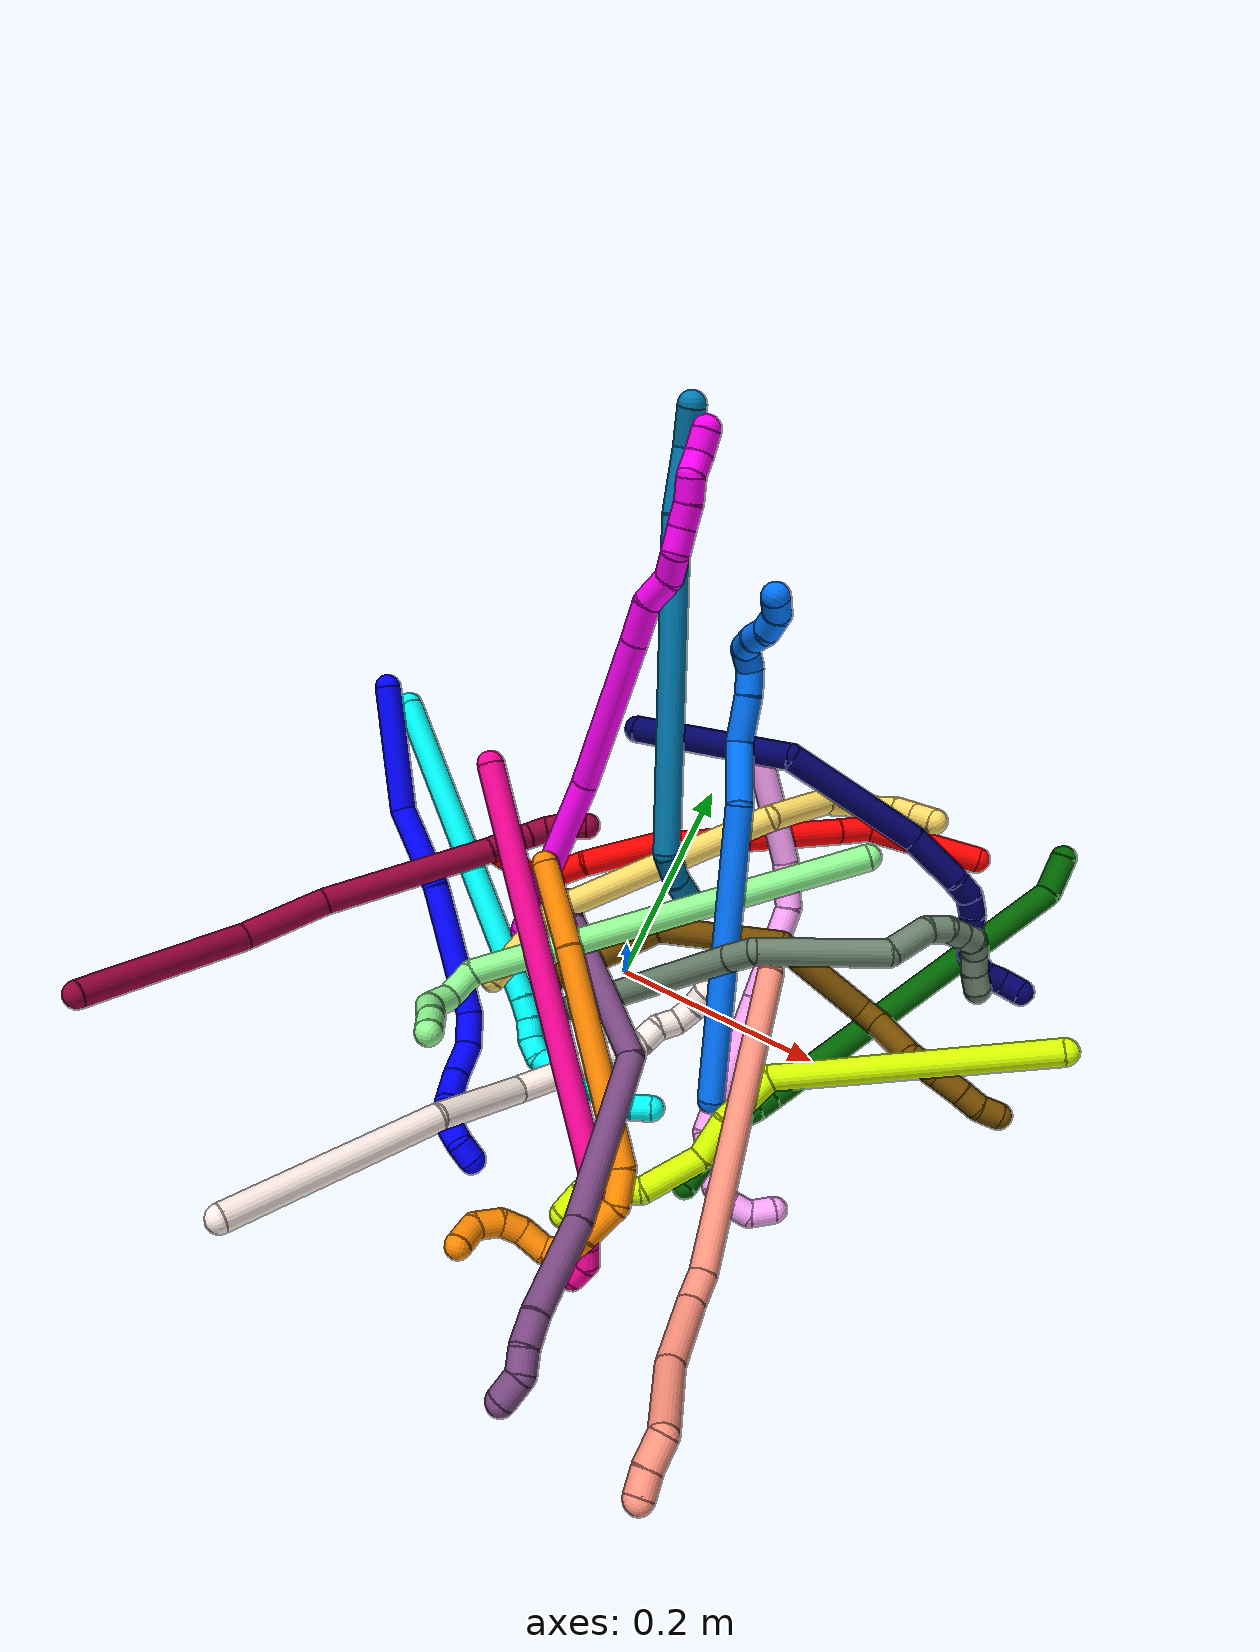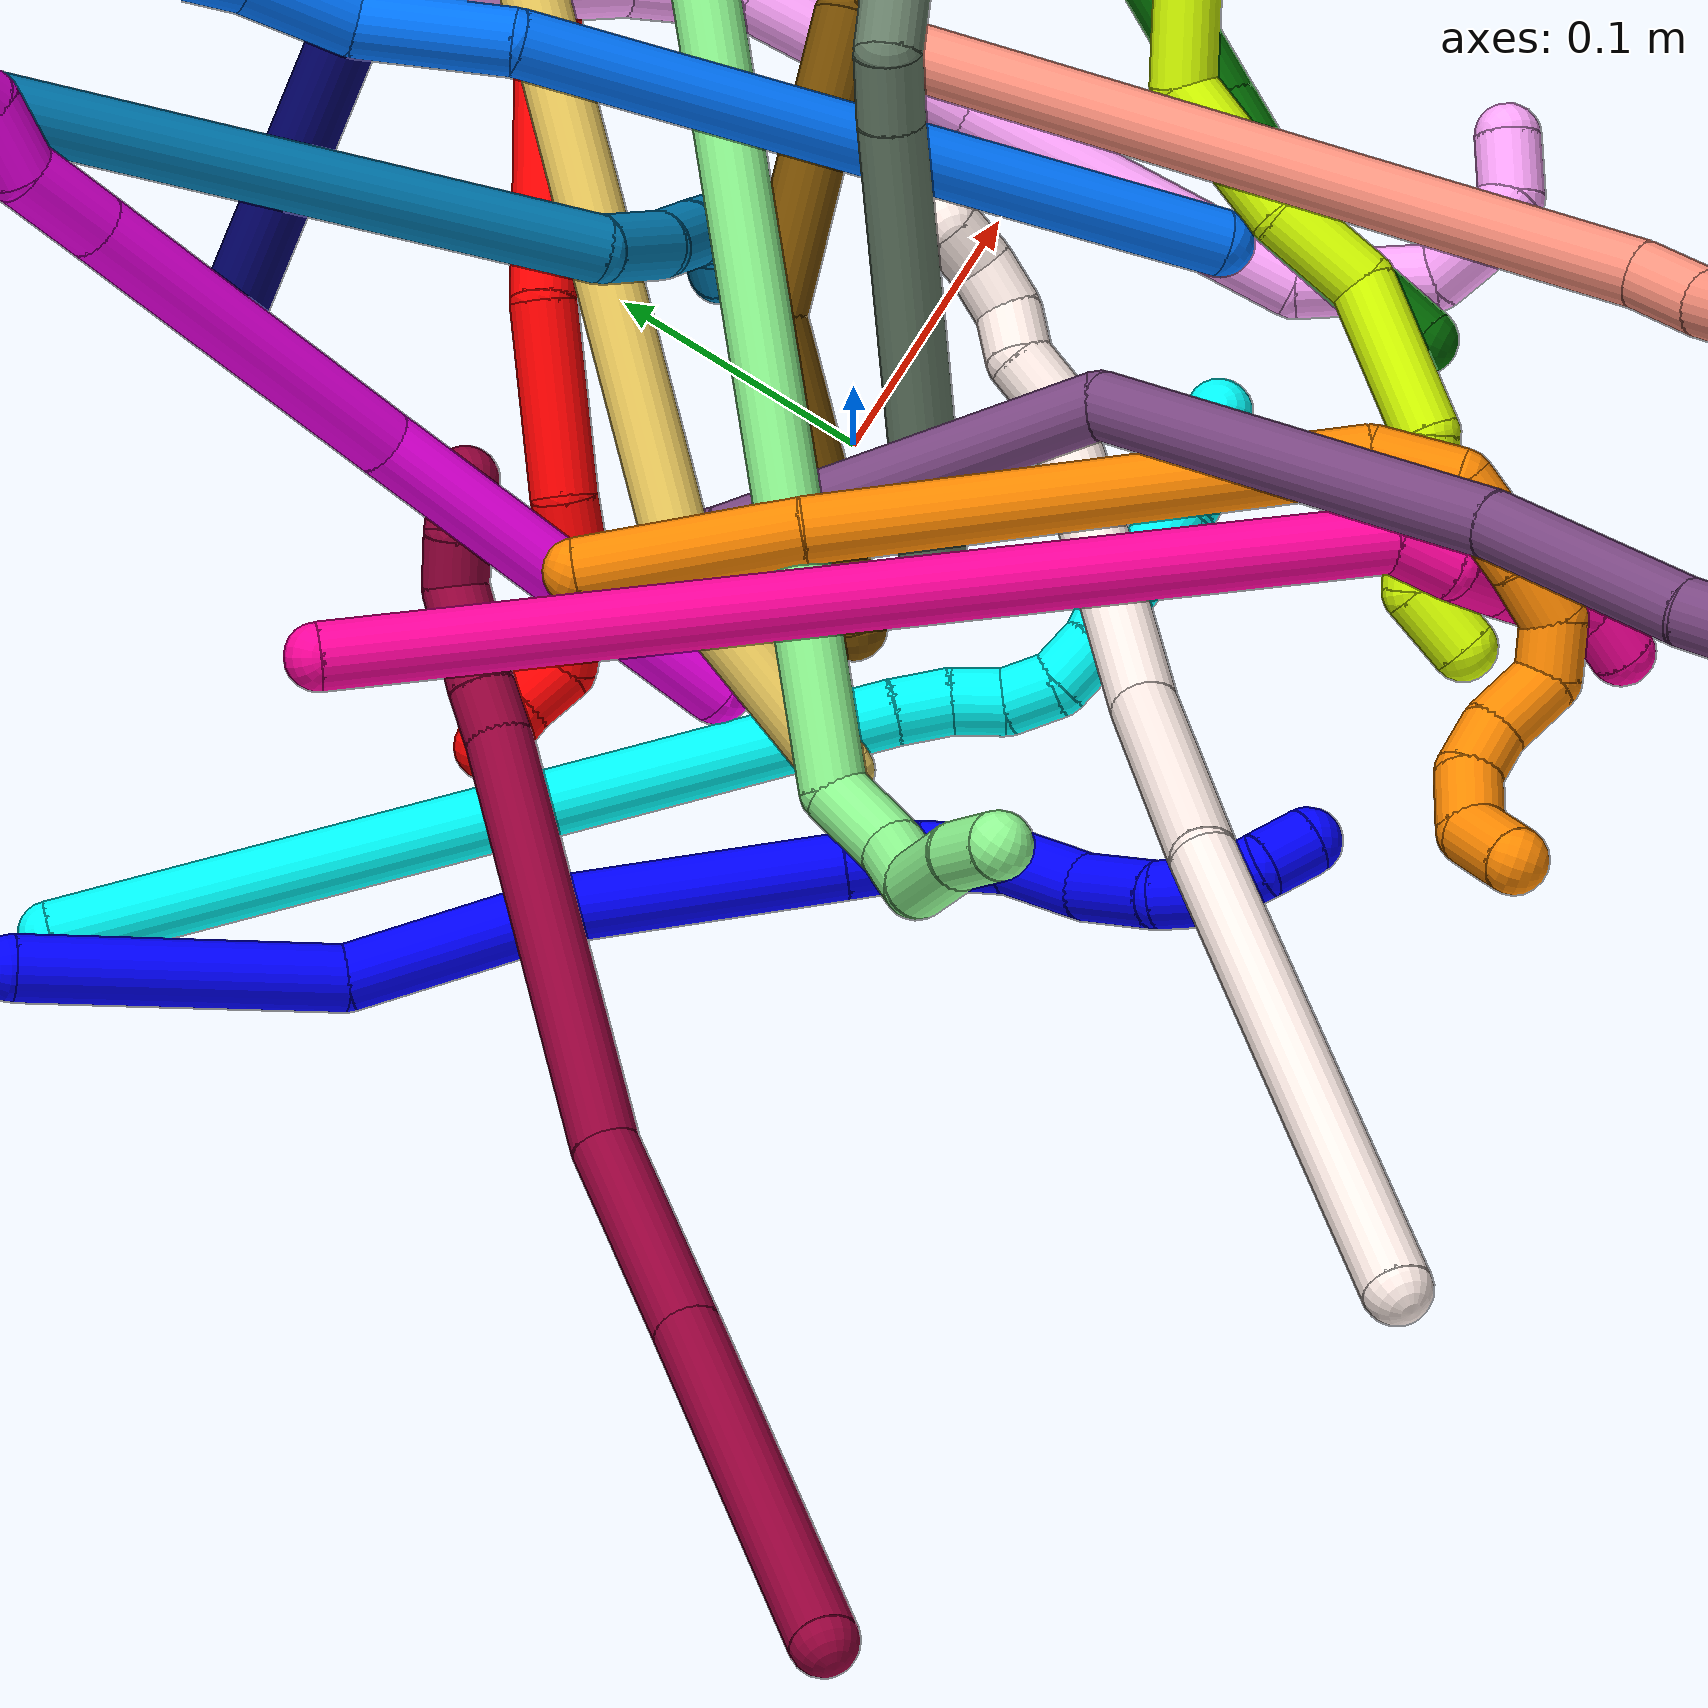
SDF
<sdf version="1.7">
 <world name="default">
  <plugin name="TubeGeneratorPlugin" filename="libtube_generator_plugin.so"/>
  <model name="photoneo_s_sensor">
   <static>1</static>
   <pose>0 0 2 1.57079 1.57079 3.14159</pose>
   <link name="link">
    <inertial><mass>0.1</mass></inertial>
    <sensor name="sensor" type="depth">
     <update_rate>30</update_rate>
     <camera>
      <horizontal_fov>1.22</horizontal_fov>
      <image><width>1920</width><height>1200</height><format>B8G8R8</format></image>
      <clip><near>0.1</near><far>4</far></clip>
      <depth_camera><output>points</output></depth_camera>
     </camera>
     <plugin name="camera_plugin" filename="libgazebo_ros_depth_camera.so">
      <baseline>0.2</baseline>
      <alwaysOn>1</alwaysOn>
      <updateRate>0.0</updateRate>
      <cameraName>camera_ir</cameraName>
      <imageTopicName>/camera/color/image_raw</imageTopicName>
      <cameraInfoTopicName>/camera/color/camera_info</cameraInfoTopicName>
      <depthImageTopicName>/camera/depth/image_raw</depthImageTopicName>
      <depthImageCameraInfoTopicName>/camera/depth/camera_info</depthImageCameraInfoTopicName>
      <pointCloudTopicName>/camera/depth/points</pointCloudTopicName>
      <frameName>fr_optical</frameName>
      <pointCloudCutoff>0.1</pointCloudCutoff>
      <pointCloudCutoffMax>2.0</pointCloudCutoffMax>
      <distortionK1>0</distortionK1>
      <distortionK2>0</distortionK2>
      <distortionK3>0</distortionK3>
      <distortionT1>0</distortionT1>
      <distortionT2>0</distortionT2>
      <CxPrime>0</CxPrime>
      <Cx>0</Cx>
      <Cy>0</Cy>
      <focalLength>0</focalLength>
      <hackBaseline>0</hackBaseline>
     </plugin>
    </sensor>
   </link>
  </model>
  <gravity>0 0 -9.8</gravity>
  <magnetic_field>6e-06 2.3e-05 -4.2e-05</magnetic_field>
  <atmosphere type="adiabatic"/>
  <physics name="default_physics" default="0" type="ode">
   <max_step_size>0.003</max_step_size>
   <real_time_factor>1</real_time_factor>
   <real_time_update_rate>1000</real_time_update_rate>
   <max_contacts>10000</max_contacts>
   <ode>
    <solver>
     <type>quick</type>
     <iters>100</iters>
     <sor>1.3</sor>
     <use_dynamic_moi_rescaling>0</use_dynamic_moi_rescaling>
    </solver>
    <constraints>
     <contact_max_correcting_vel>0</contact_max_correcting_vel>
     <contact_surface_layer>0.001</contact_surface_layer>
     <cfm>0</cfm>
     <erp>0.2</erp>
    </constraints>
   </ode>
  </physics>
  <scene><ambient>0.4 0.4 0.4 1</ambient><background>0.7 0.7 0.7 1</background><shadows>0</shadows></scene>
  <audio><device>default</device></audio>
  <spherical_coordinates>
   <surface_model>EARTH_WGS84</surface_model>
   <latitude_deg>0</latitude_deg>
   <longitude_deg>0</longitude_deg>
   <elevation>0</elevation>
   <heading_deg>0</heading_deg>
  </spherical_coordinates>
  <model name="bin">
   <static>1</static>
   <link name="bottom">
    <collision name="collision-bottom">
     <pose>0 0 -0.01 0 -0 0</pose>
     <geometry><box><size>0.8 0.6 0.02</size></box></geometry>
     <surface>
      <friction><ode><mu>100</mu><mu2>100</mu2></ode></friction>
      <contact><collide_bitmask>65535</collide_bitmask></contact>
     </surface>
    </collision>
   </link>
   <link name="west_wall">
    <collision name="collision-west_wall">
     <pose>-0.41 0 0.1 0 -0 0</pose>
     <geometry><box><size>0.02 0.6 0.2</size></box></geometry>
     <surface>
      <friction><ode><mu>100</mu><mu2>100</mu2></ode></friction>
      <contact><collide_bitmask>65535</collide_bitmask></contact>
     </surface>
    </collision>
   </link>
   <link name="east_wall">
    <collision name="collision-east_wall">
     <pose>0.41 0 0.1 0 -0 0</pose>
     <geometry><box><size>0.02 0.6 0.2</size></box></geometry>
     <surface>
      <friction><ode><mu>100</mu><mu2>100</mu2></ode></friction>
      <contact><collide_bitmask>65535</collide_bitmask></contact>
     </surface>
    </collision>
   </link>
   <link name="south_wall">
    <collision name="collision-south_wall">
     <pose>0 -0.31 0.1 0 -0 0</pose>
     <geometry><box><size>0.8 0.02 0.2</size></box></geometry>
     <surface>
      <friction><ode><mu>100</mu><mu2>100</mu2></ode></friction>
      <contact><collide_bitmask>65535</collide_bitmask></contact>
     </surface>
    </collision>
   </link>
   <link name="north_wall">
    <collision name="collision-north_wall">
     <pose>0 0.31 0.1 0 -0 0</pose>
     <geometry><box><size>0.8 0.02 0.2</size></box></geometry>
     <surface>
      <friction><ode><mu>100</mu><mu2>100</mu2></ode></friction>
      <contact><collide_bitmask>65535</collide_bitmask></contact>
     </surface>
    </collision>
   </link>
  </model>
  <model name="1">
   <static>0</static>
   <link name="1">
    <collision name="collision-cylinder-e_1_1_4">
     <pose>0.005987 -0.009109 -0.059688 2.99015 0.098828 1.15537</pose>
     <geometry><cylinder><radius>0.0125</radius><length>0.12135</length></cylinder></geometry>
     <surface>
      <friction><ode><mu>1.16</mu><mu2>1.16</mu2><slip1>0</slip1><slip2>0</slip2></ode></friction>
      <contact><ode><kp>1e+06</kp><kd>1</kd><max_vel>0</max_vel><min_depth>0.001</min_depth></ode></contact>
     </surface>
    </collision>
    <visual name="visual-cylinder-e_1_1_4">
     <pose>0.005987 -0.009109 -0.059688 2.99015 0.098828 1.15537</pose>
     <geometry><cylinder><radius>0.0125</radius><length>0.12135</length></cylinder></geometry>
     <material><ambient>0 0 1 1</ambient></material>
    </visual>
    <collision name="collision-cylinder-e_2_4_5">
     <pose>0.031057 -0.018749 -0.157565 3.12768 0.46339 3.08263</pose>
     <geometry><cylinder><radius>0.0125</radius><length>0.085391</length></cylinder></geometry>
     <surface>
      <friction><ode><mu>1.16</mu><mu2>1.16</mu2><slip1>0</slip1><slip2>0</slip2></ode></friction>
      <contact><ode><kp>1e+06</kp><kd>1</kd><max_vel>0</max_vel><min_depth>0.001</min_depth></ode></contact>
     </surface>
    </collision>
    <visual name="visual-cylinder-e_2_4_5">
     <pose>0.031057 -0.018749 -0.157565 3.12768 0.46339 3.08263</pose>
     <geometry><cylinder><radius>0.0125</radius><length>0.085391</length></cylinder></geometry>
     <material><ambient>0 0 1 1</ambient></material>
    </visual>
    <collision name="collision-cylinder-e_3_5_6">
     <pose>0.067427 -0.02543 -0.24259 3.01104 0.35079 2.43483</pose>
     <geometry><cylinder><radius>0.0125</radius><length>0.100602</length></cylinder></geometry>
     <surface>
      <friction><ode><mu>1.16</mu><mu2>1.16</mu2><slip1>0</slip1><slip2>0</slip2></ode></friction>
      <contact><ode><kp>1e+06</kp><kd>1</kd><max_vel>0</max_vel><min_depth>0.001</min_depth></ode></contact>
     </surface>
    </collision>
    <visual name="visual-cylinder-e_3_5_6">
     <pose>0.067427 -0.02543 -0.24259 3.01104 0.35079 2.43483</pose>
     <geometry><cylinder><radius>0.0125</radius><length>0.100602</length></cylinder></geometry>
     <material><ambient>0 0 1 1</ambient></material>
    </visual>
    <collision name="collision-cylinder-e_4_6_7">
     <pose>0.089559 -0.033195 -0.302743 3.02086 0.346715 2.47689</pose>
     <geometry><cylinder><radius>0.0125</radius><length>0.028527</length></cylinder></geometry>
     <surface>
      <friction><ode><mu>1.16</mu><mu2>1.16</mu2><slip1>0</slip1><slip2>0</slip2></ode></friction>
      <contact><ode><kp>1e+06</kp><kd>1</kd><max_vel>0</max_vel><min_depth>0.001</min_depth></ode></contact>
     </surface>
    </collision>
    <visual name="visual-cylinder-e_4_6_7">
     <pose>0.089559 -0.033195 -0.302743 3.02086 0.346715 2.47689</pose>
     <geometry><cylinder><radius>0.0125</radius><length>0.028527</length></cylinder></geometry>
     <material><ambient>0 0 1 1</ambient></material>
    </visual>
    <collision name="collision-cylinder-e_5_7_8">
     <pose>0.10069 -0.042116 -0.329174 2.63336 0.396446 1.31654</pose>
     <geometry><cylinder><radius>0.0125</radius><length>0.032548</length></cylinder></geometry>
     <surface>
      <friction><ode><mu>1.16</mu><mu2>1.16</mu2><slip1>0</slip1><slip2>0</slip2></ode></friction>
      <contact><ode><kp>1e+06</kp><kd>1</kd><max_vel>0</max_vel><min_depth>0.001</min_depth></ode></contact>
     </surface>
    </collision>
    <visual name="visual-cylinder-e_5_7_8">
     <pose>0.10069 -0.042116 -0.329174 2.63336 0.396446 1.31654</pose>
     <geometry><cylinder><radius>0.0125</radius><length>0.032548</length></cylinder></geometry>
     <material><ambient>0 0 1 1</ambient></material>
    </visual>
    <collision name="collision-cylinder-e_6_8_9">
     <pose>0.114398 -0.062611 -0.351257 2.16796 0.435597 0.792045</pose>
     <geometry><cylinder><radius>0.0125</radius><length>0.035186</length></cylinder></geometry>
     <surface>
      <friction><ode><mu>1.16</mu><mu2>1.16</mu2><slip1>0</slip1><slip2>0</slip2></ode></friction>
      <contact><ode><kp>1e+06</kp><kd>1</kd><max_vel>0</max_vel><min_depth>0.001</min_depth></ode></contact>
     </surface>
    </collision>
    <visual name="visual-cylinder-e_6_8_9">
     <pose>0.114398 -0.062611 -0.351257 2.16796 0.435597 0.792045</pose>
     <geometry><cylinder><radius>0.0125</radius><length>0.035186</length></cylinder></geometry>
     <material><ambient>0 0 1 1</ambient></material>
    </visual>
    <collision name="collision-cylinder-e_7_9_10">
     <pose>0.133039 -0.08773 -0.366911 2.08155 0.687011 1.09613</pose>
     <geometry><cylinder><radius>0.0125</radius><length>0.035373</length></cylinder></geometry>
     <surface>
      <friction><ode><mu>1.16</mu><mu2>1.16</mu2><slip1>0</slip1><slip2>0</slip2></ode></friction>
      <contact><ode><kp>1e+06</kp><kd>1</kd><max_vel>0</max_vel><min_depth>0.001</min_depth></ode></contact>
     </surface>
    </collision>
    <visual name="visual-cylinder-e_7_9_10">
     <pose>0.133039 -0.08773 -0.366911 2.08155 0.687011 1.09613</pose>
     <geometry><cylinder><radius>0.0125</radius><length>0.035373</length></cylinder></geometry>
     <material><ambient>0 0 1 1</ambient></material>
    </visual>
    <collision name="collision-cylinder-e_8_10_11">
     <pose>0.150132 -0.104202 -0.380997 2.5912 0.594846 1.6528</pose>
     <geometry><cylinder><radius>0.0125</radius><length>0.020972</length></cylinder></geometry>
     <surface>
      <friction><ode><mu>1.16</mu><mu2>1.16</mu2><slip1>0</slip1><slip2>0</slip2></ode></friction>
      <contact><ode><kp>1e+06</kp><kd>1</kd><max_vel>0</max_vel><min_depth>0.001</min_depth></ode></contact>
     </surface>
    </collision>
    <visual name="visual-cylinder-e_8_10_11">
     <pose>0.150132 -0.104202 -0.380997 2.5912 0.594846 1.6528</pose>
     <geometry><cylinder><radius>0.0125</radius><length>0.020972</length></cylinder></geometry>
     <material><ambient>0 0 1 1</ambient></material>
    </visual>
    <collision name="collision-cylinder-e_9_11_12">
     <pose>0.162707 -0.108713 -0.395833 -3.13736 0.73345 -3.13057</pose>
     <geometry><cylinder><radius>0.0125</radius><length>0.020014</length></cylinder></geometry>
     <surface>
      <friction><ode><mu>1.16</mu><mu2>1.16</mu2><slip1>0</slip1><slip2>0</slip2></ode></friction>
      <contact><ode><kp>1e+06</kp><kd>1</kd><max_vel>0</max_vel><min_depth>0.001</min_depth></ode></contact>
     </surface>
    </collision>
    <visual name="visual-cylinder-e_9_11_12">
     <pose>0.162707 -0.108713 -0.395833 -3.13736 0.73345 -3.13057</pose>
     <geometry><cylinder><radius>0.0125</radius><length>0.020014</length></cylinder></geometry>
     <material><ambient>0 0 1 1</ambient></material>
    </visual>
    <collision name="collision-cylinder-e_10_12_2">
     <pose>0.172572 -0.105755 -0.412311 -2.82862 0.321483 -1.59806</pose>
     <geometry><cylinder><radius>0.0125</radius><length>0.020037</length></cylinder></geometry>
     <surface>
      <friction><ode><mu>1.16</mu><mu2>1.16</mu2><slip1>0</slip1><slip2>0</slip2></ode></friction>
      <contact><ode><kp>1e+06</kp><kd>1</kd><max_vel>0</max_vel><min_depth>0.001</min_depth></ode></contact>
     </surface>
    </collision>
    <visual name="visual-cylinder-e_10_12_2">
     <pose>0.172572 -0.105755 -0.412311 -2.82862 0.321483 -1.59806</pose>
     <geometry><cylinder><radius>0.0125</radius><length>0.020037</length></cylinder></geometry>
     <material><ambient>0 0 1 1</ambient></material>
    </visual>
    <collision name="collision-sphere-2">
     <pose>0.175737 -0.102828 -0.421354 0 -0 0</pose>
     <geometry><sphere><radius>0.0125</radius></sphere></geometry>
     <surface>
      <friction><ode><mu>1.16</mu><mu2>1.16</mu2><slip1>0</slip1><slip2>0</slip2></ode></friction>
      <contact><ode><kp>1e+06</kp><kd>1</kd><max_vel>0</max_vel><min_depth>0.001</min_depth></ode></contact>
     </surface>
    </collision>
    <visual name="visual-sphere-2">
     <pose>0.175737 -0.102828 -0.421354 0 -0 0</pose>
     <geometry><sphere><radius>0.0125</radius></sphere></geometry>
     <material><ambient>0 0 1 1</ambient></material>
    </visual>
    <collision name="collision-sphere-12">
     <pose>0.169406 -0.108681 -0.403267 0 -0 0</pose>
     <geometry><sphere><radius>0.0125</radius></sphere></geometry>
     <surface>
      <friction><ode><mu>1.16</mu><mu2>1.16</mu2><slip1>0</slip1><slip2>0</slip2></ode></friction>
      <contact><ode><kp>1e+06</kp><kd>1</kd><max_vel>0</max_vel><min_depth>0.001</min_depth></ode></contact>
     </surface>
    </collision>
    <visual name="visual-sphere-12">
     <pose>0.169406 -0.108681 -0.403267 0 -0 0</pose>
     <geometry><sphere><radius>0.0125</radius></sphere></geometry>
     <material><ambient>0 0 1 1</ambient></material>
    </visual>
    <collision name="collision-sphere-11">
     <pose>0.156008 -0.108744 -0.3884 0 -0 0</pose>
     <geometry><sphere><radius>0.0125</radius></sphere></geometry>
     <surface>
      <friction><ode><mu>1.16</mu><mu2>1.16</mu2><slip1>0</slip1><slip2>0</slip2></ode></friction>
      <contact><ode><kp>1e+06</kp><kd>1</kd><max_vel>0</max_vel><min_depth>0.001</min_depth></ode></contact>
     </surface>
    </collision>
    <visual name="visual-sphere-11">
     <pose>0.156008 -0.108744 -0.3884 0 -0 0</pose>
     <geometry><sphere><radius>0.0125</radius></sphere></geometry>
     <material><ambient>0 0 1 1</ambient></material>
    </visual>
    <collision name="collision-sphere-10">
     <pose>0.144256 -0.09966 -0.373595 0 -0 0</pose>
     <geometry><sphere><radius>0.0125</radius></sphere></geometry>
     <surface>
      <friction><ode><mu>1.16</mu><mu2>1.16</mu2><slip1>0</slip1><slip2>0</slip2></ode></friction>
      <contact><ode><kp>1e+06</kp><kd>1</kd><max_vel>0</max_vel><min_depth>0.001</min_depth></ode></contact>
     </surface>
    </collision>
    <visual name="visual-sphere-10">
     <pose>0.144256 -0.09966 -0.373595 0 -0 0</pose>
     <geometry><sphere><radius>0.0125</radius></sphere></geometry>
     <material><ambient>0 0 1 1</ambient></material>
    </visual>
    <collision name="collision-sphere-9">
     <pose>0.121821 -0.075801 -0.360226 0 -0 0</pose>
     <geometry><sphere><radius>0.0125</radius></sphere></geometry>
     <surface>
      <friction><ode><mu>1.16</mu><mu2>1.16</mu2><slip1>0</slip1><slip2>0</slip2></ode></friction>
      <contact><ode><kp>1e+06</kp><kd>1</kd><max_vel>0</max_vel><min_depth>0.001</min_depth></ode></contact>
     </surface>
    </collision>
    <visual name="visual-sphere-9">
     <pose>0.121821 -0.075801 -0.360226 0 -0 0</pose>
     <geometry><sphere><radius>0.0125</radius></sphere></geometry>
     <material><ambient>0 0 1 1</ambient></material>
    </visual>
    <collision name="collision-sphere-4">
     <pose>0.011973 -0.018218 -0.119376 0 -0 0</pose>
     <geometry><sphere><radius>0.0125</radius></sphere></geometry>
     <surface>
      <friction><ode><mu>1.16</mu><mu2>1.16</mu2><slip1>0</slip1><slip2>0</slip2></ode></friction>
      <contact><ode><kp>1e+06</kp><kd>1</kd><max_vel>0</max_vel><min_depth>0.001</min_depth></ode></contact>
     </surface>
    </collision>
    <visual name="visual-sphere-4">
     <pose>0.011973 -0.018218 -0.119376 0 -0 0</pose>
     <geometry><sphere><radius>0.0125</radius></sphere></geometry>
     <material><ambient>0 0 1 1</ambient></material>
    </visual>
    <collision name="collision-sphere-1">
     <geometry><sphere><radius>0.0125</radius></sphere></geometry>
     <surface>
      <friction><ode><mu>1.16</mu><mu2>1.16</mu2><slip1>0</slip1><slip2>0</slip2></ode></friction>
      <contact><ode><kp>1e+06</kp><kd>1</kd><max_vel>0</max_vel><min_depth>0.001</min_depth></ode></contact>
     </surface>
    </collision>
    <visual name="visual-sphere-1">
     <geometry><sphere><radius>0.0125</radius></sphere></geometry>
     <material><ambient>0 0 1 1</ambient></material>
    </visual>
    <collision name="collision-sphere-8">
     <pose>0.106974 -0.049421 -0.342288 0 -0 0</pose>
     <geometry><sphere><radius>0.0125</radius></sphere></geometry>
     <surface>
      <friction><ode><mu>1.16</mu><mu2>1.16</mu2><slip1>0</slip1><slip2>0</slip2></ode></friction>
      <contact><ode><kp>1e+06</kp><kd>1</kd><max_vel>0</max_vel><min_depth>0.001</min_depth></ode></contact>
     </surface>
    </collision>
    <visual name="visual-sphere-8">
     <pose>0.106974 -0.049421 -0.342288 0 -0 0</pose>
     <geometry><sphere><radius>0.0125</radius></sphere></geometry>
     <material><ambient>0 0 1 1</ambient></material>
    </visual>
    <collision name="collision-sphere-5">
     <pose>0.050142 -0.019281 -0.195754 0 -0 0</pose>
     <geometry><sphere><radius>0.0125</radius></sphere></geometry>
     <surface>
      <friction><ode><mu>1.16</mu><mu2>1.16</mu2><slip1>0</slip1><slip2>0</slip2></ode></friction>
      <contact><ode><kp>1e+06</kp><kd>1</kd><max_vel>0</max_vel><min_depth>0.001</min_depth></ode></contact>
     </surface>
    </collision>
    <visual name="visual-sphere-5">
     <pose>0.050142 -0.019281 -0.195754 0 -0 0</pose>
     <geometry><sphere><radius>0.0125</radius></sphere></geometry>
     <material><ambient>0 0 1 1</ambient></material>
    </visual>
    <collision name="collision-sphere-6">
     <pose>0.084712 -0.03158 -0.289426 0 -0 0</pose>
     <geometry><sphere><radius>0.0125</radius></sphere></geometry>
     <surface>
      <friction><ode><mu>1.16</mu><mu2>1.16</mu2><slip1>0</slip1><slip2>0</slip2></ode></friction>
      <contact><ode><kp>1e+06</kp><kd>1</kd><max_vel>0</max_vel><min_depth>0.001</min_depth></ode></contact>
     </surface>
    </collision>
    <visual name="visual-sphere-6">
     <pose>0.084712 -0.03158 -0.289426 0 -0 0</pose>
     <geometry><sphere><radius>0.0125</radius></sphere></geometry>
     <material><ambient>0 0 1 1</ambient></material>
    </visual>
    <collision name="collision-sphere-7">
     <pose>0.094406 -0.034811 -0.31606 0 -0 0</pose>
     <geometry><sphere><radius>0.0125</radius></sphere></geometry>
     <surface>
      <friction><ode><mu>1.16</mu><mu2>1.16</mu2><slip1>0</slip1><slip2>0</slip2></ode></friction>
      <contact><ode><kp>1e+06</kp><kd>1</kd><max_vel>0</max_vel><min_depth>0.001</min_depth></ode></contact>
     </surface>
    </collision>
    <visual name="visual-sphere-7">
     <pose>0.094406 -0.034811 -0.31606 0 -0 0</pose>
     <geometry><sphere><radius>0.0125</radius></sphere></geometry>
     <material><ambient>0 0 1 1</ambient></material>
    </visual>
    <inertial>
     <pose>0.069176 -0.038738 -0.22793 0 -0 0</pose>
     <mass>0.5</mass>
     <inertia>
      <ixx>0.000174</ixx>
      <ixy>0</ixy>
      <ixz>0</ixz>
      <iyy>0.000272</iyy>
      <iyz>0</iyz>
      <izz>-6.9e-05</izz>
     </inertia>
    </inertial>
   </link>
   <pose>-0.331421 0.148685 0.038222 -0.914349 -0.91322 0.096742</pose>
  </model>
  <model name="2">
   <static>0</static>
   <link name="2">
    <collision name="collision-cylinder-e_1_1_4">
     <pose>-0.016898 0.004487 -0.051456 -3.05461 -0.316178 2.6086</pose>
     <geometry><cylinder><radius>0.0125</radius><length>0.10869</length></cylinder></geometry>
     <surface>
      <friction><ode><mu>1.16</mu><mu2>1.16</mu2><slip1>0</slip1><slip2>0</slip2></ode></friction>
      <contact><ode><kp>1e+06</kp><kd>1</kd><max_vel>0</max_vel><min_depth>0.001</min_depth></ode></contact>
     </surface>
    </collision>
    <visual name="visual-cylinder-e_1_1_4">
     <pose>-0.016898 0.004487 -0.051456 -3.05461 -0.316178 2.6086</pose>
     <geometry><cylinder><radius>0.0125</radius><length>0.10869</length></cylinder></geometry>
     <material><ambient>1 0 0 1</ambient></material>
    </visual>
    <collision name="collision-cylinder-e_2_4_5">
     <pose>-0.041556 0.003245 -0.115933 2.72707 -0.499398 -1.76252</pose>
     <geometry><cylinder><radius>0.0125</radius><length>0.032411</length></cylinder></geometry>
     <surface>
      <friction><ode><mu>1.16</mu><mu2>1.16</mu2><slip1>0</slip1><slip2>0</slip2></ode></friction>
      <contact><ode><kp>1e+06</kp><kd>1</kd><max_vel>0</max_vel><min_depth>0.001</min_depth></ode></contact>
     </surface>
    </collision>
    <visual name="visual-cylinder-e_2_4_5">
     <pose>-0.041556 0.003245 -0.115933 2.72707 -0.499398 -1.76252</pose>
     <geometry><cylinder><radius>0.0125</radius><length>0.032411</length></cylinder></geometry>
     <material><ambient>1 0 0 1</ambient></material>
    </visual>
    <collision name="collision-cylinder-e_3_5_6">
     <pose>-0.084269 -0.027981 -0.191213 2.75291 -0.47914 -1.78506</pose>
     <geometry><cylinder><radius>0.0125</radius><length>0.151628</length></cylinder></geometry>
     <surface>
      <friction><ode><mu>1.16</mu><mu2>1.16</mu2><slip1>0</slip1><slip2>0</slip2></ode></friction>
      <contact><ode><kp>1e+06</kp><kd>1</kd><max_vel>0</max_vel><min_depth>0.001</min_depth></ode></contact>
     </surface>
    </collision>
    <visual name="visual-cylinder-e_3_5_6">
     <pose>-0.084269 -0.027981 -0.191213 2.75291 -0.47914 -1.78506</pose>
     <geometry><cylinder><radius>0.0125</radius><length>0.151628</length></cylinder></geometry>
     <material><ambient>1 0 0 1</ambient></material>
    </visual>
    <collision name="collision-cylinder-e_4_6_7">
     <pose>-0.126533 -0.058518 -0.266192 2.76421 -0.490837 -1.83879</pose>
     <geometry><cylinder><radius>0.0125</radius><length>0.03103</length></cylinder></geometry>
     <surface>
      <friction><ode><mu>1.16</mu><mu2>1.16</mu2><slip1>0</slip1><slip2>0</slip2></ode></friction>
      <contact><ode><kp>1e+06</kp><kd>1</kd><max_vel>0</max_vel><min_depth>0.001</min_depth></ode></contact>
     </surface>
    </collision>
    <visual name="visual-cylinder-e_4_6_7">
     <pose>-0.126533 -0.058518 -0.266192 2.76421 -0.490837 -1.83879</pose>
     <geometry><cylinder><radius>0.0125</radius><length>0.03103</length></cylinder></geometry>
     <material><ambient>1 0 0 1</ambient></material>
    </visual>
    <collision name="collision-cylinder-e_5_7_8">
     <pose>-0.140037 -0.078663 -0.310889 2.70036 -0.173305 -0.739108</pose>
     <geometry><cylinder><radius>0.0125</radius><length>0.071803</length></cylinder></geometry>
     <surface>
      <friction><ode><mu>1.16</mu><mu2>1.16</mu2><slip1>0</slip1><slip2>0</slip2></ode></friction>
      <contact><ode><kp>1e+06</kp><kd>1</kd><max_vel>0</max_vel><min_depth>0.001</min_depth></ode></contact>
     </surface>
    </collision>
    <visual name="visual-cylinder-e_5_7_8">
     <pose>-0.140037 -0.078663 -0.310889 2.70036 -0.173305 -0.739108</pose>
     <geometry><cylinder><radius>0.0125</radius><length>0.071803</length></cylinder></geometry>
     <material><ambient>1 0 0 1</ambient></material>
    </visual>
    <collision name="collision-cylinder-e_6_8_9">
     <pose>-0.145211 -0.098876 -0.353478 2.69275 0.086144 0.373226</pose>
     <geometry><cylinder><radius>0.0125</radius><length>0.023645</length></cylinder></geometry>
     <surface>
      <friction><ode><mu>1.16</mu><mu2>1.16</mu2><slip1>0</slip1><slip2>0</slip2></ode></friction>
      <contact><ode><kp>1e+06</kp><kd>1</kd><max_vel>0</max_vel><min_depth>0.001</min_depth></ode></contact>
     </surface>
    </collision>
    <visual name="visual-cylinder-e_6_8_9">
     <pose>-0.145211 -0.098876 -0.353478 2.69275 0.086144 0.373226</pose>
     <geometry><cylinder><radius>0.0125</radius><length>0.023645</length></cylinder></geometry>
     <material><ambient>1 0 0 1</ambient></material>
    </visual>
    <collision name="collision-cylinder-e_7_9_10">
     <pose>-0.143347 -0.106333 -0.373781 2.90402 0.08472 0.682484</pose>
     <geometry><cylinder><radius>0.0125</radius><length>0.020014</length></cylinder></geometry>
     <surface>
      <friction><ode><mu>1.16</mu><mu2>1.16</mu2><slip1>0</slip1><slip2>0</slip2></ode></friction>
      <contact><ode><kp>1e+06</kp><kd>1</kd><max_vel>0</max_vel><min_depth>0.001</min_depth></ode></contact>
     </surface>
    </collision>
    <visual name="visual-cylinder-e_7_9_10">
     <pose>-0.143347 -0.106333 -0.373781 2.90402 0.08472 0.682484</pose>
     <geometry><cylinder><radius>0.0125</radius><length>0.020014</length></cylinder></geometry>
     <material><ambient>1 0 0 1</ambient></material>
    </visual>
    <collision name="collision-cylinder-e_8_10_11">
     <pose>-0.142232 -0.109844 -0.393773 3.0291 0.025864 0.451533</pose>
     <geometry><cylinder><radius>0.0125</radius><length>0.020741</length></cylinder></geometry>
     <surface>
      <friction><ode><mu>1.16</mu><mu2>1.16</mu2><slip1>0</slip1><slip2>0</slip2></ode></friction>
      <contact><ode><kp>1e+06</kp><kd>1</kd><max_vel>0</max_vel><min_depth>0.001</min_depth></ode></contact>
     </surface>
    </collision>
    <visual name="visual-cylinder-e_8_10_11">
     <pose>-0.142232 -0.109844 -0.393773 3.0291 0.025864 0.451533</pose>
     <geometry><cylinder><radius>0.0125</radius><length>0.020741</length></cylinder></geometry>
     <material><ambient>1 0 0 1</ambient></material>
    </visual>
    <collision name="collision-cylinder-e_9_11_12">
     <pose>-0.145733 -0.106159 -0.411969 -2.59086 -0.38634 1.2111</pose>
     <geometry><cylinder><radius>0.0125</radius><length>0.020004</length></cylinder></geometry>
     <surface>
      <friction><ode><mu>1.16</mu><mu2>1.16</mu2><slip1>0</slip1><slip2>0</slip2></ode></friction>
      <contact><ode><kp>1e+06</kp><kd>1</kd><max_vel>0</max_vel><min_depth>0.001</min_depth></ode></contact>
     </surface>
    </collision>
    <visual name="visual-cylinder-e_9_11_12">
     <pose>-0.145733 -0.106159 -0.411969 -2.59086 -0.38634 1.2111</pose>
     <geometry><cylinder><radius>0.0125</radius><length>0.020004</length></cylinder></geometry>
     <material><ambient>1 0 0 1</ambient></material>
    </visual>
    <collision name="collision-cylinder-e_10_12_2">
     <pose>-0.153188 -0.09811 -0.428611 -2.79074 -0.376875 1.64387</pose>
     <geometry><cylinder><radius>0.0125</radius><length>0.020035</length></cylinder></geometry>
     <surface>
      <friction><ode><mu>1.16</mu><mu2>1.16</mu2><slip1>0</slip1><slip2>0</slip2></ode></friction>
      <contact><ode><kp>1e+06</kp><kd>1</kd><max_vel>0</max_vel><min_depth>0.001</min_depth></ode></contact>
     </surface>
    </collision>
    <visual name="visual-cylinder-e_10_12_2">
     <pose>-0.153188 -0.09811 -0.428611 -2.79074 -0.376875 1.64387</pose>
     <geometry><cylinder><radius>0.0125</radius><length>0.020035</length></cylinder></geometry>
     <material><ambient>1 0 0 1</ambient></material>
    </visual>
    <collision name="collision-sphere-2">
     <pose>-0.156875 -0.094908 -0.437358 0 -0 0</pose>
     <geometry><sphere><radius>0.0125</radius></sphere></geometry>
     <surface>
      <friction><ode><mu>1.16</mu><mu2>1.16</mu2><slip1>0</slip1><slip2>0</slip2></ode></friction>
      <contact><ode><kp>1e+06</kp><kd>1</kd><max_vel>0</max_vel><min_depth>0.001</min_depth></ode></contact>
     </surface>
    </collision>
    <visual name="visual-sphere-2">
     <pose>-0.156875 -0.094908 -0.437358 0 -0 0</pose>
     <geometry><sphere><radius>0.0125</radius></sphere></geometry>
     <material><ambient>1 0 0 1</ambient></material>
    </visual>
    <collision name="collision-sphere-12">
     <pose>-0.149501 -0.101311 -0.419864 0 -0 0</pose>
     <geometry><sphere><radius>0.0125</radius></sphere></geometry>
     <surface>
      <friction><ode><mu>1.16</mu><mu2>1.16</mu2><slip1>0</slip1><slip2>0</slip2></ode></friction>
      <contact><ode><kp>1e+06</kp><kd>1</kd><max_vel>0</max_vel><min_depth>0.001</min_depth></ode></contact>
     </surface>
    </collision>
    <visual name="visual-sphere-12">
     <pose>-0.149501 -0.101311 -0.419864 0 -0 0</pose>
     <geometry><sphere><radius>0.0125</radius></sphere></geometry>
     <material><ambient>1 0 0 1</ambient></material>
    </visual>
    <collision name="collision-sphere-11">
     <pose>-0.141964 -0.111008 -0.404074 0 -0 0</pose>
     <geometry><sphere><radius>0.0125</radius></sphere></geometry>
     <surface>
      <friction><ode><mu>1.16</mu><mu2>1.16</mu2><slip1>0</slip1><slip2>0</slip2></ode></friction>
      <contact><ode><kp>1e+06</kp><kd>1</kd><max_vel>0</max_vel><min_depth>0.001</min_depth></ode></contact>
     </surface>
    </collision>
    <visual name="visual-sphere-11">
     <pose>-0.141964 -0.111008 -0.404074 0 -0 0</pose>
     <geometry><sphere><radius>0.0125</radius></sphere></geometry>
     <material><ambient>1 0 0 1</ambient></material>
    </visual>
    <collision name="collision-sphere-10">
     <pose>-0.1425 -0.10868 -0.383472 0 -0 0</pose>
     <geometry><sphere><radius>0.0125</radius></sphere></geometry>
     <surface>
      <friction><ode><mu>1.16</mu><mu2>1.16</mu2><slip1>0</slip1><slip2>0</slip2></ode></friction>
      <contact><ode><kp>1e+06</kp><kd>1</kd><max_vel>0</max_vel><min_depth>0.001</min_depth></ode></contact>
     </surface>
    </collision>
    <visual name="visual-sphere-10">
     <pose>-0.1425 -0.10868 -0.383472 0 -0 0</pose>
     <geometry><sphere><radius>0.0125</radius></sphere></geometry>
     <material><ambient>1 0 0 1</ambient></material>
    </visual>
    <collision name="collision-sphere-9">
     <pose>-0.144194 -0.103987 -0.364089 0 -0 0</pose>
     <geometry><sphere><radius>0.0125</radius></sphere></geometry>
     <surface>
      <friction><ode><mu>1.16</mu><mu2>1.16</mu2><slip1>0</slip1><slip2>0</slip2></ode></friction>
      <contact><ode><kp>1e+06</kp><kd>1</kd><max_vel>0</max_vel><min_depth>0.001</min_depth></ode></contact>
     </surface>
    </collision>
    <visual name="visual-sphere-9">
     <pose>-0.144194 -0.103987 -0.364089 0 -0 0</pose>
     <geometry><sphere><radius>0.0125</radius></sphere></geometry>
     <material><ambient>1 0 0 1</ambient></material>
    </visual>
    <collision name="collision-sphere-4">
     <pose>-0.033796 0.008974 -0.102912 0 -0 0</pose>
     <geometry><sphere><radius>0.0125</radius></sphere></geometry>
     <surface>
      <friction><ode><mu>1.16</mu><mu2>1.16</mu2><slip1>0</slip1><slip2>0</slip2></ode></friction>
      <contact><ode><kp>1e+06</kp><kd>1</kd><max_vel>0</max_vel><min_depth>0.001</min_depth></ode></contact>
     </surface>
    </collision>
    <visual name="visual-sphere-4">
     <pose>-0.033796 0.008974 -0.102912 0 -0 0</pose>
     <geometry><sphere><radius>0.0125</radius></sphere></geometry>
     <material><ambient>1 0 0 1</ambient></material>
    </visual>
    <collision name="collision-sphere-1">
     <geometry><sphere><radius>0.0125</radius></sphere></geometry>
     <surface>
      <friction><ode><mu>1.16</mu><mu2>1.16</mu2><slip1>0</slip1><slip2>0</slip2></ode></friction>
      <contact><ode><kp>1e+06</kp><kd>1</kd><max_vel>0</max_vel><min_depth>0.001</min_depth></ode></contact>
     </surface>
    </collision>
    <visual name="visual-sphere-1">
     <geometry><sphere><radius>0.0125</radius></sphere></geometry>
     <material><ambient>1 0 0 1</ambient></material>
    </visual>
    <collision name="collision-sphere-8">
     <pose>-0.146228 -0.093765 -0.342866 0 -0 0</pose>
     <geometry><sphere><radius>0.0125</radius></sphere></geometry>
     <surface>
      <friction><ode><mu>1.16</mu><mu2>1.16</mu2><slip1>0</slip1><slip2>0</slip2></ode></friction>
      <contact><ode><kp>1e+06</kp><kd>1</kd><max_vel>0</max_vel><min_depth>0.001</min_depth></ode></contact>
     </surface>
    </collision>
    <visual name="visual-sphere-8">
     <pose>-0.146228 -0.093765 -0.342866 0 -0 0</pose>
     <geometry><sphere><radius>0.0125</radius></sphere></geometry>
     <material><ambient>1 0 0 1</ambient></material>
    </visual>
    <collision name="collision-sphere-5">
     <pose>-0.049317 -0.002485 -0.128954 0 -0 0</pose>
     <geometry><sphere><radius>0.0125</radius></sphere></geometry>
     <surface>
      <friction><ode><mu>1.16</mu><mu2>1.16</mu2><slip1>0</slip1><slip2>0</slip2></ode></friction>
      <contact><ode><kp>1e+06</kp><kd>1</kd><max_vel>0</max_vel><min_depth>0.001</min_depth></ode></contact>
     </surface>
    </collision>
    <visual name="visual-sphere-5">
     <pose>-0.049317 -0.002485 -0.128954 0 -0 0</pose>
     <geometry><sphere><radius>0.0125</radius></sphere></geometry>
     <material><ambient>1 0 0 1</ambient></material>
    </visual>
    <collision name="collision-sphere-6">
     <pose>-0.11922 -0.053476 -0.253472 0 -0 0</pose>
     <geometry><sphere><radius>0.0125</radius></sphere></geometry>
     <surface>
      <friction><ode><mu>1.16</mu><mu2>1.16</mu2><slip1>0</slip1><slip2>0</slip2></ode></friction>
      <contact><ode><kp>1e+06</kp><kd>1</kd><max_vel>0</max_vel><min_depth>0.001</min_depth></ode></contact>
     </surface>
    </collision>
    <visual name="visual-sphere-6">
     <pose>-0.11922 -0.053476 -0.253472 0 -0 0</pose>
     <geometry><sphere><radius>0.0125</radius></sphere></geometry>
     <material><ambient>1 0 0 1</ambient></material>
    </visual>
    <collision name="collision-sphere-7">
     <pose>-0.133847 -0.063561 -0.278912 0 -0 0</pose>
     <geometry><sphere><radius>0.0125</radius></sphere></geometry>
     <surface>
      <friction><ode><mu>1.16</mu><mu2>1.16</mu2><slip1>0</slip1><slip2>0</slip2></ode></friction>
      <contact><ode><kp>1e+06</kp><kd>1</kd><max_vel>0</max_vel><min_depth>0.001</min_depth></ode></contact>
     </surface>
    </collision>
    <visual name="visual-sphere-7">
     <pose>-0.133847 -0.063561 -0.278912 0 -0 0</pose>
     <geometry><sphere><radius>0.0125</radius></sphere></geometry>
     <material><ambient>1 0 0 1</ambient></material>
    </visual>
    <inertial>
     <pose>-0.090358 -0.043895 -0.21952 0 -0 0</pose>
     <mass>0.5</mass>
     <inertia>
      <ixx>-0.000359</ixx>
      <ixy>0</ixy>
      <ixz>0</ixz>
      <iyy>-5.1e-05</iyy>
      <iyz>0</iyz>
      <izz>0.000255</izz>
     </inertia>
    </inertial>
   </link>
   <pose>0.263051 0.247919 0.017394 -0.164417 1.19907 0.071028</pose>
  </model>
  <model name="3">
   <static>0</static>
   <link name="3">
    <collision name="collision-cylinder-e_1_1_4">
     <pose>0.103792 -0.119219 -0.013858 1.68652 0.713011 0.792223</pose>
     <geometry><cylinder><radius>0.0125</radius><length>0.317352</length></cylinder></geometry>
     <surface>
      <friction><ode><mu>1.16</mu><mu2>1.16</mu2><slip1>0</slip1><slip2>0</slip2></ode></friction>
      <contact><ode><kp>1e+06</kp><kd>1</kd><max_vel>0</max_vel><min_depth>0.001</min_depth></ode></contact>
     </surface>
    </collision>
    <visual name="visual-cylinder-e_1_1_4">
     <pose>0.103792 -0.119219 -0.013858 1.68652 0.713011 0.792223</pose>
     <geometry><cylinder><radius>0.0125</radius><length>0.317352</length></cylinder></geometry>
     <material><ambient>0.003922 1 0.996078 1</ambient></material>
    </visual>
    <collision name="collision-cylinder-e_2_4_5">
     <pose>0.214078 -0.246793 -0.0291 1.73487 0.654177 0.761127</pose>
     <geometry><cylinder><radius>0.0125</radius><length>0.021343</length></cylinder></geometry>
     <surface>
      <friction><ode><mu>1.16</mu><mu2>1.16</mu2><slip1>0</slip1><slip2>0</slip2></ode></friction>
      <contact><ode><kp>1e+06</kp><kd>1</kd><max_vel>0</max_vel><min_depth>0.001</min_depth></ode></contact>
     </surface>
    </collision>
    <visual name="visual-cylinder-e_2_4_5">
     <pose>0.214078 -0.246793 -0.0291 1.73487 0.654177 0.761127</pose>
     <geometry><cylinder><radius>0.0125</radius><length>0.021343</length></cylinder></geometry>
     <material><ambient>0.003922 1 0.996078 1</ambient></material>
    </visual>
    <collision name="collision-cylinder-e_3_5_6">
     <pose>0.22475 -0.264287 -0.031201 1.64915 0.427617 0.461325</pose>
     <geometry><cylinder><radius>0.0125</radius><length>0.020149</length></cylinder></geometry>
     <surface>
      <friction><ode><mu>1.16</mu><mu2>1.16</mu2><slip1>0</slip1><slip2>0</slip2></ode></friction>
      <contact><ode><kp>1e+06</kp><kd>1</kd><max_vel>0</max_vel><min_depth>0.001</min_depth></ode></contact>
     </surface>
    </collision>
    <visual name="visual-cylinder-e_3_5_6">
     <pose>0.22475 -0.264287 -0.031201 1.64915 0.427617 0.461325</pose>
     <geometry><cylinder><radius>0.0125</radius><length>0.020149</length></cylinder></geometry>
     <material><ambient>0.003922 1 0.996078 1</ambient></material>
    </visual>
    <collision name="collision-cylinder-e_4_6_7">
     <pose>0.235564 -0.280767 -0.030282 1.35156 0.72298 0.588652</pose>
     <geometry><cylinder><radius>0.0125</radius><length>0.020061</length></cylinder></geometry>
     <surface>
      <friction><ode><mu>1.16</mu><mu2>1.16</mu2><slip1>0</slip1><slip2>0</slip2></ode></friction>
      <contact><ode><kp>1e+06</kp><kd>1</kd><max_vel>0</max_vel><min_depth>0.001</min_depth></ode></contact>
     </surface>
    </collision>
    <visual name="visual-cylinder-e_4_6_7">
     <pose>0.235564 -0.280767 -0.030282 1.35156 0.72298 0.588652</pose>
     <geometry><cylinder><radius>0.0125</radius><length>0.020061</length></cylinder></geometry>
     <material><ambient>0.003922 1 0.996078 1</ambient></material>
    </visual>
    <collision name="collision-cylinder-e_5_7_8">
     <pose>0.251975 -0.291421 -0.027395 1.20946 1.22318 0.902599</pose>
     <geometry><cylinder><radius>0.0125</radius><length>0.020793</length></cylinder></geometry>
     <surface>
      <friction><ode><mu>1.16</mu><mu2>1.16</mu2><slip1>0</slip1><slip2>0</slip2></ode></friction>
      <contact><ode><kp>1e+06</kp><kd>1</kd><max_vel>0</max_vel><min_depth>0.001</min_depth></ode></contact>
     </surface>
    </collision>
    <visual name="visual-cylinder-e_5_7_8">
     <pose>0.251975 -0.291421 -0.027395 1.20946 1.22318 0.902599</pose>
     <geometry><cylinder><radius>0.0125</radius><length>0.020793</length></cylinder></geometry>
     <material><ambient>0.003922 1 0.996078 1</ambient></material>
    </visual>
    <collision name="collision-cylinder-e_6_8_9">
     <pose>0.271683 -0.294533 -0.027293 -2.96883 1.45381 -2.94746</pose>
     <geometry><cylinder><radius>0.0125</radius><length>0.020005</length></cylinder></geometry>
     <surface>
      <friction><ode><mu>1.16</mu><mu2>1.16</mu2><slip1>0</slip1><slip2>0</slip2></ode></friction>
      <contact><ode><kp>1e+06</kp><kd>1</kd><max_vel>0</max_vel><min_depth>0.001</min_depth></ode></contact>
     </surface>
    </collision>
    <visual name="visual-cylinder-e_6_8_9">
     <pose>0.271683 -0.294533 -0.027293 -2.96883 1.45381 -2.94746</pose>
     <geometry><cylinder><radius>0.0125</radius><length>0.020005</length></cylinder></geometry>
     <material><ambient>0.003922 1 0.996078 1</ambient></material>
    </visual>
    <collision name="collision-cylinder-e_7_9_10">
     <pose>0.291396 -0.296148 -0.029616 2.14433 1.35322 1.9499</pose>
     <geometry><cylinder><radius>0.0125</radius><length>0.02003</length></cylinder></geometry>
     <surface>
      <friction><ode><mu>1.16</mu><mu2>1.16</mu2><slip1>0</slip1><slip2>0</slip2></ode></friction>
      <contact><ode><kp>1e+06</kp><kd>1</kd><max_vel>0</max_vel><min_depth>0.001</min_depth></ode></contact>
     </surface>
    </collision>
    <visual name="visual-cylinder-e_7_9_10">
     <pose>0.291396 -0.296148 -0.029616 2.14433 1.35322 1.9499</pose>
     <geometry><cylinder><radius>0.0125</radius><length>0.02003</length></cylinder></geometry>
     <material><ambient>0.003922 1 0.996078 1</ambient></material>
    </visual>
    <collision name="collision-cylinder-e_8_10_11">
     <pose>0.311008 -0.299788 -0.030199 1.2579 1.37823 1.07989</pose>
     <geometry><cylinder><radius>0.0125</radius><length>0.020036</length></cylinder></geometry>
     <surface>
      <friction><ode><mu>1.16</mu><mu2>1.16</mu2><slip1>0</slip1><slip2>0</slip2></ode></friction>
      <contact><ode><kp>1e+06</kp><kd>1</kd><max_vel>0</max_vel><min_depth>0.001</min_depth></ode></contact>
     </surface>
    </collision>
    <visual name="visual-cylinder-e_8_10_11">
     <pose>0.311008 -0.299788 -0.030199 1.2579 1.37823 1.07989</pose>
     <geometry><cylinder><radius>0.0125</radius><length>0.020036</length></cylinder></geometry>
     <material><ambient>0.003922 1 0.996078 1</ambient></material>
    </visual>
    <collision name="collision-cylinder-e_9_11_12">
     <pose>0.33073 -0.302245 -0.031043 2.72669 1.41356 2.65827</pose>
     <geometry><cylinder><radius>0.0125</radius><length>0.020026</length></cylinder></geometry>
     <surface>
      <friction><ode><mu>1.16</mu><mu2>1.16</mu2><slip1>0</slip1><slip2>0</slip2></ode></friction>
      <contact><ode><kp>1e+06</kp><kd>1</kd><max_vel>0</max_vel><min_depth>0.001</min_depth></ode></contact>
     </surface>
    </collision>
    <visual name="visual-cylinder-e_9_11_12">
     <pose>0.33073 -0.302245 -0.031043 2.72669 1.41356 2.65827</pose>
     <geometry><cylinder><radius>0.0125</radius><length>0.020026</length></cylinder></geometry>
     <material><ambient>0.003922 1 0.996078 1</ambient></material>
    </visual>
    <collision name="collision-cylinder-e_10_12_2">
     <pose>0.350244 -0.300232 -0.030911 -1.03581 1.26164 -0.788704</pose>
     <geometry><cylinder><radius>0.0125</radius><length>0.020206</length></cylinder></geometry>
     <surface>
      <friction><ode><mu>1.16</mu><mu2>1.16</mu2><slip1>0</slip1><slip2>0</slip2></ode></friction>
      <contact><ode><kp>1e+06</kp><kd>1</kd><max_vel>0</max_vel><min_depth>0.001</min_depth></ode></contact>
     </surface>
    </collision>
    <visual name="visual-cylinder-e_10_12_2">
     <pose>0.350244 -0.300232 -0.030911 -1.03581 1.26164 -0.788704</pose>
     <geometry><cylinder><radius>0.0125</radius><length>0.020206</length></cylinder></geometry>
     <material><ambient>0.003922 1 0.996078 1</ambient></material>
    </visual>
    <collision name="collision-sphere-2">
     <pose>0.359868 -0.297588 -0.029344 0 -0 0</pose>
     <geometry><sphere><radius>0.0125</radius></sphere></geometry>
     <surface>
      <friction><ode><mu>1.16</mu><mu2>1.16</mu2><slip1>0</slip1><slip2>0</slip2></ode></friction>
      <contact><ode><kp>1e+06</kp><kd>1</kd><max_vel>0</max_vel><min_depth>0.001</min_depth></ode></contact>
     </surface>
    </collision>
    <visual name="visual-sphere-2">
     <pose>0.359868 -0.297588 -0.029344 0 -0 0</pose>
     <geometry><sphere><radius>0.0125</radius></sphere></geometry>
     <material><ambient>0.003922 1 0.996078 1</ambient></material>
    </visual>
    <collision name="collision-sphere-12">
     <pose>0.340619 -0.302877 -0.032478 0 -0 0</pose>
     <geometry><sphere><radius>0.0125</radius></sphere></geometry>
     <surface>
      <friction><ode><mu>1.16</mu><mu2>1.16</mu2><slip1>0</slip1><slip2>0</slip2></ode></friction>
      <contact><ode><kp>1e+06</kp><kd>1</kd><max_vel>0</max_vel><min_depth>0.001</min_depth></ode></contact>
     </surface>
    </collision>
    <visual name="visual-sphere-12">
     <pose>0.340619 -0.302877 -0.032478 0 -0 0</pose>
     <geometry><sphere><radius>0.0125</radius></sphere></geometry>
     <material><ambient>0.003922 1 0.996078 1</ambient></material>
    </visual>
    <collision name="collision-sphere-11">
     <pose>0.320841 -0.301613 -0.029608 0 -0 0</pose>
     <geometry><sphere><radius>0.0125</radius></sphere></geometry>
     <surface>
      <friction><ode><mu>1.16</mu><mu2>1.16</mu2><slip1>0</slip1><slip2>0</slip2></ode></friction>
      <contact><ode><kp>1e+06</kp><kd>1</kd><max_vel>0</max_vel><min_depth>0.001</min_depth></ode></contact>
     </surface>
    </collision>
    <visual name="visual-sphere-11">
     <pose>0.320841 -0.301613 -0.029608 0 -0 0</pose>
     <geometry><sphere><radius>0.0125</radius></sphere></geometry>
     <material><ambient>0.003922 1 0.996078 1</ambient></material>
    </visual>
    <collision name="collision-sphere-10">
     <pose>0.301175 -0.297964 -0.030789 0 -0 0</pose>
     <geometry><sphere><radius>0.0125</radius></sphere></geometry>
     <surface>
      <friction><ode><mu>1.16</mu><mu2>1.16</mu2><slip1>0</slip1><slip2>0</slip2></ode></friction>
      <contact><ode><kp>1e+06</kp><kd>1</kd><max_vel>0</max_vel><min_depth>0.001</min_depth></ode></contact>
     </surface>
    </collision>
    <visual name="visual-sphere-10">
     <pose>0.301175 -0.297964 -0.030789 0 -0 0</pose>
     <geometry><sphere><radius>0.0125</radius></sphere></geometry>
     <material><ambient>0.003922 1 0.996078 1</ambient></material>
    </visual>
    <collision name="collision-sphere-9">
     <pose>0.281617 -0.294332 -0.028443 0 -0 0</pose>
     <geometry><sphere><radius>0.0125</radius></sphere></geometry>
     <surface>
      <friction><ode><mu>1.16</mu><mu2>1.16</mu2><slip1>0</slip1><slip2>0</slip2></ode></friction>
      <contact><ode><kp>1e+06</kp><kd>1</kd><max_vel>0</max_vel><min_depth>0.001</min_depth></ode></contact>
     </surface>
    </collision>
    <visual name="visual-sphere-9">
     <pose>0.281617 -0.294332 -0.028443 0 -0 0</pose>
     <geometry><sphere><radius>0.0125</radius></sphere></geometry>
     <material><ambient>0.003922 1 0.996078 1</ambient></material>
    </visual>
    <collision name="collision-sphere-4">
     <pose>0.207584 -0.238438 -0.027717 0 -0 0</pose>
     <geometry><sphere><radius>0.0125</radius></sphere></geometry>
     <surface>
      <friction><ode><mu>1.16</mu><mu2>1.16</mu2><slip1>0</slip1><slip2>0</slip2></ode></friction>
      <contact><ode><kp>1e+06</kp><kd>1</kd><max_vel>0</max_vel><min_depth>0.001</min_depth></ode></contact>
     </surface>
    </collision>
    <visual name="visual-sphere-4">
     <pose>0.207584 -0.238438 -0.027717 0 -0 0</pose>
     <geometry><sphere><radius>0.0125</radius></sphere></geometry>
     <material><ambient>0.003922 1 0.996078 1</ambient></material>
    </visual>
    <collision name="collision-sphere-1">
     <geometry><sphere><radius>0.0125</radius></sphere></geometry>
     <surface>
      <friction><ode><mu>1.16</mu><mu2>1.16</mu2><slip1>0</slip1><slip2>0</slip2></ode></friction>
      <contact><ode><kp>1e+06</kp><kd>1</kd><max_vel>0</max_vel><min_depth>0.001</min_depth></ode></contact>
     </surface>
    </collision>
    <visual name="visual-sphere-1">
     <geometry><sphere><radius>0.0125</radius></sphere></geometry>
     <material><ambient>0.003922 1 0.996078 1</ambient></material>
    </visual>
    <collision name="collision-sphere-8">
     <pose>0.261749 -0.294734 -0.026143 0 -0 0</pose>
     <geometry><sphere><radius>0.0125</radius></sphere></geometry>
     <surface>
      <friction><ode><mu>1.16</mu><mu2>1.16</mu2><slip1>0</slip1><slip2>0</slip2></ode></friction>
      <contact><ode><kp>1e+06</kp><kd>1</kd><max_vel>0</max_vel><min_depth>0.001</min_depth></ode></contact>
     </surface>
    </collision>
    <visual name="visual-sphere-8">
     <pose>0.261749 -0.294734 -0.026143 0 -0 0</pose>
     <geometry><sphere><radius>0.0125</radius></sphere></geometry>
     <material><ambient>0.003922 1 0.996078 1</ambient></material>
    </visual>
    <collision name="collision-sphere-5">
     <pose>0.220572 -0.255147 -0.030483 0 -0 0</pose>
     <geometry><sphere><radius>0.0125</radius></sphere></geometry>
     <surface>
      <friction><ode><mu>1.16</mu><mu2>1.16</mu2><slip1>0</slip1><slip2>0</slip2></ode></friction>
      <contact><ode><kp>1e+06</kp><kd>1</kd><max_vel>0</max_vel><min_depth>0.001</min_depth></ode></contact>
     </surface>
    </collision>
    <visual name="visual-sphere-5">
     <pose>0.220572 -0.255147 -0.030483 0 -0 0</pose>
     <geometry><sphere><radius>0.0125</radius></sphere></geometry>
     <material><ambient>0.003922 1 0.996078 1</ambient></material>
    </visual>
    <collision name="collision-sphere-6">
     <pose>0.228928 -0.273426 -0.031918 0 -0 0</pose>
     <geometry><sphere><radius>0.0125</radius></sphere></geometry>
     <surface>
      <friction><ode><mu>1.16</mu><mu2>1.16</mu2><slip1>0</slip1><slip2>0</slip2></ode></friction>
      <contact><ode><kp>1e+06</kp><kd>1</kd><max_vel>0</max_vel><min_depth>0.001</min_depth></ode></contact>
     </surface>
    </collision>
    <visual name="visual-sphere-6">
     <pose>0.228928 -0.273426 -0.031918 0 -0 0</pose>
     <geometry><sphere><radius>0.0125</radius></sphere></geometry>
     <material><ambient>0.003922 1 0.996078 1</ambient></material>
    </visual>
    <collision name="collision-sphere-7">
     <pose>0.2422 -0.288108 -0.028647 0 -0 0</pose>
     <geometry><sphere><radius>0.0125</radius></sphere></geometry>
     <surface>
      <friction><ode><mu>1.16</mu><mu2>1.16</mu2><slip1>0</slip1><slip2>0</slip2></ode></friction>
      <contact><ode><kp>1e+06</kp><kd>1</kd><max_vel>0</max_vel><min_depth>0.001</min_depth></ode></contact>
     </surface>
    </collision>
    <visual name="visual-sphere-7">
     <pose>0.2422 -0.288108 -0.028647 0 -0 0</pose>
     <geometry><sphere><radius>0.0125</radius></sphere></geometry>
     <material><ambient>0.003922 1 0.996078 1</ambient></material>
    </visual>
    <inertial>
     <pose>0.166408 -0.180137 -0.019631 0 -0 0</pose>
     <mass>0.5</mass>
     <inertia>
      <ixx>0.002897</ixx>
      <ixy>0</ixy>
      <ixz>0</ixz>
      <iyy>0.002451</iyy>
      <iyz>0</iyz>
      <izz>0.000251</izz>
     </inertia>
    </inertial>
   </link>
   <pose>-0.311854 0.148132 0.0113 -0.139849 0.023693 0.112541</pose>
  </model>
  <model name="4">
   <static>0</static>
   <link name="4">
    <collision name="collision-cylinder-e_1_1_4">
     <pose>0.010834 -0.008746 -0.052383 2.97616 0.201234 1.76652</pose>
     <geometry><cylinder><radius>0.0125</radius><length>0.108403</length></cylinder></geometry>
     <surface>
      <friction><ode><mu>1.16</mu><mu2>1.16</mu2><slip1>0</slip1><slip2>0</slip2></ode></friction>
      <contact><ode><kp>1e+06</kp><kd>1</kd><max_vel>0</max_vel><min_depth>0.001</min_depth></ode></contact>
     </surface>
    </collision>
    <visual name="visual-cylinder-e_1_1_4">
     <pose>0.010834 -0.008746 -0.052383 2.97616 0.201234 1.76652</pose>
     <geometry><cylinder><radius>0.0125</radius><length>0.108403</length></cylinder></geometry>
     <material><ambient>1 0.65098 0.996078 1</ambient></material>
    </visual>
    <collision name="collision-cylinder-e_2_4_5">
     <pose>0.023775 -0.029211 -0.123772 2.58907 0.094121 0.32922</pose>
     <geometry><cylinder><radius>0.0125</radius><length>0.044858</length></cylinder></geometry>
     <surface>
      <friction><ode><mu>1.16</mu><mu2>1.16</mu2><slip1>0</slip1><slip2>0</slip2></ode></friction>
      <contact><ode><kp>1e+06</kp><kd>1</kd><max_vel>0</max_vel><min_depth>0.001</min_depth></ode></contact>
     </surface>
    </collision>
    <visual name="visual-cylinder-e_2_4_5">
     <pose>0.023775 -0.029211 -0.123772 2.58907 0.094121 0.32922</pose>
     <geometry><cylinder><radius>0.0125</radius><length>0.044858</length></cylinder></geometry>
     <material><ambient>1 0.65098 0.996078 1</ambient></material>
    </visual>
    <collision name="collision-cylinder-e_3_5_6">
     <pose>0.012707 -0.069647 -0.176252 2.43254 -0.290318 -0.752239</pose>
     <geometry><cylinder><radius>0.0125</radius><length>0.092058</length></cylinder></geometry>
     <surface>
      <friction><ode><mu>1.16</mu><mu2>1.16</mu2><slip1>0</slip1><slip2>0</slip2></ode></friction>
      <contact><ode><kp>1e+06</kp><kd>1</kd><max_vel>0</max_vel><min_depth>0.001</min_depth></ode></contact>
     </surface>
    </collision>
    <visual name="visual-cylinder-e_3_5_6">
     <pose>0.012707 -0.069647 -0.176252 2.43254 -0.290318 -0.752239</pose>
     <geometry><cylinder><radius>0.0125</radius><length>0.092058</length></cylinder></geometry>
     <material><ambient>1 0.65098 0.996078 1</ambient></material>
    </visual>
    <collision name="collision-cylinder-e_4_6_7">
     <pose>-0.019767 -0.143367 -0.257032 2.38113 -0.287383 -0.694669</pose>
     <geometry><cylinder><radius>0.0125</radius><length>0.136173</length></cylinder></geometry>
     <surface>
      <friction><ode><mu>1.16</mu><mu2>1.16</mu2><slip1>0</slip1><slip2>0</slip2></ode></friction>
      <contact><ode><kp>1e+06</kp><kd>1</kd><max_vel>0</max_vel><min_depth>0.001</min_depth></ode></contact>
     </surface>
    </collision>
    <visual name="visual-cylinder-e_4_6_7">
     <pose>-0.019767 -0.143367 -0.257032 2.38113 -0.287383 -0.694669</pose>
     <geometry><cylinder><radius>0.0125</radius><length>0.136173</length></cylinder></geometry>
     <material><ambient>1 0.65098 0.996078 1</ambient></material>
    </visual>
    <collision name="collision-cylinder-e_5_7_8">
     <pose>-0.03257 -0.205696 -0.322899 2.39063 0.250479 0.618297</pose>
     <geometry><cylinder><radius>0.0125</radius><length>0.052416</length></cylinder></geometry>
     <surface>
      <friction><ode><mu>1.16</mu><mu2>1.16</mu2><slip1>0</slip1><slip2>0</slip2></ode></friction>
      <contact><ode><kp>1e+06</kp><kd>1</kd><max_vel>0</max_vel><min_depth>0.001</min_depth></ode></contact>
     </surface>
    </collision>
    <visual name="visual-cylinder-e_5_7_8">
     <pose>-0.03257 -0.205696 -0.322899 2.39063 0.250479 0.618297</pose>
     <geometry><cylinder><radius>0.0125</radius><length>0.052416</length></cylinder></geometry>
     <material><ambient>1 0.65098 0.996078 1</ambient></material>
    </visual>
    <collision name="collision-cylinder-e_6_8_9">
     <pose>-0.017645 -0.229779 -0.344209 1.95704 0.857352 1.19329</pose>
     <geometry><cylinder><radius>0.0125</radius><length>0.022294</length></cylinder></geometry>
     <surface>
      <friction><ode><mu>1.16</mu><mu2>1.16</mu2><slip1>0</slip1><slip2>0</slip2></ode></friction>
      <contact><ode><kp>1e+06</kp><kd>1</kd><max_vel>0</max_vel><min_depth>0.001</min_depth></ode></contact>
     </surface>
    </collision>
    <visual name="visual-cylinder-e_6_8_9">
     <pose>-0.017645 -0.229779 -0.344209 1.95704 0.857352 1.19329</pose>
     <geometry><cylinder><radius>0.0125</radius><length>0.022294</length></cylinder></geometry>
     <material><ambient>1 0.65098 0.996078 1</ambient></material>
    </visual>
    <collision name="collision-cylinder-e_7_9_10">
     <pose>-0.000737 -0.236586 -0.3523 3.13251 1.00845 3.12513</pose>
     <geometry><cylinder><radius>0.0125</radius><length>0.020045</length></cylinder></geometry>
     <surface>
      <friction><ode><mu>1.16</mu><mu2>1.16</mu2><slip1>0</slip1><slip2>0</slip2></ode></friction>
      <contact><ode><kp>1e+06</kp><kd>1</kd><max_vel>0</max_vel><min_depth>0.001</min_depth></ode></contact>
     </surface>
    </collision>
    <visual name="visual-cylinder-e_7_9_10">
     <pose>-0.000737 -0.236586 -0.3523 3.13251 1.00845 3.12513</pose>
     <geometry><cylinder><radius>0.0125</radius><length>0.020045</length></cylinder></geometry>
     <material><ambient>1 0.65098 0.996078 1</ambient></material>
    </visual>
    <collision name="collision-cylinder-e_8_10_2">
     <pose>0.018613 -0.231874 -0.358098 -1.66588 1.15637 -1.24511</pose>
     <geometry><cylinder><radius>0.0125</radius><length>0.023753</length></cylinder></geometry>
     <surface>
      <friction><ode><mu>1.16</mu><mu2>1.16</mu2><slip1>0</slip1><slip2>0</slip2></ode></friction>
      <contact><ode><kp>1e+06</kp><kd>1</kd><max_vel>0</max_vel><min_depth>0.001</min_depth></ode></contact>
     </surface>
    </collision>
    <visual name="visual-cylinder-e_8_10_2">
     <pose>0.018613 -0.231874 -0.358098 -1.66588 1.15637 -1.24511</pose>
     <geometry><cylinder><radius>0.0125</radius><length>0.023753</length></cylinder></geometry>
     <material><ambient>1 0.65098 0.996078 1</ambient></material>
    </visual>
    <collision name="collision-sphere-2">
     <pose>0.029484 -0.227113 -0.358552 0 -0 0</pose>
     <geometry><sphere><radius>0.0125</radius></sphere></geometry>
     <surface>
      <friction><ode><mu>1.16</mu><mu2>1.16</mu2><slip1>0</slip1><slip2>0</slip2></ode></friction>
      <contact><ode><kp>1e+06</kp><kd>1</kd><max_vel>0</max_vel><min_depth>0.001</min_depth></ode></contact>
     </surface>
    </collision>
    <visual name="visual-sphere-2">
     <pose>0.029484 -0.227113 -0.358552 0 -0 0</pose>
     <geometry><sphere><radius>0.0125</radius></sphere></geometry>
     <material><ambient>1 0.65098 0.996078 1</ambient></material>
    </visual>
    <collision name="collision-sphere-10">
     <pose>0.007742 -0.236634 -0.357644 0 -0 0</pose>
     <geometry><sphere><radius>0.0125</radius></sphere></geometry>
     <surface>
      <friction><ode><mu>1.16</mu><mu2>1.16</mu2><slip1>0</slip1><slip2>0</slip2></ode></friction>
      <contact><ode><kp>1e+06</kp><kd>1</kd><max_vel>0</max_vel><min_depth>0.001</min_depth></ode></contact>
     </surface>
    </collision>
    <visual name="visual-sphere-10">
     <pose>0.007742 -0.236634 -0.357644 0 -0 0</pose>
     <geometry><sphere><radius>0.0125</radius></sphere></geometry>
     <material><ambient>1 0.65098 0.996078 1</ambient></material>
    </visual>
    <collision name="collision-sphere-9">
     <pose>-0.009217 -0.236537 -0.346957 0 -0 0</pose>
     <geometry><sphere><radius>0.0125</radius></sphere></geometry>
     <surface>
      <friction><ode><mu>1.16</mu><mu2>1.16</mu2><slip1>0</slip1><slip2>0</slip2></ode></friction>
      <contact><ode><kp>1e+06</kp><kd>1</kd><max_vel>0</max_vel><min_depth>0.001</min_depth></ode></contact>
     </surface>
    </collision>
    <visual name="visual-sphere-9">
     <pose>-0.009217 -0.236537 -0.346957 0 -0 0</pose>
     <geometry><sphere><radius>0.0125</radius></sphere></geometry>
     <material><ambient>1 0.65098 0.996078 1</ambient></material>
    </visual>
    <collision name="collision-sphere-4">
     <pose>0.021667 -0.017492 -0.104765 0 -0 0</pose>
     <geometry><sphere><radius>0.0125</radius></sphere></geometry>
     <surface>
      <friction><ode><mu>1.16</mu><mu2>1.16</mu2><slip1>0</slip1><slip2>0</slip2></ode></friction>
      <contact><ode><kp>1e+06</kp><kd>1</kd><max_vel>0</max_vel><min_depth>0.001</min_depth></ode></contact>
     </surface>
    </collision>
    <visual name="visual-sphere-4">
     <pose>0.021667 -0.017492 -0.104765 0 -0 0</pose>
     <geometry><sphere><radius>0.0125</radius></sphere></geometry>
     <material><ambient>1 0.65098 0.996078 1</ambient></material>
    </visual>
    <collision name="collision-sphere-1">
     <geometry><sphere><radius>0.0125</radius></sphere></geometry>
     <surface>
      <friction><ode><mu>1.16</mu><mu2>1.16</mu2><slip1>0</slip1><slip2>0</slip2></ode></friction>
      <contact><ode><kp>1e+06</kp><kd>1</kd><max_vel>0</max_vel><min_depth>0.001</min_depth></ode></contact>
     </surface>
    </collision>
    <visual name="visual-sphere-1">
     <geometry><sphere><radius>0.0125</radius></sphere></geometry>
     <material><ambient>1 0.65098 0.996078 1</ambient></material>
    </visual>
    <collision name="collision-sphere-8">
     <pose>-0.026074 -0.223021 -0.34146 0 -0 0</pose>
     <geometry><sphere><radius>0.0125</radius></sphere></geometry>
     <surface>
      <friction><ode><mu>1.16</mu><mu2>1.16</mu2><slip1>0</slip1><slip2>0</slip2></ode></friction>
      <contact><ode><kp>1e+06</kp><kd>1</kd><max_vel>0</max_vel><min_depth>0.001</min_depth></ode></contact>
     </surface>
    </collision>
    <visual name="visual-sphere-8">
     <pose>-0.026074 -0.223021 -0.34146 0 -0 0</pose>
     <geometry><sphere><radius>0.0125</radius></sphere></geometry>
     <material><ambient>1 0.65098 0.996078 1</ambient></material>
    </visual>
    <collision name="collision-sphere-5">
     <pose>0.025883 -0.040931 -0.142779 0 -0 0</pose>
     <geometry><sphere><radius>0.0125</radius></sphere></geometry>
     <surface>
      <friction><ode><mu>1.16</mu><mu2>1.16</mu2><slip1>0</slip1><slip2>0</slip2></ode></friction>
      <contact><ode><kp>1e+06</kp><kd>1</kd><max_vel>0</max_vel><min_depth>0.001</min_depth></ode></contact>
     </surface>
    </collision>
    <visual name="visual-sphere-5">
     <pose>0.025883 -0.040931 -0.142779 0 -0 0</pose>
     <geometry><sphere><radius>0.0125</radius></sphere></geometry>
     <material><ambient>1 0.65098 0.996078 1</ambient></material>
    </visual>
    <collision name="collision-sphere-6">
     <pose>-0.000469 -0.098363 -0.209725 0 -0 0</pose>
     <geometry><sphere><radius>0.0125</radius></sphere></geometry>
     <surface>
      <friction><ode><mu>1.16</mu><mu2>1.16</mu2><slip1>0</slip1><slip2>0</slip2></ode></friction>
      <contact><ode><kp>1e+06</kp><kd>1</kd><max_vel>0</max_vel><min_depth>0.001</min_depth></ode></contact>
     </surface>
    </collision>
    <visual name="visual-sphere-6">
     <pose>-0.000469 -0.098363 -0.209725 0 -0 0</pose>
     <geometry><sphere><radius>0.0125</radius></sphere></geometry>
     <material><ambient>1 0.65098 0.996078 1</ambient></material>
    </visual>
    <collision name="collision-sphere-7">
     <pose>-0.039066 -0.188371 -0.304338 0 -0 0</pose>
     <geometry><sphere><radius>0.0125</radius></sphere></geometry>
     <surface>
      <friction><ode><mu>1.16</mu><mu2>1.16</mu2><slip1>0</slip1><slip2>0</slip2></ode></friction>
      <contact><ode><kp>1e+06</kp><kd>1</kd><max_vel>0</max_vel><min_depth>0.001</min_depth></ode></contact>
     </surface>
    </collision>
    <visual name="visual-sphere-7">
     <pose>-0.039066 -0.188371 -0.304338 0 -0 0</pose>
     <geometry><sphere><radius>0.0125</radius></sphere></geometry>
     <material><ambient>1 0.65098 0.996078 1</ambient></material>
    </visual>
    <inertial>
     <pose>-0.001909 -0.108695 -0.205247 0 -0 0</pose>
     <mass>0.5</mass>
     <inertia>
      <ixx>0.000148</ixx>
      <ixy>0</ixy>
      <ixz>0</ixz>
      <iyy>-0.000186</iyy>
      <iyz>0</iyz>
      <izz>0.00024</izz>
     </inertia>
    </inertial>
   </link>
   <pose>0.028402 0.228746 0.089511 -0.819723 -0.281044 0.361703</pose>
  </model>
  <model name="5">
   <static>0</static>
   <link name="5">
    <collision name="collision-cylinder-e_1_1_4">
     <pose>-0.000788 0.016716 0.040832 -0.388564 -0.017848 0.003512</pose>
     <geometry><cylinder><radius>0.0125</radius><length>0.088257</length></cylinder></geometry>
     <surface>
      <friction><ode><mu>1.16</mu><mu2>1.16</mu2><slip1>0</slip1><slip2>0</slip2></ode></friction>
      <contact><ode><kp>1e+06</kp><kd>1</kd><max_vel>0</max_vel><min_depth>0.001</min_depth></ode></contact>
     </surface>
    </collision>
    <visual name="visual-cylinder-e_1_1_4">
     <pose>-0.000788 0.016716 0.040832 -0.388564 -0.017848 0.003512</pose>
     <geometry><cylinder><radius>0.0125</radius><length>0.088257</length></cylinder></geometry>
     <material><ambient>1 0.858824 0.4 1</ambient></material>
    </visual>
    <collision name="collision-cylinder-e_2_4_5">
     <pose>0.023511 0.036523 0.188943 -0.028807 0.22962 -0.003322</pose>
     <geometry><cylinder><radius>0.0125</radius><length>0.220431</length></cylinder></geometry>
     <surface>
      <friction><ode><mu>1.16</mu><mu2>1.16</mu2><slip1>0</slip1><slip2>0</slip2></ode></friction>
      <contact><ode><kp>1e+06</kp><kd>1</kd><max_vel>0</max_vel><min_depth>0.001</min_depth></ode></contact>
     </surface>
    </collision>
    <visual name="visual-cylinder-e_2_4_5">
     <pose>0.023511 0.036523 0.188943 -0.028807 0.22962 -0.003322</pose>
     <geometry><cylinder><radius>0.0125</radius><length>0.220431</length></cylinder></geometry>
     <material><ambient>1 0.858824 0.4 1</ambient></material>
    </visual>
    <collision name="collision-cylinder-e_3_5_6">
     <pose>0.07541 0.051317 0.317301 -0.506794 0.838412 -0.229782</pose>
     <geometry><cylinder><radius>0.0125</radius><length>0.072118</length></cylinder></geometry>
     <surface>
      <friction><ode><mu>1.16</mu><mu2>1.16</mu2><slip1>0</slip1><slip2>0</slip2></ode></friction>
      <contact><ode><kp>1e+06</kp><kd>1</kd><max_vel>0</max_vel><min_depth>0.001</min_depth></ode></contact>
     </surface>
    </collision>
    <visual name="visual-cylinder-e_3_5_6">
     <pose>0.07541 0.051317 0.317301 -0.506794 0.838412 -0.229782</pose>
     <geometry><cylinder><radius>0.0125</radius><length>0.072118</length></cylinder></geometry>
     <material><ambient>1 0.858824 0.4 1</ambient></material>
    </visual>
    <collision name="collision-cylinder-e_4_6_7">
     <pose>0.115903 0.06347 0.347743 -0.048099 0.970127 -0.025355</pose>
     <geometry><cylinder><radius>0.0125</radius><length>0.033166</length></cylinder></geometry>
     <surface>
      <friction><ode><mu>1.16</mu><mu2>1.16</mu2><slip1>0</slip1><slip2>0</slip2></ode></friction>
      <contact><ode><kp>1e+06</kp><kd>1</kd><max_vel>0</max_vel><min_depth>0.001</min_depth></ode></contact>
     </surface>
    </collision>
    <visual name="visual-cylinder-e_4_6_7">
     <pose>0.115903 0.06347 0.347743 -0.048099 0.970127 -0.025355</pose>
     <geometry><cylinder><radius>0.0125</radius><length>0.033166</length></cylinder></geometry>
     <material><ambient>1 0.858824 0.4 1</ambient></material>
    </visual>
    <collision name="collision-cylinder-e_5_7_8">
     <pose>0.136808 0.059616 0.364794 0.510415 0.686753 0.186024</pose>
     <geometry><cylinder><radius>0.0125</radius><length>0.022791</length></cylinder></geometry>
     <surface>
      <friction><ode><mu>1.16</mu><mu2>1.16</mu2><slip1>0</slip1><slip2>0</slip2></ode></friction>
      <contact><ode><kp>1e+06</kp><kd>1</kd><max_vel>0</max_vel><min_depth>0.001</min_depth></ode></contact>
     </surface>
    </collision>
    <visual name="visual-cylinder-e_5_7_8">
     <pose>0.136808 0.059616 0.364794 0.510415 0.686753 0.186024</pose>
     <geometry><cylinder><radius>0.0125</radius><length>0.022791</length></cylinder></geometry>
     <material><ambient>1 0.858824 0.4 1</ambient></material>
    </visual>
    <collision name="collision-cylinder-e_6_8_9">
     <pose>0.144537 0.049441 0.381337 0.585448 0.047454 0.014304</pose>
     <geometry><cylinder><radius>0.0125</radius><length>0.02127</length></cylinder></geometry>
     <surface>
      <friction><ode><mu>1.16</mu><mu2>1.16</mu2><slip1>0</slip1><slip2>0</slip2></ode></friction>
      <contact><ode><kp>1e+06</kp><kd>1</kd><max_vel>0</max_vel><min_depth>0.001</min_depth></ode></contact>
     </surface>
    </collision>
    <visual name="visual-cylinder-e_6_8_9">
     <pose>0.144537 0.049441 0.381337 0.585448 0.047454 0.014304</pose>
     <geometry><cylinder><radius>0.0125</radius><length>0.02127</length></cylinder></geometry>
     <material><ambient>1 0.858824 0.4 1</ambient></material>
    </visual>
    <collision name="collision-cylinder-e_7_9_10">
     <pose>0.144869 0.035449 0.396914 0.879321 -0.016378 -0.007704</pose>
     <geometry><cylinder><radius>0.0125</radius><length>0.021091</length></cylinder></geometry>
     <surface>
      <friction><ode><mu>1.16</mu><mu2>1.16</mu2><slip1>0</slip1><slip2>0</slip2></ode></friction>
      <contact><ode><kp>1e+06</kp><kd>1</kd><max_vel>0</max_vel><min_depth>0.001</min_depth></ode></contact>
     </surface>
    </collision>
    <visual name="visual-cylinder-e_7_9_10">
     <pose>0.144869 0.035449 0.396914 0.879321 -0.016378 -0.007704</pose>
     <geometry><cylinder><radius>0.0125</radius><length>0.021091</length></cylinder></geometry>
     <material><ambient>1 0.858824 0.4 1</ambient></material>
    </visual>
    <collision name="collision-cylinder-e_8_10_2">
     <pose>0.144532 0.01944 0.410474 0.856637 -0.01574 -0.007187</pose>
     <geometry><cylinder><radius>0.0125</radius><length>0.020877</length></cylinder></geometry>
     <surface>
      <friction><ode><mu>1.16</mu><mu2>1.16</mu2><slip1>0</slip1><slip2>0</slip2></ode></friction>
      <contact><ode><kp>1e+06</kp><kd>1</kd><max_vel>0</max_vel><min_depth>0.001</min_depth></ode></contact>
     </surface>
    </collision>
    <visual name="visual-cylinder-e_8_10_2">
     <pose>0.144532 0.01944 0.410474 0.856637 -0.01574 -0.007187</pose>
     <geometry><cylinder><radius>0.0125</radius><length>0.020877</length></cylinder></geometry>
     <material><ambient>1 0.858824 0.4 1</ambient></material>
    </visual>
    <collision name="collision-sphere-2">
     <pose>0.144368 0.011553 0.41731 0 -0 0</pose>
     <geometry><sphere><radius>0.0125</radius></sphere></geometry>
     <surface>
      <friction><ode><mu>1.16</mu><mu2>1.16</mu2><slip1>0</slip1><slip2>0</slip2></ode></friction>
      <contact><ode><kp>1e+06</kp><kd>1</kd><max_vel>0</max_vel><min_depth>0.001</min_depth></ode></contact>
     </surface>
    </collision>
    <visual name="visual-sphere-2">
     <pose>0.144368 0.011553 0.41731 0 -0 0</pose>
     <geometry><sphere><radius>0.0125</radius></sphere></geometry>
     <material><ambient>1 0.858824 0.4 1</ambient></material>
    </visual>
    <collision name="collision-sphere-10">
     <pose>0.144696 0.027327 0.403638 0 -0 0</pose>
     <geometry><sphere><radius>0.0125</radius></sphere></geometry>
     <surface>
      <friction><ode><mu>1.16</mu><mu2>1.16</mu2><slip1>0</slip1><slip2>0</slip2></ode></friction>
      <contact><ode><kp>1e+06</kp><kd>1</kd><max_vel>0</max_vel><min_depth>0.001</min_depth></ode></contact>
     </surface>
    </collision>
    <visual name="visual-sphere-10">
     <pose>0.144696 0.027327 0.403638 0 -0 0</pose>
     <geometry><sphere><radius>0.0125</radius></sphere></geometry>
     <material><ambient>1 0.858824 0.4 1</ambient></material>
    </visual>
    <collision name="collision-sphere-9">
     <pose>0.145042 0.043571 0.39019 0 -0 0</pose>
     <geometry><sphere><radius>0.0125</radius></sphere></geometry>
     <surface>
      <friction><ode><mu>1.16</mu><mu2>1.16</mu2><slip1>0</slip1><slip2>0</slip2></ode></friction>
      <contact><ode><kp>1e+06</kp><kd>1</kd><max_vel>0</max_vel><min_depth>0.001</min_depth></ode></contact>
     </surface>
    </collision>
    <visual name="visual-sphere-9">
     <pose>0.145042 0.043571 0.39019 0 -0 0</pose>
     <geometry><sphere><radius>0.0125</radius></sphere></geometry>
     <material><ambient>1 0.858824 0.4 1</ambient></material>
    </visual>
    <collision name="collision-sphere-4">
     <pose>-0.001575 0.033432 0.081665 0 -0 0</pose>
     <geometry><sphere><radius>0.0125</radius></sphere></geometry>
     <surface>
      <friction><ode><mu>1.16</mu><mu2>1.16</mu2><slip1>0</slip1><slip2>0</slip2></ode></friction>
      <contact><ode><kp>1e+06</kp><kd>1</kd><max_vel>0</max_vel><min_depth>0.001</min_depth></ode></contact>
     </surface>
    </collision>
    <visual name="visual-sphere-4">
     <pose>-0.001575 0.033432 0.081665 0 -0 0</pose>
     <geometry><sphere><radius>0.0125</radius></sphere></geometry>
     <material><ambient>1 0.858824 0.4 1</ambient></material>
    </visual>
    <collision name="collision-sphere-1">
     <geometry><sphere><radius>0.0125</radius></sphere></geometry>
     <surface>
      <friction><ode><mu>1.16</mu><mu2>1.16</mu2><slip1>0</slip1><slip2>0</slip2></ode></friction>
      <contact><ode><kp>1e+06</kp><kd>1</kd><max_vel>0</max_vel><min_depth>0.001</min_depth></ode></contact>
     </surface>
    </collision>
    <visual name="visual-sphere-1">
     <geometry><sphere><radius>0.0125</radius></sphere></geometry>
     <material><ambient>1 0.858824 0.4 1</ambient></material>
    </visual>
    <collision name="collision-sphere-8">
     <pose>0.144033 0.055311 0.372483 0 -0 0</pose>
     <geometry><sphere><radius>0.0125</radius></sphere></geometry>
     <surface>
      <friction><ode><mu>1.16</mu><mu2>1.16</mu2><slip1>0</slip1><slip2>0</slip2></ode></friction>
      <contact><ode><kp>1e+06</kp><kd>1</kd><max_vel>0</max_vel><min_depth>0.001</min_depth></ode></contact>
     </surface>
    </collision>
    <visual name="visual-sphere-8">
     <pose>0.144033 0.055311 0.372483 0 -0 0</pose>
     <geometry><sphere><radius>0.0125</radius></sphere></geometry>
     <material><ambient>1 0.858824 0.4 1</ambient></material>
    </visual>
    <collision name="collision-sphere-5">
     <pose>0.048597 0.039614 0.296221 0 -0 0</pose>
     <geometry><sphere><radius>0.0125</radius></sphere></geometry>
     <surface>
      <friction><ode><mu>1.16</mu><mu2>1.16</mu2><slip1>0</slip1><slip2>0</slip2></ode></friction>
      <contact><ode><kp>1e+06</kp><kd>1</kd><max_vel>0</max_vel><min_depth>0.001</min_depth></ode></contact>
     </surface>
    </collision>
    <visual name="visual-sphere-5">
     <pose>0.048597 0.039614 0.296221 0 -0 0</pose>
     <geometry><sphere><radius>0.0125</radius></sphere></geometry>
     <material><ambient>1 0.858824 0.4 1</ambient></material>
    </visual>
    <collision name="collision-sphere-6">
     <pose>0.102222 0.06302 0.338381 0 -0 0</pose>
     <geometry><sphere><radius>0.0125</radius></sphere></geometry>
     <surface>
      <friction><ode><mu>1.16</mu><mu2>1.16</mu2><slip1>0</slip1><slip2>0</slip2></ode></friction>
      <contact><ode><kp>1e+06</kp><kd>1</kd><max_vel>0</max_vel><min_depth>0.001</min_depth></ode></contact>
     </surface>
    </collision>
    <visual name="visual-sphere-6">
     <pose>0.102222 0.06302 0.338381 0 -0 0</pose>
     <geometry><sphere><radius>0.0125</radius></sphere></geometry>
     <material><ambient>1 0.858824 0.4 1</ambient></material>
    </visual>
    <collision name="collision-sphere-7">
     <pose>0.129583 0.063921 0.357105 0 -0 0</pose>
     <geometry><sphere><radius>0.0125</radius></sphere></geometry>
     <surface>
      <friction><ode><mu>1.16</mu><mu2>1.16</mu2><slip1>0</slip1><slip2>0</slip2></ode></friction>
      <contact><ode><kp>1e+06</kp><kd>1</kd><max_vel>0</max_vel><min_depth>0.001</min_depth></ode></contact>
     </surface>
    </collision>
    <visual name="visual-sphere-7">
     <pose>0.129583 0.063921 0.357105 0 -0 0</pose>
     <geometry><sphere><radius>0.0125</radius></sphere></geometry>
     <material><ambient>1 0.858824 0.4 1</ambient></material>
    </visual>
    <inertial>
     <pose>0.053321 0.037792 0.226069 0 -0 0</pose>
     <mass>0.5</mass>
     <inertia>
      <ixx>0.000973</ixx>
      <ixy>0</ixy>
      <ixz>0</ixz>
      <iyy>0.000992</iyy>
      <iyz>0</iyz>
      <izz>-0.000257</izz>
     </inertia>
    </inertial>
   </link>
   <pose>-0.109815 -0.063786 0.030604 -0.771186 0.963324 0.030783</pose>
  </model>
  <model name="6">
   <static>0</static>
   <link name="6">
    <collision name="collision-cylinder-e_1_1_4">
     <pose>-0.001685 -0.001278 -0.01918 3.07504 -0.087436 -1.84066</pose>
     <geometry><cylinder><radius>0.0125</radius><length>0.038592</length></cylinder></geometry>
     <surface>
      <friction><ode><mu>1.16</mu><mu2>1.16</mu2><slip1>0</slip1><slip2>0</slip2></ode></friction>
      <contact><ode><kp>1e+06</kp><kd>1</kd><max_vel>0</max_vel><min_depth>0.001</min_depth></ode></contact>
     </surface>
    </collision>
    <visual name="visual-cylinder-e_1_1_4">
     <pose>-0.001685 -0.001278 -0.01918 3.07504 -0.087436 -1.84066</pose>
     <geometry><cylinder><radius>0.0125</radius><length>0.038592</length></cylinder></geometry>
     <material><ambient>0 0.392157 0.003922 1</ambient></material>
    </visual>
    <collision name="collision-cylinder-e_2_4_5">
     <pose>-0.032809 -0.09292 -0.178607 2.56923 -0.174656 -0.578375</pose>
     <geometry><cylinder><radius>0.0125</radius><length>0.33883</length></cylinder></geometry>
     <surface>
      <friction><ode><mu>1.16</mu><mu2>1.16</mu2><slip1>0</slip1><slip2>0</slip2></ode></friction>
      <contact><ode><kp>1e+06</kp><kd>1</kd><max_vel>0</max_vel><min_depth>0.001</min_depth></ode></contact>
     </surface>
    </collision>
    <visual name="visual-cylinder-e_2_4_5">
     <pose>-0.032809 -0.09292 -0.178607 2.56923 -0.174656 -0.578375</pose>
     <geometry><cylinder><radius>0.0125</radius><length>0.33883</length></cylinder></geometry>
     <material><ambient>0 0.392157 0.003922 1</ambient></material>
    </visual>
    <collision name="collision-cylinder-e_3_5_6">
     <pose>-0.061722 -0.189911 -0.327107 2.46491 0.049733 0.141134</pose>
     <geometry><cylinder><radius>0.0125</radius><length>0.021196</length></cylinder></geometry>
     <surface>
      <friction><ode><mu>1.16</mu><mu2>1.16</mu2><slip1>0</slip1><slip2>0</slip2></ode></friction>
      <contact><ode><kp>1e+06</kp><kd>1</kd><max_vel>0</max_vel><min_depth>0.001</min_depth></ode></contact>
     </surface>
    </collision>
    <visual name="visual-cylinder-e_3_5_6">
     <pose>-0.061722 -0.189911 -0.327107 2.46491 0.049733 0.141134</pose>
     <geometry><cylinder><radius>0.0125</radius><length>0.021196</length></cylinder></geometry>
     <material><ambient>0 0.392157 0.003922 1</ambient></material>
    </visual>
    <collision name="collision-cylinder-e_4_6_7">
     <pose>-0.06037 -0.206637 -0.343926 2.27434 0.062232 0.134247</pose>
     <geometry><cylinder><radius>0.0125</radius><length>0.026535</length></cylinder></geometry>
     <surface>
      <friction><ode><mu>1.16</mu><mu2>1.16</mu2><slip1>0</slip1><slip2>0</slip2></ode></friction>
      <contact><ode><kp>1e+06</kp><kd>1</kd><max_vel>0</max_vel><min_depth>0.001</min_depth></ode></contact>
     </surface>
    </collision>
    <visual name="visual-cylinder-e_4_6_7">
     <pose>-0.06037 -0.206637 -0.343926 2.27434 0.062232 0.134247</pose>
     <geometry><cylinder><radius>0.0125</radius><length>0.026535</length></cylinder></geometry>
     <material><ambient>0 0.392157 0.003922 1</ambient></material>
    </visual>
    <collision name="collision-cylinder-e_5_7_2">
     <pose>-0.061177 -0.227115 -0.38841 2.86026 -0.043625 -0.305724</pose>
     <geometry><cylinder><radius>0.0125</radius><length>0.074847</length></cylinder></geometry>
     <surface>
      <friction><ode><mu>1.16</mu><mu2>1.16</mu2><slip1>0</slip1><slip2>0</slip2></ode></friction>
      <contact><ode><kp>1e+06</kp><kd>1</kd><max_vel>0</max_vel><min_depth>0.001</min_depth></ode></contact>
     </surface>
    </collision>
    <visual name="visual-cylinder-e_5_7_2">
     <pose>-0.061177 -0.227115 -0.38841 2.86026 -0.043625 -0.305724</pose>
     <geometry><cylinder><radius>0.0125</radius><length>0.074847</length></cylinder></geometry>
     <material><ambient>0 0.392157 0.003922 1</ambient></material>
    </visual>
    <collision name="collision-sphere-2">
     <pose>-0.062809 -0.237495 -0.424328 0 -0 0</pose>
     <geometry><sphere><radius>0.0125</radius></sphere></geometry>
     <surface>
      <friction><ode><mu>1.16</mu><mu2>1.16</mu2><slip1>0</slip1><slip2>0</slip2></ode></friction>
      <contact><ode><kp>1e+06</kp><kd>1</kd><max_vel>0</max_vel><min_depth>0.001</min_depth></ode></contact>
     </surface>
    </collision>
    <visual name="visual-sphere-2">
     <pose>-0.062809 -0.237495 -0.424328 0 -0 0</pose>
     <geometry><sphere><radius>0.0125</radius></sphere></geometry>
     <material><ambient>0 0.392157 0.003922 1</ambient></material>
    </visual>
    <collision name="collision-sphere-7">
     <pose>-0.059544 -0.216735 -0.352492 0 -0 0</pose>
     <geometry><sphere><radius>0.0125</radius></sphere></geometry>
     <surface>
      <friction><ode><mu>1.16</mu><mu2>1.16</mu2><slip1>0</slip1><slip2>0</slip2></ode></friction>
      <contact><ode><kp>1e+06</kp><kd>1</kd><max_vel>0</max_vel><min_depth>0.001</min_depth></ode></contact>
     </surface>
    </collision>
    <visual name="visual-sphere-7">
     <pose>-0.059544 -0.216735 -0.352492 0 -0 0</pose>
     <geometry><sphere><radius>0.0125</radius></sphere></geometry>
     <material><ambient>0 0.392157 0.003922 1</ambient></material>
    </visual>
    <collision name="collision-sphere-6">
     <pose>-0.061195 -0.19654 -0.33536 0 -0 0</pose>
     <geometry><sphere><radius>0.0125</radius></sphere></geometry>
     <surface>
      <friction><ode><mu>1.16</mu><mu2>1.16</mu2><slip1>0</slip1><slip2>0</slip2></ode></friction>
      <contact><ode><kp>1e+06</kp><kd>1</kd><max_vel>0</max_vel><min_depth>0.001</min_depth></ode></contact>
     </surface>
    </collision>
    <visual name="visual-sphere-6">
     <pose>-0.061195 -0.19654 -0.33536 0 -0 0</pose>
     <geometry><sphere><radius>0.0125</radius></sphere></geometry>
     <material><ambient>0 0.392157 0.003922 1</ambient></material>
    </visual>
    <collision name="collision-sphere-5">
     <pose>-0.062248 -0.183283 -0.318854 0 -0 0</pose>
     <geometry><sphere><radius>0.0125</radius></sphere></geometry>
     <surface>
      <friction><ode><mu>1.16</mu><mu2>1.16</mu2><slip1>0</slip1><slip2>0</slip2></ode></friction>
      <contact><ode><kp>1e+06</kp><kd>1</kd><max_vel>0</max_vel><min_depth>0.001</min_depth></ode></contact>
     </surface>
    </collision>
    <visual name="visual-sphere-5">
     <pose>-0.062248 -0.183283 -0.318854 0 -0 0</pose>
     <geometry><sphere><radius>0.0125</radius></sphere></geometry>
     <material><ambient>0 0.392157 0.003922 1</ambient></material>
    </visual>
    <collision name="collision-sphere-1">
     <geometry><sphere><radius>0.0125</radius></sphere></geometry>
     <surface>
      <friction><ode><mu>1.16</mu><mu2>1.16</mu2><slip1>0</slip1><slip2>0</slip2></ode></friction>
      <contact><ode><kp>1e+06</kp><kd>1</kd><max_vel>0</max_vel><min_depth>0.001</min_depth></ode></contact>
     </surface>
    </collision>
    <visual name="visual-sphere-1">
     <geometry><sphere><radius>0.0125</radius></sphere></geometry>
     <material><ambient>0 0.392157 0.003922 1</ambient></material>
    </visual>
    <collision name="collision-sphere-4">
     <pose>-0.00337 -0.002557 -0.03836 0 -0 0</pose>
     <geometry><sphere><radius>0.0125</radius></sphere></geometry>
     <surface>
      <friction><ode><mu>1.16</mu><mu2>1.16</mu2><slip1>0</slip1><slip2>0</slip2></ode></friction>
      <contact><ode><kp>1e+06</kp><kd>1</kd><max_vel>0</max_vel><min_depth>0.001</min_depth></ode></contact>
     </surface>
    </collision>
    <visual name="visual-sphere-4">
     <pose>-0.00337 -0.002557 -0.03836 0 -0 0</pose>
     <geometry><sphere><radius>0.0125</radius></sphere></geometry>
     <material><ambient>0 0.392157 0.003922 1</ambient></material>
    </visual>
    <inertial>
     <pose>-0.037342 -0.116081 -0.212777 0 -0 0</pose>
     <mass>0.5</mass>
     <inertia>
      <ixx>0.000949</ixx>
      <ixy>0</ixy>
      <ixz>0</ixz>
      <iyy>-0.003947</iyy>
      <iyz>0</iyz>
      <izz>0.002284</izz>
     </inertia>
    </inertial>
   </link>
   <pose>0.339483 0.286932 0.01486 -1.58827 -1.22518 0.11428</pose>
  </model>
  <model name="7">
   <static>0</static>
   <link name="7">
    <collision name="collision-cylinder-e_1_1_4">
     <pose>0.064213 -0.039997 0.023723 1.03545 0.944017 0.565901</pose>
     <geometry><cylinder><radius>0.0125</radius><length>0.158567</length></cylinder></geometry>
     <surface>
      <friction><ode><mu>1.16</mu><mu2>1.16</mu2><slip1>0</slip1><slip2>0</slip2></ode></friction>
      <contact><ode><kp>1e+06</kp><kd>1</kd><max_vel>0</max_vel><min_depth>0.001</min_depth></ode></contact>
     </surface>
    </collision>
    <visual name="visual-cylinder-e_1_1_4">
     <pose>0.064213 -0.039997 0.023723 1.03545 0.944017 0.565901</pose>
     <geometry><cylinder><radius>0.0125</radius><length>0.158567</length></cylinder></geometry>
     <material><ambient>0.003922 0 0.403922 1</ambient></material>
    </visual>
    <collision name="collision-cylinder-e_2_4_5">
     <pose>0.189731 -0.101289 0.021593 2.45255 1.07076 2.0535</pose>
     <geometry><cylinder><radius>0.0125</radius><length>0.139715</length></cylinder></geometry>
     <surface>
      <friction><ode><mu>1.16</mu><mu2>1.16</mu2><slip1>0</slip1><slip2>0</slip2></ode></friction>
      <contact><ode><kp>1e+06</kp><kd>1</kd><max_vel>0</max_vel><min_depth>0.001</min_depth></ode></contact>
     </surface>
    </collision>
    <visual name="visual-cylinder-e_2_4_5">
     <pose>0.189731 -0.101289 0.021593 2.45255 1.07076 2.0535</pose>
     <geometry><cylinder><radius>0.0125</radius><length>0.139715</length></cylinder></geometry>
     <material><ambient>0.003922 0 0.403922 1</ambient></material>
    </visual>
    <collision name="collision-cylinder-e_3_5_6">
     <pose>0.272873 -0.135607 -0.016841 2.33901 0.878487 1.67257</pose>
     <geometry><cylinder><radius>0.0125</radius><length>0.056737</length></cylinder></geometry>
     <surface>
      <friction><ode><mu>1.16</mu><mu2>1.16</mu2><slip1>0</slip1><slip2>0</slip2></ode></friction>
      <contact><ode><kp>1e+06</kp><kd>1</kd><max_vel>0</max_vel><min_depth>0.001</min_depth></ode></contact>
     </surface>
    </collision>
    <visual name="visual-cylinder-e_3_5_6">
     <pose>0.272873 -0.135607 -0.016841 2.33901 0.878487 1.67257</pose>
     <geometry><cylinder><radius>0.0125</radius><length>0.056737</length></cylinder></geometry>
     <material><ambient>0.003922 0 0.403922 1</ambient></material>
    </visual>
    <collision name="collision-cylinder-e_4_6_7">
     <pose>0.303373 -0.151594 -0.03687 2.76267 0.824236 2.31483</pose>
     <geometry><cylinder><radius>0.0125</radius><length>0.023602</length></cylinder></geometry>
     <surface>
      <friction><ode><mu>1.16</mu><mu2>1.16</mu2><slip1>0</slip1><slip2>0</slip2></ode></friction>
      <contact><ode><kp>1e+06</kp><kd>1</kd><max_vel>0</max_vel><min_depth>0.001</min_depth></ode></contact>
     </surface>
    </collision>
    <visual name="visual-cylinder-e_4_6_7">
     <pose>0.303373 -0.151594 -0.03687 2.76267 0.824236 2.31483</pose>
     <geometry><cylinder><radius>0.0125</radius><length>0.023602</length></cylinder></geometry>
     <material><ambient>0.003922 0 0.403922 1</ambient></material>
    </visual>
    <collision name="collision-cylinder-e_5_7_8">
     <pose>0.315917 -0.158525 -0.053405 2.73014 0.373073 1.4705</pose>
     <geometry><cylinder><radius>0.0125</radius><length>0.0213</length></cylinder></geometry>
     <surface>
      <friction><ode><mu>1.16</mu><mu2>1.16</mu2><slip1>0</slip1><slip2>0</slip2></ode></friction>
      <contact><ode><kp>1e+06</kp><kd>1</kd><max_vel>0</max_vel><min_depth>0.001</min_depth></ode></contact>
     </surface>
    </collision>
    <visual name="visual-cylinder-e_5_7_8">
     <pose>0.315917 -0.158525 -0.053405 2.73014 0.373073 1.4705</pose>
     <geometry><cylinder><radius>0.0125</radius><length>0.0213</length></cylinder></geometry>
     <material><ambient>0.003922 0 0.403922 1</ambient></material>
    </visual>
    <collision name="collision-cylinder-e_6_8_9">
     <pose>0.319178 -0.168175 -0.070702 2.53592 -0.062074 -0.198085</pose>
     <geometry><cylinder><radius>0.0125</radius><length>0.020006</length></cylinder></geometry>
     <surface>
      <friction><ode><mu>1.16</mu><mu2>1.16</mu2><slip1>0</slip1><slip2>0</slip2></ode></friction>
      <contact><ode><kp>1e+06</kp><kd>1</kd><max_vel>0</max_vel><min_depth>0.001</min_depth></ode></contact>
     </surface>
    </collision>
    <visual name="visual-cylinder-e_6_8_9">
     <pose>0.319178 -0.168175 -0.070702 2.53592 -0.062074 -0.198085</pose>
     <geometry><cylinder><radius>0.0125</radius><length>0.020006</length></cylinder></geometry>
     <material><ambient>0.003922 0 0.403922 1</ambient></material>
    </visual>
    <collision name="collision-cylinder-e_7_9_10">
     <pose>0.320504 -0.181068 -0.085588 2.31792 0.195486 0.441632</pose>
     <geometry><cylinder><radius>0.0125</radius><length>0.020036</length></cylinder></geometry>
     <surface>
      <friction><ode><mu>1.16</mu><mu2>1.16</mu2><slip1>0</slip1><slip2>0</slip2></ode></friction>
      <contact><ode><kp>1e+06</kp><kd>1</kd><max_vel>0</max_vel><min_depth>0.001</min_depth></ode></contact>
     </surface>
    </collision>
    <visual name="visual-cylinder-e_7_9_10">
     <pose>0.320504 -0.181068 -0.085588 2.31792 0.195486 0.441632</pose>
     <geometry><cylinder><radius>0.0125</radius><length>0.020036</length></cylinder></geometry>
     <material><ambient>0.003922 0 0.403922 1</ambient></material>
    </visual>
    <collision name="collision-cylinder-e_8_10_11">
     <pose>0.328549 -0.194736 -0.096889 2.19206 0.654917 1.168</pose>
     <geometry><cylinder><radius>0.0125</radius><length>0.020029</length></cylinder></geometry>
     <surface>
      <friction><ode><mu>1.16</mu><mu2>1.16</mu2><slip1>0</slip1><slip2>0</slip2></ode></friction>
      <contact><ode><kp>1e+06</kp><kd>1</kd><max_vel>0</max_vel><min_depth>0.001</min_depth></ode></contact>
     </surface>
    </collision>
    <visual name="visual-cylinder-e_8_10_11">
     <pose>0.328549 -0.194736 -0.096889 2.19206 0.654917 1.168</pose>
     <geometry><cylinder><radius>0.0125</radius><length>0.020029</length></cylinder></geometry>
     <material><ambient>0.003922 0 0.403922 1</ambient></material>
    </visual>
    <collision name="collision-cylinder-e_9_11_12">
     <pose>0.344078 -0.203929 -0.103416 2.17918 1.23108 1.86962</pose>
     <geometry><cylinder><radius>0.0125</radius><length>0.020001</length></cylinder></geometry>
     <surface>
      <friction><ode><mu>1.16</mu><mu2>1.16</mu2><slip1>0</slip1><slip2>0</slip2></ode></friction>
      <contact><ode><kp>1e+06</kp><kd>1</kd><max_vel>0</max_vel><min_depth>0.001</min_depth></ode></contact>
     </surface>
    </collision>
    <visual name="visual-cylinder-e_9_11_12">
     <pose>0.344078 -0.203929 -0.103416 2.17918 1.23108 1.86962</pose>
     <geometry><cylinder><radius>0.0125</radius><length>0.020001</length></cylinder></geometry>
     <material><ambient>0.003922 0 0.403922 1</ambient></material>
    </visual>
    <collision name="collision-cylinder-e_10_12_2">
     <pose>0.360944 -0.213309 -0.104548 1.45504 0.838202 0.75531</pose>
     <geometry><cylinder><radius>0.0125</radius><length>0.020008</length></cylinder></geometry>
     <surface>
      <friction><ode><mu>1.16</mu><mu2>1.16</mu2><slip1>0</slip1><slip2>0</slip2></ode></friction>
      <contact><ode><kp>1e+06</kp><kd>1</kd><max_vel>0</max_vel><min_depth>0.001</min_depth></ode></contact>
     </surface>
    </collision>
    <visual name="visual-cylinder-e_10_12_2">
     <pose>0.360944 -0.213309 -0.104548 1.45504 0.838202 0.75531</pose>
     <geometry><cylinder><radius>0.0125</radius><length>0.020008</length></cylinder></geometry>
     <material><ambient>0.003922 0 0.403922 1</ambient></material>
    </visual>
    <collision name="collision-sphere-2">
     <pose>0.368381 -0.219955 -0.103776 0 -0 0</pose>
     <geometry><sphere><radius>0.0125</radius></sphere></geometry>
     <surface>
      <friction><ode><mu>1.16</mu><mu2>1.16</mu2><slip1>0</slip1><slip2>0</slip2></ode></friction>
      <contact><ode><kp>1e+06</kp><kd>1</kd><max_vel>0</max_vel><min_depth>0.001</min_depth></ode></contact>
     </surface>
    </collision>
    <visual name="visual-sphere-2">
     <pose>0.368381 -0.219955 -0.103776 0 -0 0</pose>
     <geometry><sphere><radius>0.0125</radius></sphere></geometry>
     <material><ambient>0.003922 0 0.403922 1</ambient></material>
    </visual>
    <collision name="collision-sphere-12">
     <pose>0.353507 -0.206664 -0.105321 0 -0 0</pose>
     <geometry><sphere><radius>0.0125</radius></sphere></geometry>
     <surface>
      <friction><ode><mu>1.16</mu><mu2>1.16</mu2><slip1>0</slip1><slip2>0</slip2></ode></friction>
      <contact><ode><kp>1e+06</kp><kd>1</kd><max_vel>0</max_vel><min_depth>0.001</min_depth></ode></contact>
     </surface>
    </collision>
    <visual name="visual-sphere-12">
     <pose>0.353507 -0.206664 -0.105321 0 -0 0</pose>
     <geometry><sphere><radius>0.0125</radius></sphere></geometry>
     <material><ambient>0.003922 0 0.403922 1</ambient></material>
    </visual>
    <collision name="collision-sphere-11">
     <pose>0.334649 -0.201195 -0.101512 0 -0 0</pose>
     <geometry><sphere><radius>0.0125</radius></sphere></geometry>
     <surface>
      <friction><ode><mu>1.16</mu><mu2>1.16</mu2><slip1>0</slip1><slip2>0</slip2></ode></friction>
      <contact><ode><kp>1e+06</kp><kd>1</kd><max_vel>0</max_vel><min_depth>0.001</min_depth></ode></contact>
     </surface>
    </collision>
    <visual name="visual-sphere-11">
     <pose>0.334649 -0.201195 -0.101512 0 -0 0</pose>
     <geometry><sphere><radius>0.0125</radius></sphere></geometry>
     <material><ambient>0.003922 0 0.403922 1</ambient></material>
    </visual>
    <collision name="collision-sphere-10">
     <pose>0.322449 -0.188278 -0.092266 0 -0 0</pose>
     <geometry><sphere><radius>0.0125</radius></sphere></geometry>
     <surface>
      <friction><ode><mu>1.16</mu><mu2>1.16</mu2><slip1>0</slip1><slip2>0</slip2></ode></friction>
      <contact><ode><kp>1e+06</kp><kd>1</kd><max_vel>0</max_vel><min_depth>0.001</min_depth></ode></contact>
     </surface>
    </collision>
    <visual name="visual-sphere-10">
     <pose>0.322449 -0.188278 -0.092266 0 -0 0</pose>
     <geometry><sphere><radius>0.0125</radius></sphere></geometry>
     <material><ambient>0.003922 0 0.403922 1</ambient></material>
    </visual>
    <collision name="collision-sphere-9">
     <pose>0.318558 -0.173859 -0.07891 0 -0 0</pose>
     <geometry><sphere><radius>0.0125</radius></sphere></geometry>
     <surface>
      <friction><ode><mu>1.16</mu><mu2>1.16</mu2><slip1>0</slip1><slip2>0</slip2></ode></friction>
      <contact><ode><kp>1e+06</kp><kd>1</kd><max_vel>0</max_vel><min_depth>0.001</min_depth></ode></contact>
     </surface>
    </collision>
    <visual name="visual-sphere-9">
     <pose>0.318558 -0.173859 -0.07891 0 -0 0</pose>
     <geometry><sphere><radius>0.0125</radius></sphere></geometry>
     <material><ambient>0.003922 0 0.403922 1</ambient></material>
    </visual>
    <collision name="collision-sphere-4">
     <pose>0.128426 -0.079993 0.047445 0 -0 0</pose>
     <geometry><sphere><radius>0.0125</radius></sphere></geometry>
     <surface>
      <friction><ode><mu>1.16</mu><mu2>1.16</mu2><slip1>0</slip1><slip2>0</slip2></ode></friction>
      <contact><ode><kp>1e+06</kp><kd>1</kd><max_vel>0</max_vel><min_depth>0.001</min_depth></ode></contact>
     </surface>
    </collision>
    <visual name="visual-sphere-4">
     <pose>0.128426 -0.079993 0.047445 0 -0 0</pose>
     <geometry><sphere><radius>0.0125</radius></sphere></geometry>
     <material><ambient>0.003922 0 0.403922 1</ambient></material>
    </visual>
    <collision name="collision-sphere-1">
     <geometry><sphere><radius>0.0125</radius></sphere></geometry>
     <surface>
      <friction><ode><mu>1.16</mu><mu2>1.16</mu2><slip1>0</slip1><slip2>0</slip2></ode></friction>
      <contact><ode><kp>1e+06</kp><kd>1</kd><max_vel>0</max_vel><min_depth>0.001</min_depth></ode></contact>
     </surface>
    </collision>
    <visual name="visual-sphere-1">
     <geometry><sphere><radius>0.0125</radius></sphere></geometry>
     <material><ambient>0.003922 0 0.403922 1</ambient></material>
    </visual>
    <collision name="collision-sphere-8">
     <pose>0.319799 -0.162491 -0.062495 0 -0 0</pose>
     <geometry><sphere><radius>0.0125</radius></sphere></geometry>
     <surface>
      <friction><ode><mu>1.16</mu><mu2>1.16</mu2><slip1>0</slip1><slip2>0</slip2></ode></friction>
      <contact><ode><kp>1e+06</kp><kd>1</kd><max_vel>0</max_vel><min_depth>0.001</min_depth></ode></contact>
     </surface>
    </collision>
    <visual name="visual-sphere-8">
     <pose>0.319799 -0.162491 -0.062495 0 -0 0</pose>
     <geometry><sphere><radius>0.0125</radius></sphere></geometry>
     <material><ambient>0.003922 0 0.403922 1</ambient></material>
    </visual>
    <collision name="collision-sphere-5">
     <pose>0.251036 -0.122584 -0.004259 0 -0 0</pose>
     <geometry><sphere><radius>0.0125</radius></sphere></geometry>
     <surface>
      <friction><ode><mu>1.16</mu><mu2>1.16</mu2><slip1>0</slip1><slip2>0</slip2></ode></friction>
      <contact><ode><kp>1e+06</kp><kd>1</kd><max_vel>0</max_vel><min_depth>0.001</min_depth></ode></contact>
     </surface>
    </collision>
    <visual name="visual-sphere-5">
     <pose>0.251036 -0.122584 -0.004259 0 -0 0</pose>
     <geometry><sphere><radius>0.0125</radius></sphere></geometry>
     <material><ambient>0.003922 0 0.403922 1</ambient></material>
    </visual>
    <collision name="collision-sphere-6">
     <pose>0.294711 -0.148629 -0.029424 0 -0 0</pose>
     <geometry><sphere><radius>0.0125</radius></sphere></geometry>
     <surface>
      <friction><ode><mu>1.16</mu><mu2>1.16</mu2><slip1>0</slip1><slip2>0</slip2></ode></friction>
      <contact><ode><kp>1e+06</kp><kd>1</kd><max_vel>0</max_vel><min_depth>0.001</min_depth></ode></contact>
     </surface>
    </collision>
    <visual name="visual-sphere-6">
     <pose>0.294711 -0.148629 -0.029424 0 -0 0</pose>
     <geometry><sphere><radius>0.0125</radius></sphere></geometry>
     <material><ambient>0.003922 0 0.403922 1</ambient></material>
    </visual>
    <collision name="collision-sphere-7">
     <pose>0.312035 -0.154558 -0.044316 0 -0 0</pose>
     <geometry><sphere><radius>0.0125</radius></sphere></geometry>
     <surface>
      <friction><ode><mu>1.16</mu><mu2>1.16</mu2><slip1>0</slip1><slip2>0</slip2></ode></friction>
      <contact><ode><kp>1e+06</kp><kd>1</kd><max_vel>0</max_vel><min_depth>0.001</min_depth></ode></contact>
     </surface>
    </collision>
    <visual name="visual-sphere-7">
     <pose>0.312035 -0.154558 -0.044316 0 -0 0</pose>
     <geometry><sphere><radius>0.0125</radius></sphere></geometry>
     <material><ambient>0.003922 0 0.403922 1</ambient></material>
    </visual>
    <inertial>
     <pose>0.199105 -0.108763 -0.01083 0 -0 0</pose>
     <mass>0.5</mass>
     <inertia>
      <ixx>0.000368</ixx>
      <ixy>0</ixy>
      <ixz>0</ixz>
      <iyy>0.000688</iyy>
      <iyz>0</iyz>
      <izz>-0.000251</izz>
     </inertia>
    </inertial>
   </link>
   <pose>-0.088333 0.209916 0.063829 -0.560238 0.142084 0.422997</pose>
  </model>
  <model name="8">
   <static>0</static>
   <link name="8">
    <collision name="collision-cylinder-e_1_1_4">
     <pose>-0.009358 -0.006427 -0.076172 3.05741 -0.121811 -1.93279</pose>
     <geometry><cylinder><radius>0.0125</radius><length>0.154027</length></cylinder></geometry>
     <surface>
      <friction><ode><mu>1.16</mu><mu2>1.16</mu2><slip1>0</slip1><slip2>0</slip2></ode></friction>
      <contact><ode><kp>1e+06</kp><kd>1</kd><max_vel>0</max_vel><min_depth>0.001</min_depth></ode></contact>
     </surface>
    </collision>
    <visual name="visual-cylinder-e_1_1_4">
     <pose>-0.009358 -0.006427 -0.076172 3.05741 -0.121811 -1.93279</pose>
     <geometry><cylinder><radius>0.0125</radius><length>0.154027</length></cylinder></geometry>
     <material><ambient>0.584314 0 0.227451 1</ambient></material>
    </visual>
    <collision name="collision-cylinder-e_2_4_5">
     <pose>-0.016435 -0.009494 -0.192215 -3.05751 0.056942 -1.19025</pose>
     <geometry><cylinder><radius>0.0125</radius><length>0.080154</length></cylinder></geometry>
     <surface>
      <friction><ode><mu>1.16</mu><mu2>1.16</mu2><slip1>0</slip1><slip2>0</slip2></ode></friction>
      <contact><ode><kp>1e+06</kp><kd>1</kd><max_vel>0</max_vel><min_depth>0.001</min_depth></ode></contact>
     </surface>
    </collision>
    <visual name="visual-cylinder-e_2_4_5">
     <pose>-0.016435 -0.009494 -0.192215 -3.05751 0.056942 -1.19025</pose>
     <geometry><cylinder><radius>0.0125</radius><length>0.080154</length></cylinder></geometry>
     <material><ambient>0.584314 0 0.227451 1</ambient></material>
    </visual>
    <collision name="collision-cylinder-e_3_5_6">
     <pose>0.00576 -0.002359 -0.312035 -3.09442 0.243856 -2.76116</pose>
     <geometry><cylinder><radius>0.0125</radius><length>0.164957</length></cylinder></geometry>
     <surface>
      <friction><ode><mu>1.16</mu><mu2>1.16</mu2><slip1>0</slip1><slip2>0</slip2></ode></friction>
      <contact><ode><kp>1e+06</kp><kd>1</kd><max_vel>0</max_vel><min_depth>0.001</min_depth></ode></contact>
     </surface>
    </collision>
    <visual name="visual-cylinder-e_3_5_6">
     <pose>0.00576 -0.002359 -0.312035 -3.09442 0.243856 -2.76116</pose>
     <geometry><cylinder><radius>0.0125</radius><length>0.164957</length></cylinder></geometry>
     <material><ambient>0.584314 0 0.227451 1</ambient></material>
    </visual>
    <collision name="collision-cylinder-e_4_6_7">
     <pose>0.02857 0.003024 -0.401625 -2.97625 0.288043 -2.10342</pose>
     <geometry><cylinder><radius>0.0125</radius><length>0.020388</length></cylinder></geometry>
     <surface>
      <friction><ode><mu>1.16</mu><mu2>1.16</mu2><slip1>0</slip1><slip2>0</slip2></ode></friction>
      <contact><ode><kp>1e+06</kp><kd>1</kd><max_vel>0</max_vel><min_depth>0.001</min_depth></ode></contact>
     </surface>
    </collision>
    <visual name="visual-cylinder-e_4_6_7">
     <pose>0.02857 0.003024 -0.401625 -2.97625 0.288043 -2.10342</pose>
     <geometry><cylinder><radius>0.0125</radius><length>0.020388</length></cylinder></geometry>
     <material><ambient>0.584314 0 0.227451 1</ambient></material>
    </visual>
    <collision name="collision-cylinder-e_5_7_8">
     <pose>0.034737 0.005766 -0.420846 -3.02382 0.326961 -2.45507</pose>
     <geometry><cylinder><radius>0.0125</radius><length>0.020373</length></cylinder></geometry>
     <surface>
      <friction><ode><mu>1.16</mu><mu2>1.16</mu2><slip1>0</slip1><slip2>0</slip2></ode></friction>
      <contact><ode><kp>1e+06</kp><kd>1</kd><max_vel>0</max_vel><min_depth>0.001</min_depth></ode></contact>
     </surface>
    </collision>
    <visual name="visual-cylinder-e_5_7_8">
     <pose>0.034737 0.005766 -0.420846 -3.02382 0.326961 -2.45507</pose>
     <geometry><cylinder><radius>0.0125</radius><length>0.020373</length></cylinder></geometry>
     <material><ambient>0.584314 0 0.227451 1</ambient></material>
    </visual>
    <collision name="collision-cylinder-e_6_8_9">
     <pose>0.04122 0.008028 -0.439834 -3.02223 0.326707 -2.44602</pose>
     <geometry><cylinder><radius>0.0125</radius><length>0.02001</length></cylinder></geometry>
     <surface>
      <friction><ode><mu>1.16</mu><mu2>1.16</mu2><slip1>0</slip1><slip2>0</slip2></ode></friction>
      <contact><ode><kp>1e+06</kp><kd>1</kd><max_vel>0</max_vel><min_depth>0.001</min_depth></ode></contact>
     </surface>
    </collision>
    <visual name="visual-cylinder-e_6_8_9">
     <pose>0.04122 0.008028 -0.439834 -3.02223 0.326707 -2.44602</pose>
     <geometry><cylinder><radius>0.0125</radius><length>0.02001</length></cylinder></geometry>
     <material><ambient>0.584314 0 0.227451 1</ambient></material>
    </visual>
    <collision name="collision-cylinder-e_7_9_10">
     <pose>0.052745 0.011118 -0.454443 -2.78094 0.981497 -2.48402</pose>
     <geometry><cylinder><radius>0.0125</radius><length>0.020003</length></cylinder></geometry>
     <surface>
      <friction><ode><mu>1.16</mu><mu2>1.16</mu2><slip1>0</slip1><slip2>0</slip2></ode></friction>
      <contact><ode><kp>1e+06</kp><kd>1</kd><max_vel>0</max_vel><min_depth>0.001</min_depth></ode></contact>
     </surface>
    </collision>
    <visual name="visual-cylinder-e_7_9_10">
     <pose>0.052745 0.011118 -0.454443 -2.78094 0.981497 -2.48402</pose>
     <geometry><cylinder><radius>0.0125</radius><length>0.020003</length></cylinder></geometry>
     <material><ambient>0.584314 0 0.227451 1</ambient></material>
    </visual>
    <collision name="collision-cylinder-e_8_10_2">
     <pose>0.068132 0.012378 -0.466741 3.04306 0.781255 2.90324</pose>
     <geometry><cylinder><radius>0.0125</radius><length>0.020088</length></cylinder></geometry>
     <surface>
      <friction><ode><mu>1.16</mu><mu2>1.16</mu2><slip1>0</slip1><slip2>0</slip2></ode></friction>
      <contact><ode><kp>1e+06</kp><kd>1</kd><max_vel>0</max_vel><min_depth>0.001</min_depth></ode></contact>
     </surface>
    </collision>
    <visual name="visual-cylinder-e_8_10_2">
     <pose>0.068132 0.012378 -0.466741 3.04306 0.781255 2.90324</pose>
     <geometry><cylinder><radius>0.0125</radius><length>0.020088</length></cylinder></geometry>
     <material><ambient>0.584314 0 0.227451 1</ambient></material>
    </visual>
    <collision name="collision-sphere-2">
     <pose>0.075205 0.011676 -0.473838 0 -0 0</pose>
     <geometry><sphere><radius>0.0125</radius></sphere></geometry>
     <surface>
      <friction><ode><mu>1.16</mu><mu2>1.16</mu2><slip1>0</slip1><slip2>0</slip2></ode></friction>
      <contact><ode><kp>1e+06</kp><kd>1</kd><max_vel>0</max_vel><min_depth>0.001</min_depth></ode></contact>
     </surface>
    </collision>
    <visual name="visual-sphere-2">
     <pose>0.075205 0.011676 -0.473838 0 -0 0</pose>
     <geometry><sphere><radius>0.0125</radius></sphere></geometry>
     <material><ambient>0.584314 0 0.227451 1</ambient></material>
    </visual>
    <collision name="collision-sphere-10">
     <pose>0.06106 0.01308 -0.459644 0 -0 0</pose>
     <geometry><sphere><radius>0.0125</radius></sphere></geometry>
     <surface>
      <friction><ode><mu>1.16</mu><mu2>1.16</mu2><slip1>0</slip1><slip2>0</slip2></ode></friction>
      <contact><ode><kp>1e+06</kp><kd>1</kd><max_vel>0</max_vel><min_depth>0.001</min_depth></ode></contact>
     </surface>
    </collision>
    <visual name="visual-sphere-10">
     <pose>0.06106 0.01308 -0.459644 0 -0 0</pose>
     <geometry><sphere><radius>0.0125</radius></sphere></geometry>
     <material><ambient>0.584314 0 0.227451 1</ambient></material>
    </visual>
    <collision name="collision-sphere-9">
     <pose>0.044431 0.009156 -0.449242 0 -0 0</pose>
     <geometry><sphere><radius>0.0125</radius></sphere></geometry>
     <surface>
      <friction><ode><mu>1.16</mu><mu2>1.16</mu2><slip1>0</slip1><slip2>0</slip2></ode></friction>
      <contact><ode><kp>1e+06</kp><kd>1</kd><max_vel>0</max_vel><min_depth>0.001</min_depth></ode></contact>
     </surface>
    </collision>
    <visual name="visual-sphere-9">
     <pose>0.044431 0.009156 -0.449242 0 -0 0</pose>
     <geometry><sphere><radius>0.0125</radius></sphere></geometry>
     <material><ambient>0.584314 0 0.227451 1</ambient></material>
    </visual>
    <collision name="collision-sphere-4">
     <pose>-0.018716 -0.012855 -0.152344 0 -0 0</pose>
     <geometry><sphere><radius>0.0125</radius></sphere></geometry>
     <surface>
      <friction><ode><mu>1.16</mu><mu2>1.16</mu2><slip1>0</slip1><slip2>0</slip2></ode></friction>
      <contact><ode><kp>1e+06</kp><kd>1</kd><max_vel>0</max_vel><min_depth>0.001</min_depth></ode></contact>
     </surface>
    </collision>
    <visual name="visual-sphere-4">
     <pose>-0.018716 -0.012855 -0.152344 0 -0 0</pose>
     <geometry><sphere><radius>0.0125</radius></sphere></geometry>
     <material><ambient>0.584314 0 0.227451 1</ambient></material>
    </visual>
    <collision name="collision-sphere-1">
     <geometry><sphere><radius>0.0125</radius></sphere></geometry>
     <surface>
      <friction><ode><mu>1.16</mu><mu2>1.16</mu2><slip1>0</slip1><slip2>0</slip2></ode></friction>
      <contact><ode><kp>1e+06</kp><kd>1</kd><max_vel>0</max_vel><min_depth>0.001</min_depth></ode></contact>
     </surface>
    </collision>
    <visual name="visual-sphere-1">
     <geometry><sphere><radius>0.0125</radius></sphere></geometry>
     <material><ambient>0.584314 0 0.227451 1</ambient></material>
    </visual>
    <collision name="collision-sphere-8">
     <pose>0.038009 0.0069 -0.430426 0 -0 0</pose>
     <geometry><sphere><radius>0.0125</radius></sphere></geometry>
     <surface>
      <friction><ode><mu>1.16</mu><mu2>1.16</mu2><slip1>0</slip1><slip2>0</slip2></ode></friction>
      <contact><ode><kp>1e+06</kp><kd>1</kd><max_vel>0</max_vel><min_depth>0.001</min_depth></ode></contact>
     </surface>
    </collision>
    <visual name="visual-sphere-8">
     <pose>0.038009 0.0069 -0.430426 0 -0 0</pose>
     <geometry><sphere><radius>0.0125</radius></sphere></geometry>
     <material><ambient>0.584314 0 0.227451 1</ambient></material>
    </visual>
    <collision name="collision-sphere-5">
     <pose>-0.014154 -0.006134 -0.232086 0 -0 0</pose>
     <geometry><sphere><radius>0.0125</radius></sphere></geometry>
     <surface>
      <friction><ode><mu>1.16</mu><mu2>1.16</mu2><slip1>0</slip1><slip2>0</slip2></ode></friction>
      <contact><ode><kp>1e+06</kp><kd>1</kd><max_vel>0</max_vel><min_depth>0.001</min_depth></ode></contact>
     </surface>
    </collision>
    <visual name="visual-sphere-5">
     <pose>-0.014154 -0.006134 -0.232086 0 -0 0</pose>
     <geometry><sphere><radius>0.0125</radius></sphere></geometry>
     <material><ambient>0.584314 0 0.227451 1</ambient></material>
    </visual>
    <collision name="collision-sphere-6">
     <pose>0.025674 0.001415 -0.391985 0 -0 0</pose>
     <geometry><sphere><radius>0.0125</radius></sphere></geometry>
     <surface>
      <friction><ode><mu>1.16</mu><mu2>1.16</mu2><slip1>0</slip1><slip2>0</slip2></ode></friction>
      <contact><ode><kp>1e+06</kp><kd>1</kd><max_vel>0</max_vel><min_depth>0.001</min_depth></ode></contact>
     </surface>
    </collision>
    <visual name="visual-sphere-6">
     <pose>0.025674 0.001415 -0.391985 0 -0 0</pose>
     <geometry><sphere><radius>0.0125</radius></sphere></geometry>
     <material><ambient>0.584314 0 0.227451 1</ambient></material>
    </visual>
    <collision name="collision-sphere-7">
     <pose>0.031466 0.004633 -0.411266 0 -0 0</pose>
     <geometry><sphere><radius>0.0125</radius></sphere></geometry>
     <surface>
      <friction><ode><mu>1.16</mu><mu2>1.16</mu2><slip1>0</slip1><slip2>0</slip2></ode></friction>
      <contact><ode><kp>1e+06</kp><kd>1</kd><max_vel>0</max_vel><min_depth>0.001</min_depth></ode></contact>
     </surface>
    </collision>
    <visual name="visual-sphere-7">
     <pose>0.031466 0.004633 -0.411266 0 -0 0</pose>
     <geometry><sphere><radius>0.0125</radius></sphere></geometry>
     <material><ambient>0.584314 0 0.227451 1</ambient></material>
    </visual>
    <inertial>
     <pose>0.00546 -0.002659 -0.245282 0 -0 0</pose>
     <mass>0.5</mass>
     <inertia>
      <ixx>-0.000905</ixx>
      <ixy>0</ixy>
      <ixz>0</ixz>
      <iyy>-1.4e-05</iyy>
      <iyz>0</iyz>
      <izz>-9.3e-05</izz>
     </inertia>
    </inertial>
   </link>
   <pose>-0.388322 -0.23362 0.202607 0.879224 -0.749883 -0.111969</pose>
  </model>
  <model name="9">
   <static>0</static>
   <link name="9">
    <collision name="collision-cylinder-e_1_1_4">
     <pose>-0.000879 -0.001204 -0.016304 3.06786 -0.053726 -1.25916</pose>
     <geometry><cylinder><radius>0.0125</radius><length>0.032745</length></cylinder></geometry>
     <surface>
      <friction><ode><mu>1.16</mu><mu2>1.16</mu2><slip1>0</slip1><slip2>0</slip2></ode></friction>
      <contact><ode><kp>1e+06</kp><kd>1</kd><max_vel>0</max_vel><min_depth>0.001</min_depth></ode></contact>
     </surface>
    </collision>
    <visual name="visual-cylinder-e_1_1_4">
     <pose>-0.000879 -0.001204 -0.016304 3.06786 -0.053726 -1.25916</pose>
     <geometry><cylinder><radius>0.0125</radius><length>0.032745</length></cylinder></geometry>
     <material><ambient>0 0.490196 0.709804 1</ambient></material>
    </visual>
    <collision name="collision-cylinder-e_2_4_5">
     <pose>0.003319 -0.010991 -0.058208 2.81812 0.18589 1.0381</pose>
     <geometry><cylinder><radius>0.0125</radius><length>0.054944</length></cylinder></geometry>
     <surface>
      <friction><ode><mu>1.16</mu><mu2>1.16</mu2><slip1>0</slip1><slip2>0</slip2></ode></friction>
      <contact><ode><kp>1e+06</kp><kd>1</kd><max_vel>0</max_vel><min_depth>0.001</min_depth></ode></contact>
     </surface>
    </collision>
    <visual name="visual-cylinder-e_2_4_5">
     <pose>0.003319 -0.010991 -0.058208 2.81812 0.18589 1.0381</pose>
     <geometry><cylinder><radius>0.0125</radius><length>0.054944</length></cylinder></geometry>
     <material><ambient>0 0.490196 0.709804 1</ambient></material>
    </visual>
    <collision name="collision-cylinder-e_3_5_6">
     <pose>0.043386 -0.046239 -0.223415 2.95285 0.241375 1.81618</pose>
     <geometry><cylinder><radius>0.0125</radius><length>0.292753</length></cylinder></geometry>
     <surface>
      <friction><ode><mu>1.16</mu><mu2>1.16</mu2><slip1>0</slip1><slip2>0</slip2></ode></friction>
      <contact><ode><kp>1e+06</kp><kd>1</kd><max_vel>0</max_vel><min_depth>0.001</min_depth></ode></contact>
     </surface>
    </collision>
    <visual name="visual-cylinder-e_3_5_6">
     <pose>0.043386 -0.046239 -0.223415 2.95285 0.241375 1.81618</pose>
     <geometry><cylinder><radius>0.0125</radius><length>0.292753</length></cylinder></geometry>
     <material><ambient>0 0.490196 0.709804 1</ambient></material>
    </visual>
    <collision name="collision-cylinder-e_4_6_7">
     <pose>0.079253 -0.067862 -0.378351 -2.82363 0.054299 -0.335565</pose>
     <geometry><cylinder><radius>0.0125</radius><length>0.032318</length></cylinder></geometry>
     <surface>
      <friction><ode><mu>1.16</mu><mu2>1.16</mu2><slip1>0</slip1><slip2>0</slip2></ode></friction>
      <contact><ode><kp>1e+06</kp><kd>1</kd><max_vel>0</max_vel><min_depth>0.001</min_depth></ode></contact>
     </surface>
    </collision>
    <visual name="visual-cylinder-e_4_6_7">
     <pose>0.079253 -0.067862 -0.378351 -2.82363 0.054299 -0.335565</pose>
     <geometry><cylinder><radius>0.0125</radius><length>0.032318</length></cylinder></geometry>
     <material><ambient>0 0.490196 0.709804 1</ambient></material>
    </visual>
    <collision name="collision-cylinder-e_5_7_8">
     <pose>0.079984 -0.057226 -0.403023 -2.60247 -0.01335 0.048311</pose>
     <geometry><cylinder><radius>0.0125</radius><length>0.021784</length></cylinder></geometry>
     <surface>
      <friction><ode><mu>1.16</mu><mu2>1.16</mu2><slip1>0</slip1><slip2>0</slip2></ode></friction>
      <contact><ode><kp>1e+06</kp><kd>1</kd><max_vel>0</max_vel><min_depth>0.001</min_depth></ode></contact>
     </surface>
    </collision>
    <visual name="visual-cylinder-e_5_7_8">
     <pose>0.079984 -0.057226 -0.403023 -2.60247 -0.01335 0.048311</pose>
     <geometry><cylinder><radius>0.0125</radius><length>0.021784</length></cylinder></geometry>
     <material><ambient>0 0.490196 0.709804 1</ambient></material>
    </visual>
    <collision name="collision-cylinder-e_6_8_9">
     <pose>0.078641 -0.046018 -0.421245 -2.57734 -0.113585 0.387368</pose>
     <geometry><cylinder><radius>0.0125</radius><length>0.021144</length></cylinder></geometry>
     <surface>
      <friction><ode><mu>1.16</mu><mu2>1.16</mu2><slip1>0</slip1><slip2>0</slip2></ode></friction>
      <contact><ode><kp>1e+06</kp><kd>1</kd><max_vel>0</max_vel><min_depth>0.001</min_depth></ode></contact>
     </surface>
    </collision>
    <visual name="visual-cylinder-e_6_8_9">
     <pose>0.078641 -0.046018 -0.421245 -2.57734 -0.113585 0.387368</pose>
     <geometry><cylinder><radius>0.0125</radius><length>0.021144</length></cylinder></geometry>
     <material><ambient>0 0.490196 0.709804 1</ambient></material>
    </visual>
    <collision name="collision-cylinder-e_7_9_10">
     <pose>0.07043 -0.035183 -0.436758 -2.47538 -0.693171 1.61369</pose>
     <geometry><cylinder><radius>0.0125</radius><length>0.02195</length></cylinder></geometry>
     <surface>
      <friction><ode><mu>1.16</mu><mu2>1.16</mu2><slip1>0</slip1><slip2>0</slip2></ode></friction>
      <contact><ode><kp>1e+06</kp><kd>1</kd><max_vel>0</max_vel><min_depth>0.001</min_depth></ode></contact>
     </surface>
    </collision>
    <visual name="visual-cylinder-e_7_9_10">
     <pose>0.07043 -0.035183 -0.436758 -2.47538 -0.693171 1.61369</pose>
     <geometry><cylinder><radius>0.0125</radius><length>0.02195</length></cylinder></geometry>
     <material><ambient>0 0.490196 0.709804 1</ambient></material>
    </visual>
    <collision name="collision-cylinder-e_8_10_2">
     <pose>0.056108 -0.029778 -0.451854 -3.11937 -0.712439 3.08188</pose>
     <geometry><cylinder><radius>0.0125</radius><length>0.022362</length></cylinder></geometry>
     <surface>
      <friction><ode><mu>1.16</mu><mu2>1.16</mu2><slip1>0</slip1><slip2>0</slip2></ode></friction>
      <contact><ode><kp>1e+06</kp><kd>1</kd><max_vel>0</max_vel><min_depth>0.001</min_depth></ode></contact>
     </surface>
    </collision>
    <visual name="visual-cylinder-e_8_10_2">
     <pose>0.056108 -0.029778 -0.451854 -3.11937 -0.712439 3.08188</pose>
     <geometry><cylinder><radius>0.0125</radius><length>0.022362</length></cylinder></geometry>
     <material><ambient>0 0.490196 0.709804 1</ambient></material>
    </visual>
    <collision name="collision-sphere-2">
     <pose>0.048799 -0.02959 -0.460313 0 -0 0</pose>
     <geometry><sphere><radius>0.0125</radius></sphere></geometry>
     <surface>
      <friction><ode><mu>1.16</mu><mu2>1.16</mu2><slip1>0</slip1><slip2>0</slip2></ode></friction>
      <contact><ode><kp>1e+06</kp><kd>1</kd><max_vel>0</max_vel><min_depth>0.001</min_depth></ode></contact>
     </surface>
    </collision>
    <visual name="visual-sphere-2">
     <pose>0.048799 -0.02959 -0.460313 0 -0 0</pose>
     <geometry><sphere><radius>0.0125</radius></sphere></geometry>
     <material><ambient>0 0.490196 0.709804 1</ambient></material>
    </visual>
    <collision name="collision-sphere-10">
     <pose>0.063417 -0.029966 -0.443395 0 -0 0</pose>
     <geometry><sphere><radius>0.0125</radius></sphere></geometry>
     <surface>
      <friction><ode><mu>1.16</mu><mu2>1.16</mu2><slip1>0</slip1><slip2>0</slip2></ode></friction>
      <contact><ode><kp>1e+06</kp><kd>1</kd><max_vel>0</max_vel><min_depth>0.001</min_depth></ode></contact>
     </surface>
    </collision>
    <visual name="visual-sphere-10">
     <pose>0.063417 -0.029966 -0.443395 0 -0 0</pose>
     <geometry><sphere><radius>0.0125</radius></sphere></geometry>
     <material><ambient>0 0.490196 0.709804 1</ambient></material>
    </visual>
    <collision name="collision-sphere-9">
     <pose>0.077442 -0.040401 -0.430121 0 -0 0</pose>
     <geometry><sphere><radius>0.0125</radius></sphere></geometry>
     <surface>
      <friction><ode><mu>1.16</mu><mu2>1.16</mu2><slip1>0</slip1><slip2>0</slip2></ode></friction>
      <contact><ode><kp>1e+06</kp><kd>1</kd><max_vel>0</max_vel><min_depth>0.001</min_depth></ode></contact>
     </surface>
    </collision>
    <visual name="visual-sphere-9">
     <pose>0.077442 -0.040401 -0.430121 0 -0 0</pose>
     <geometry><sphere><radius>0.0125</radius></sphere></geometry>
     <material><ambient>0 0.490196 0.709804 1</ambient></material>
    </visual>
    <collision name="collision-sphere-4">
     <pose>-0.001758 -0.002409 -0.032609 0 -0 0</pose>
     <geometry><sphere><radius>0.0125</radius></sphere></geometry>
     <surface>
      <friction><ode><mu>1.16</mu><mu2>1.16</mu2><slip1>0</slip1><slip2>0</slip2></ode></friction>
      <contact><ode><kp>1e+06</kp><kd>1</kd><max_vel>0</max_vel><min_depth>0.001</min_depth></ode></contact>
     </surface>
    </collision>
    <visual name="visual-sphere-4">
     <pose>-0.001758 -0.002409 -0.032609 0 -0 0</pose>
     <geometry><sphere><radius>0.0125</radius></sphere></geometry>
     <material><ambient>0 0.490196 0.709804 1</ambient></material>
    </visual>
    <collision name="collision-sphere-1">
     <geometry><sphere><radius>0.0125</radius></sphere></geometry>
     <surface>
      <friction><ode><mu>1.16</mu><mu2>1.16</mu2><slip1>0</slip1><slip2>0</slip2></ode></friction>
      <contact><ode><kp>1e+06</kp><kd>1</kd><max_vel>0</max_vel><min_depth>0.001</min_depth></ode></contact>
     </surface>
    </collision>
    <visual name="visual-sphere-1">
     <geometry><sphere><radius>0.0125</radius></sphere></geometry>
     <material><ambient>0 0.490196 0.709804 1</ambient></material>
    </visual>
    <collision name="collision-sphere-8">
     <pose>0.079839 -0.051635 -0.41237 0 -0 0</pose>
     <geometry><sphere><radius>0.0125</radius></sphere></geometry>
     <surface>
      <friction><ode><mu>1.16</mu><mu2>1.16</mu2><slip1>0</slip1><slip2>0</slip2></ode></friction>
      <contact><ode><kp>1e+06</kp><kd>1</kd><max_vel>0</max_vel><min_depth>0.001</min_depth></ode></contact>
     </surface>
    </collision>
    <visual name="visual-sphere-8">
     <pose>0.079839 -0.051635 -0.41237 0 -0 0</pose>
     <geometry><sphere><radius>0.0125</radius></sphere></geometry>
     <material><ambient>0 0.490196 0.709804 1</ambient></material>
    </visual>
    <collision name="collision-sphere-5">
     <pose>0.008396 -0.019572 -0.083806 0 -0 0</pose>
     <geometry><sphere><radius>0.0125</radius></sphere></geometry>
     <surface>
      <friction><ode><mu>1.16</mu><mu2>1.16</mu2><slip1>0</slip1><slip2>0</slip2></ode></friction>
      <contact><ode><kp>1e+06</kp><kd>1</kd><max_vel>0</max_vel><min_depth>0.001</min_depth></ode></contact>
     </surface>
    </collision>
    <visual name="visual-sphere-5">
     <pose>0.008396 -0.019572 -0.083806 0 -0 0</pose>
     <geometry><sphere><radius>0.0125</radius></sphere></geometry>
     <material><ambient>0 0.490196 0.709804 1</ambient></material>
    </visual>
    <collision name="collision-sphere-6">
     <pose>0.078376 -0.072906 -0.363024 0 -0 0</pose>
     <geometry><sphere><radius>0.0125</radius></sphere></geometry>
     <surface>
      <friction><ode><mu>1.16</mu><mu2>1.16</mu2><slip1>0</slip1><slip2>0</slip2></ode></friction>
      <contact><ode><kp>1e+06</kp><kd>1</kd><max_vel>0</max_vel><min_depth>0.001</min_depth></ode></contact>
     </surface>
    </collision>
    <visual name="visual-sphere-6">
     <pose>0.078376 -0.072906 -0.363024 0 -0 0</pose>
     <geometry><sphere><radius>0.0125</radius></sphere></geometry>
     <material><ambient>0 0.490196 0.709804 1</ambient></material>
    </visual>
    <collision name="collision-sphere-7">
     <pose>0.08013 -0.062818 -0.393677 0 -0 0</pose>
     <geometry><sphere><radius>0.0125</radius></sphere></geometry>
     <surface>
      <friction><ode><mu>1.16</mu><mu2>1.16</mu2><slip1>0</slip1><slip2>0</slip2></ode></friction>
      <contact><ode><kp>1e+06</kp><kd>1</kd><max_vel>0</max_vel><min_depth>0.001</min_depth></ode></contact>
     </surface>
    </collision>
    <visual name="visual-sphere-7">
     <pose>0.08013 -0.062818 -0.393677 0 -0 0</pose>
     <geometry><sphere><radius>0.0125</radius></sphere></geometry>
     <material><ambient>0 0.490196 0.709804 1</ambient></material>
    </visual>
    <inertial>
     <pose>0.043244 -0.040062 -0.237485 0 -0 0</pose>
     <mass>0.5</mass>
     <inertia>
      <ixx>0.001513</ixx>
      <ixy>0</ixy>
      <ixz>0</ixz>
      <iyy>0.002569</iyy>
      <iyz>0</iyz>
      <izz>-0.000155</izz>
     </inertia>
    </inertial>
   </link>
   <pose>-0.14156 0.415278 0.278823 -0.542247 -0.672642 -0.346685</pose>
  </model>
  <model name="10">
   <static>0</static>
   <link name="10">
    <collision name="collision-cylinder-e_1_1_4">
     <pose>0.018148 0.02408 0.075574 -0.308458 0.224926 -0.035112</pose>
     <geometry><cylinder><radius>0.0125</radius><length>0.162734</length></cylinder></geometry>
     <surface>
      <friction><ode><mu>1.16</mu><mu2>1.16</mu2><slip1>0</slip1><slip2>0</slip2></ode></friction>
      <contact><ode><kp>1e+06</kp><kd>1</kd><max_vel>0</max_vel><min_depth>0.001</min_depth></ode></contact>
     </surface>
    </collision>
    <visual name="visual-cylinder-e_1_1_4">
     <pose>0.018148 0.02408 0.075574 -0.308458 0.224926 -0.035112</pose>
     <geometry><cylinder><radius>0.0125</radius><length>0.162734</length></cylinder></geometry>
     <material><ambient>1 0 0.964706 1</ambient></material>
    </visual>
    <collision name="collision-cylinder-e_2_4_5">
     <pose>0.059786 0.057768 0.219838 -0.13898 0.326552 -0.022932</pose>
     <geometry><cylinder><radius>0.0125</radius><length>0.146458</length></cylinder></geometry>
     <surface>
      <friction><ode><mu>1.16</mu><mu2>1.16</mu2><slip1>0</slip1><slip2>0</slip2></ode></friction>
      <contact><ode><kp>1e+06</kp><kd>1</kd><max_vel>0</max_vel><min_depth>0.001</min_depth></ode></contact>
     </surface>
    </collision>
    <visual name="visual-cylinder-e_2_4_5">
     <pose>0.059786 0.057768 0.219838 -0.13898 0.326552 -0.022932</pose>
     <geometry><cylinder><radius>0.0125</radius><length>0.146458</length></cylinder></geometry>
     <material><ambient>1 0 0.964706 1</ambient></material>
    </visual>
    <collision name="collision-cylinder-e_3_5_6">
     <pose>0.089522 0.069081 0.305886 -0.097869 0.343873 -0.017008</pose>
     <geometry><cylinder><radius>0.0125</radius><length>0.037051</length></cylinder></geometry>
     <surface>
      <friction><ode><mu>1.16</mu><mu2>1.16</mu2><slip1>0</slip1><slip2>0</slip2></ode></friction>
      <contact><ode><kp>1e+06</kp><kd>1</kd><max_vel>0</max_vel><min_depth>0.001</min_depth></ode></contact>
     </surface>
    </collision>
    <visual name="visual-cylinder-e_3_5_6">
     <pose>0.089522 0.069081 0.305886 -0.097869 0.343873 -0.017008</pose>
     <geometry><cylinder><radius>0.0125</radius><length>0.037051</length></cylinder></geometry>
     <material><ambient>1 0 0.964706 1</ambient></material>
    </visual>
    <collision name="collision-cylinder-e_4_6_7">
     <pose>0.104485 0.075241 0.333837 -0.39813 0.64895 -0.135506</pose>
     <geometry><cylinder><radius>0.0125</radius><length>0.02885</length></cylinder></geometry>
     <surface>
      <friction><ode><mu>1.16</mu><mu2>1.16</mu2><slip1>0</slip1><slip2>0</slip2></ode></friction>
      <contact><ode><kp>1e+06</kp><kd>1</kd><max_vel>0</max_vel><min_depth>0.001</min_depth></ode></contact>
     </surface>
    </collision>
    <visual name="visual-cylinder-e_4_6_7">
     <pose>0.104485 0.075241 0.333837 -0.39813 0.64895 -0.135506</pose>
     <geometry><cylinder><radius>0.0125</radius><length>0.02885</length></cylinder></geometry>
     <material><ambient>1 0 0.964706 1</ambient></material>
    </visual>
    <collision name="collision-cylinder-e_5_7_8">
     <pose>0.117569 0.079311 0.35524 0.03561 0.383746 0.006918</pose>
     <geometry><cylinder><radius>0.0125</radius><length>0.023328</length></cylinder></geometry>
     <surface>
      <friction><ode><mu>1.16</mu><mu2>1.16</mu2><slip1>0</slip1><slip2>0</slip2></ode></friction>
      <contact><ode><kp>1e+06</kp><kd>1</kd><max_vel>0</max_vel><min_depth>0.001</min_depth></ode></contact>
     </surface>
    </collision>
    <visual name="visual-cylinder-e_5_7_8">
     <pose>0.117569 0.079311 0.35524 0.03561 0.383746 0.006918</pose>
     <geometry><cylinder><radius>0.0125</radius><length>0.023328</length></cylinder></geometry>
     <material><ambient>1 0 0.964706 1</ambient></material>
    </visual>
    <collision name="collision-cylinder-e_6_8_9">
     <pose>0.122281 0.081694 0.37633 -0.262934 0.032341 -0.004277</pose>
     <geometry><cylinder><radius>0.0125</radius><length>0.021306</length></cylinder></geometry>
     <surface>
      <friction><ode><mu>1.16</mu><mu2>1.16</mu2><slip1>0</slip1><slip2>0</slip2></ode></friction>
      <contact><ode><kp>1e+06</kp><kd>1</kd><max_vel>0</max_vel><min_depth>0.001</min_depth></ode></contact>
     </surface>
    </collision>
    <visual name="visual-cylinder-e_6_8_9">
     <pose>0.122281 0.081694 0.37633 -0.262934 0.032341 -0.004277</pose>
     <geometry><cylinder><radius>0.0125</radius><length>0.021306</length></cylinder></geometry>
     <material><ambient>1 0 0.964706 1</ambient></material>
    </visual>
    <collision name="collision-cylinder-e_7_9_10">
     <pose>0.124333 0.086299 0.396383 -0.185916 0.1701 -0.015896</pose>
     <geometry><cylinder><radius>0.0125</radius><length>0.020177</length></cylinder></geometry>
     <surface>
      <friction><ode><mu>1.16</mu><mu2>1.16</mu2><slip1>0</slip1><slip2>0</slip2></ode></friction>
      <contact><ode><kp>1e+06</kp><kd>1</kd><max_vel>0</max_vel><min_depth>0.001</min_depth></ode></contact>
     </surface>
    </collision>
    <visual name="visual-cylinder-e_7_9_10">
     <pose>0.124333 0.086299 0.396383 -0.185916 0.1701 -0.015896</pose>
     <geometry><cylinder><radius>0.0125</radius><length>0.020177</length></cylinder></geometry>
     <material><ambient>1 0 0.964706 1</ambient></material>
    </visual>
    <collision name="collision-cylinder-e_8_10_11">
     <pose>0.126536 0.088562 0.416179 -0.042413 0.049257 -0.001045</pose>
     <geometry><cylinder><radius>0.0125</radius><length>0.020091</length></cylinder></geometry>
     <surface>
      <friction><ode><mu>1.16</mu><mu2>1.16</mu2><slip1>0</slip1><slip2>0</slip2></ode></friction>
      <contact><ode><kp>1e+06</kp><kd>1</kd><max_vel>0</max_vel><min_depth>0.001</min_depth></ode></contact>
     </surface>
    </collision>
    <visual name="visual-cylinder-e_8_10_11">
     <pose>0.126536 0.088562 0.416179 -0.042413 0.049257 -0.001045</pose>
     <geometry><cylinder><radius>0.0125</radius><length>0.020091</length></cylinder></geometry>
     <material><ambient>1 0 0.964706 1</ambient></material>
    </visual>
    <collision name="collision-cylinder-e_9_11_12">
     <pose>0.124748 0.094738 0.434062 -0.631617 -0.230178 0.075507</pose>
     <geometry><cylinder><radius>0.0125</radius><length>0.020004</length></cylinder></geometry>
     <surface>
      <friction><ode><mu>1.16</mu><mu2>1.16</mu2><slip1>0</slip1><slip2>0</slip2></ode></friction>
      <contact><ode><kp>1e+06</kp><kd>1</kd><max_vel>0</max_vel><min_depth>0.001</min_depth></ode></contact>
     </surface>
    </collision>
    <visual name="visual-cylinder-e_9_11_12">
     <pose>0.124748 0.094738 0.434062 -0.631617 -0.230178 0.075507</pose>
     <geometry><cylinder><radius>0.0125</radius><length>0.020004</length></cylinder></geometry>
     <material><ambient>1 0 0.964706 1</ambient></material>
    </visual>
    <collision name="collision-cylinder-e_10_12_2">
     <pose>0.122709 0.103835 0.451343 -0.341326 0.024314 -0.00419</pose>
     <geometry><cylinder><radius>0.0125</radius><length>0.020001</length></cylinder></geometry>
     <surface>
      <friction><ode><mu>1.16</mu><mu2>1.16</mu2><slip1>0</slip1><slip2>0</slip2></ode></friction>
      <contact><ode><kp>1e+06</kp><kd>1</kd><max_vel>0</max_vel><min_depth>0.001</min_depth></ode></contact>
     </surface>
    </collision>
    <visual name="visual-cylinder-e_10_12_2">
     <pose>0.122709 0.103835 0.451343 -0.341326 0.024314 -0.00419</pose>
     <geometry><cylinder><radius>0.0125</radius><length>0.020001</length></cylinder></geometry>
     <material><ambient>1 0 0.964706 1</ambient></material>
    </visual>
    <collision name="collision-sphere-2">
     <pose>0.122952 0.107181 0.460764 0 -0 0</pose>
     <geometry><sphere><radius>0.0125</radius></sphere></geometry>
     <surface>
      <friction><ode><mu>1.16</mu><mu2>1.16</mu2><slip1>0</slip1><slip2>0</slip2></ode></friction>
      <contact><ode><kp>1e+06</kp><kd>1</kd><max_vel>0</max_vel><min_depth>0.001</min_depth></ode></contact>
     </surface>
    </collision>
    <visual name="visual-sphere-2">
     <pose>0.122952 0.107181 0.460764 0 -0 0</pose>
     <geometry><sphere><radius>0.0125</radius></sphere></geometry>
     <material><ambient>1 0 0.964706 1</ambient></material>
    </visual>
    <collision name="collision-sphere-12">
     <pose>0.122466 0.100488 0.441922 0 -0 0</pose>
     <geometry><sphere><radius>0.0125</radius></sphere></geometry>
     <surface>
      <friction><ode><mu>1.16</mu><mu2>1.16</mu2><slip1>0</slip1><slip2>0</slip2></ode></friction>
      <contact><ode><kp>1e+06</kp><kd>1</kd><max_vel>0</max_vel><min_depth>0.001</min_depth></ode></contact>
     </surface>
    </collision>
    <visual name="visual-sphere-12">
     <pose>0.122466 0.100488 0.441922 0 -0 0</pose>
     <geometry><sphere><radius>0.0125</radius></sphere></geometry>
     <material><ambient>1 0 0.964706 1</ambient></material>
    </visual>
    <collision name="collision-sphere-11">
     <pose>0.12703 0.088988 0.426203 0 -0 0</pose>
     <geometry><sphere><radius>0.0125</radius></sphere></geometry>
     <surface>
      <friction><ode><mu>1.16</mu><mu2>1.16</mu2><slip1>0</slip1><slip2>0</slip2></ode></friction>
      <contact><ode><kp>1e+06</kp><kd>1</kd><max_vel>0</max_vel><min_depth>0.001</min_depth></ode></contact>
     </surface>
    </collision>
    <visual name="visual-sphere-11">
     <pose>0.12703 0.088988 0.426203 0 -0 0</pose>
     <geometry><sphere><radius>0.0125</radius></sphere></geometry>
     <material><ambient>1 0 0.964706 1</ambient></material>
    </visual>
    <collision name="collision-sphere-10">
     <pose>0.126041 0.088137 0.406155 0 -0 0</pose>
     <geometry><sphere><radius>0.0125</radius></sphere></geometry>
     <surface>
      <friction><ode><mu>1.16</mu><mu2>1.16</mu2><slip1>0</slip1><slip2>0</slip2></ode></friction>
      <contact><ode><kp>1e+06</kp><kd>1</kd><max_vel>0</max_vel><min_depth>0.001</min_depth></ode></contact>
     </surface>
    </collision>
    <visual name="visual-sphere-10">
     <pose>0.126041 0.088137 0.406155 0 -0 0</pose>
     <geometry><sphere><radius>0.0125</radius></sphere></geometry>
     <material><ambient>1 0 0.964706 1</ambient></material>
    </visual>
    <collision name="collision-sphere-9">
     <pose>0.122625 0.084461 0.386611 0 -0 0</pose>
     <geometry><sphere><radius>0.0125</radius></sphere></geometry>
     <surface>
      <friction><ode><mu>1.16</mu><mu2>1.16</mu2><slip1>0</slip1><slip2>0</slip2></ode></friction>
      <contact><ode><kp>1e+06</kp><kd>1</kd><max_vel>0</max_vel><min_depth>0.001</min_depth></ode></contact>
     </surface>
    </collision>
    <visual name="visual-sphere-9">
     <pose>0.122625 0.084461 0.386611 0 -0 0</pose>
     <geometry><sphere><radius>0.0125</radius></sphere></geometry>
     <material><ambient>1 0 0.964706 1</ambient></material>
    </visual>
    <collision name="collision-sphere-4">
     <pose>0.036295 0.04816 0.151148 0 -0 0</pose>
     <geometry><sphere><radius>0.0125</radius></sphere></geometry>
     <surface>
      <friction><ode><mu>1.16</mu><mu2>1.16</mu2><slip1>0</slip1><slip2>0</slip2></ode></friction>
      <contact><ode><kp>1e+06</kp><kd>1</kd><max_vel>0</max_vel><min_depth>0.001</min_depth></ode></contact>
     </surface>
    </collision>
    <visual name="visual-sphere-4">
     <pose>0.036295 0.04816 0.151148 0 -0 0</pose>
     <geometry><sphere><radius>0.0125</radius></sphere></geometry>
     <material><ambient>1 0 0.964706 1</ambient></material>
    </visual>
    <collision name="collision-sphere-1">
     <geometry><sphere><radius>0.0125</radius></sphere></geometry>
     <surface>
      <friction><ode><mu>1.16</mu><mu2>1.16</mu2><slip1>0</slip1><slip2>0</slip2></ode></friction>
      <contact><ode><kp>1e+06</kp><kd>1</kd><max_vel>0</max_vel><min_depth>0.001</min_depth></ode></contact>
     </surface>
    </collision>
    <visual name="visual-sphere-1">
     <geometry><sphere><radius>0.0125</radius></sphere></geometry>
     <material><ambient>1 0 0.964706 1</ambient></material>
    </visual>
    <collision name="collision-sphere-8">
     <pose>0.121936 0.078926 0.366048 0 -0 0</pose>
     <geometry><sphere><radius>0.0125</radius></sphere></geometry>
     <surface>
      <friction><ode><mu>1.16</mu><mu2>1.16</mu2><slip1>0</slip1><slip2>0</slip2></ode></friction>
      <contact><ode><kp>1e+06</kp><kd>1</kd><max_vel>0</max_vel><min_depth>0.001</min_depth></ode></contact>
     </surface>
    </collision>
    <visual name="visual-sphere-8">
     <pose>0.121936 0.078926 0.366048 0 -0 0</pose>
     <geometry><sphere><radius>0.0125</radius></sphere></geometry>
     <material><ambient>1 0 0.964706 1</ambient></material>
    </visual>
    <collision name="collision-sphere-5">
     <pose>0.083276 0.067377 0.288529 0 -0 0</pose>
     <geometry><sphere><radius>0.0125</radius></sphere></geometry>
     <surface>
      <friction><ode><mu>1.16</mu><mu2>1.16</mu2><slip1>0</slip1><slip2>0</slip2></ode></friction>
      <contact><ode><kp>1e+06</kp><kd>1</kd><max_vel>0</max_vel><min_depth>0.001</min_depth></ode></contact>
     </surface>
    </collision>
    <visual name="visual-sphere-5">
     <pose>0.083276 0.067377 0.288529 0 -0 0</pose>
     <geometry><sphere><radius>0.0125</radius></sphere></geometry>
     <material><ambient>1 0 0.964706 1</ambient></material>
    </visual>
    <collision name="collision-sphere-6">
     <pose>0.095767 0.070785 0.323243 0 -0 0</pose>
     <geometry><sphere><radius>0.0125</radius></sphere></geometry>
     <surface>
      <friction><ode><mu>1.16</mu><mu2>1.16</mu2><slip1>0</slip1><slip2>0</slip2></ode></friction>
      <contact><ode><kp>1e+06</kp><kd>1</kd><max_vel>0</max_vel><min_depth>0.001</min_depth></ode></contact>
     </surface>
    </collision>
    <visual name="visual-sphere-6">
     <pose>0.095767 0.070785 0.323243 0 -0 0</pose>
     <geometry><sphere><radius>0.0125</radius></sphere></geometry>
     <material><ambient>1 0 0.964706 1</ambient></material>
    </visual>
    <collision name="collision-sphere-7">
     <pose>0.113202 0.079697 0.344431 0 -0 0</pose>
     <geometry><sphere><radius>0.0125</radius></sphere></geometry>
     <surface>
      <friction><ode><mu>1.16</mu><mu2>1.16</mu2><slip1>0</slip1><slip2>0</slip2></ode></friction>
      <contact><ode><kp>1e+06</kp><kd>1</kd><max_vel>0</max_vel><min_depth>0.001</min_depth></ode></contact>
     </surface>
    </collision>
    <visual name="visual-sphere-7">
     <pose>0.113202 0.079697 0.344431 0 -0 0</pose>
     <geometry><sphere><radius>0.0125</radius></sphere></geometry>
     <material><ambient>1 0 0.964706 1</ambient></material>
    </visual>
    <inertial>
     <pose>0.066778 0.056386 0.23167 0 -0 0</pose>
     <mass>0.5</mass>
     <inertia>
      <ixx>0.000617</ixx>
      <ixy>0</ixy>
      <ixz>0</ixz>
      <iyy>0.000621</iyy>
      <iyz>0</iyz>
      <izz>-0.000283</izz>
     </inertia>
    </inertial>
   </link>
   <pose>-0.106675 -0.008488 0.014407 -0.752075 -0.728836 -0.178321</pose>
  </model>
  <model name="11">
   <static>0</static>
   <link name="11">
    <collision name="collision-cylinder-e_1_1_4">
     <pose>0.011166 0.006936 -0.09728 -3.07042 0.113993 -2.02587</pose>
     <geometry><cylinder><radius>0.0125</radius><length>0.196328</length></cylinder></geometry>
     <surface>
      <friction><ode><mu>1.16</mu><mu2>1.16</mu2><slip1>0</slip1><slip2>0</slip2></ode></friction>
      <contact><ode><kp>1e+06</kp><kd>1</kd><max_vel>0</max_vel><min_depth>0.001</min_depth></ode></contact>
     </surface>
    </collision>
    <visual name="visual-cylinder-e_1_1_4">
     <pose>0.011166 0.006936 -0.09728 -3.07042 0.113993 -2.02587</pose>
     <geometry><cylinder><radius>0.0125</radius><length>0.196328</length></cylinder></geometry>
     <material><ambient>1 0.933333 0.909804 1</ambient></material>
    </visual>
    <collision name="collision-cylinder-e_2_4_5">
     <pose>0.027712 0.002243 -0.241855 2.90049 0.110019 0.853293</pose>
     <geometry><cylinder><radius>0.0125</radius><length>0.097999</length></cylinder></geometry>
     <surface>
      <friction><ode><mu>1.16</mu><mu2>1.16</mu2><slip1>0</slip1><slip2>0</slip2></ode></friction>
      <contact><ode><kp>1e+06</kp><kd>1</kd><max_vel>0</max_vel><min_depth>0.001</min_depth></ode></contact>
     </surface>
    </collision>
    <visual name="visual-cylinder-e_2_4_5">
     <pose>0.027712 0.002243 -0.241855 2.90049 0.110019 0.853293</pose>
     <geometry><cylinder><radius>0.0125</radius><length>0.097999</length></cylinder></geometry>
     <material><ambient>1 0.933333 0.909804 1</ambient></material>
    </visual>
    <collision name="collision-cylinder-e_3_5_6">
     <pose>0.043178 0.001424 -0.326456 -2.85955 0.254076 -1.46529</pose>
     <geometry><cylinder><radius>0.0125</radius><length>0.08026</length></cylinder></geometry>
     <surface>
      <friction><ode><mu>1.16</mu><mu2>1.16</mu2><slip1>0</slip1><slip2>0</slip2></ode></friction>
      <contact><ode><kp>1e+06</kp><kd>1</kd><max_vel>0</max_vel><min_depth>0.001</min_depth></ode></contact>
     </surface>
    </collision>
    <visual name="visual-cylinder-e_3_5_6">
     <pose>0.043178 0.001424 -0.326456 -2.85955 0.254076 -1.46529</pose>
     <geometry><cylinder><radius>0.0125</radius><length>0.08026</length></cylinder></geometry>
     <material><ambient>1 0.933333 0.909804 1</ambient></material>
    </visual>
    <collision name="collision-cylinder-e_4_6_7">
     <pose>0.056348 0.016748 -0.375204 -2.76584 0.245601 -1.1516</pose>
     <geometry><cylinder><radius>0.0125</radius><length>0.02536</length></cylinder></geometry>
     <surface>
      <friction><ode><mu>1.16</mu><mu2>1.16</mu2><slip1>0</slip1><slip2>0</slip2></ode></friction>
      <contact><ode><kp>1e+06</kp><kd>1</kd><max_vel>0</max_vel><min_depth>0.001</min_depth></ode></contact>
     </surface>
    </collision>
    <visual name="visual-cylinder-e_4_6_7">
     <pose>0.056348 0.016748 -0.375204 -2.76584 0.245601 -1.1516</pose>
     <geometry><cylinder><radius>0.0125</radius><length>0.02536</length></cylinder></geometry>
     <material><ambient>1 0.933333 0.909804 1</ambient></material>
    </visual>
    <collision name="collision-cylinder-e_5_7_8">
     <pose>0.061878 0.024819 -0.395679 -2.76642 0.246887 -1.15786</pose>
     <geometry><cylinder><radius>0.0125</radius><length>0.020024</length></cylinder></geometry>
     <surface>
      <friction><ode><mu>1.16</mu><mu2>1.16</mu2><slip1>0</slip1><slip2>0</slip2></ode></friction>
      <contact><ode><kp>1e+06</kp><kd>1</kd><max_vel>0</max_vel><min_depth>0.001</min_depth></ode></contact>
     </surface>
    </collision>
    <visual name="visual-cylinder-e_5_7_8">
     <pose>0.061878 0.024819 -0.395679 -2.76642 0.246887 -1.15786</pose>
     <geometry><cylinder><radius>0.0125</radius><length>0.020024</length></cylinder></geometry>
     <material><ambient>1 0.933333 0.909804 1</ambient></material>
    </visual>
    <collision name="collision-cylinder-e_6_8_9">
     <pose>0.063098 0.033628 -0.413147 -2.58474 -0.122802 0.423686</pose>
     <geometry><cylinder><radius>0.0125</radius><length>0.020024</length></cylinder></geometry>
     <surface>
      <friction><ode><mu>1.16</mu><mu2>1.16</mu2><slip1>0</slip1><slip2>0</slip2></ode></friction>
      <contact><ode><kp>1e+06</kp><kd>1</kd><max_vel>0</max_vel><min_depth>0.001</min_depth></ode></contact>
     </surface>
    </collision>
    <visual name="visual-cylinder-e_6_8_9">
     <pose>0.063098 0.033628 -0.413147 -2.58474 -0.122802 0.423686</pose>
     <geometry><cylinder><radius>0.0125</radius><length>0.020024</length></cylinder></geometry>
     <material><ambient>1 0.933333 0.909804 1</ambient></material>
    </visual>
    <collision name="collision-cylinder-e_7_9_10">
     <pose>0.064909 0.041657 -0.430698 -2.84583 0.308526 -1.61367</pose>
     <geometry><cylinder><radius>0.0125</radius><length>0.020004</length></cylinder></geometry>
     <surface>
      <friction><ode><mu>1.16</mu><mu2>1.16</mu2><slip1>0</slip1><slip2>0</slip2></ode></friction>
      <contact><ode><kp>1e+06</kp><kd>1</kd><max_vel>0</max_vel><min_depth>0.001</min_depth></ode></contact>
     </surface>
    </collision>
    <visual name="visual-cylinder-e_7_9_10">
     <pose>0.064909 0.041657 -0.430698 -2.84583 0.308526 -1.61367</pose>
     <geometry><cylinder><radius>0.0125</radius><length>0.020004</length></cylinder></geometry>
     <material><ambient>1 0.933333 0.909804 1</ambient></material>
    </visual>
    <collision name="collision-cylinder-e_8_10_11">
     <pose>0.068055 0.050934 -0.447414 -2.43415 0.010883 -0.02947</pose>
     <geometry><cylinder><radius>0.0125</radius><length>0.02</length></cylinder></geometry>
     <surface>
      <friction><ode><mu>1.16</mu><mu2>1.16</mu2><slip1>0</slip1><slip2>0</slip2></ode></friction>
      <contact><ode><kp>1e+06</kp><kd>1</kd><max_vel>0</max_vel><min_depth>0.001</min_depth></ode></contact>
     </surface>
    </collision>
    <visual name="visual-cylinder-e_8_10_11">
     <pose>0.068055 0.050934 -0.447414 -2.43415 0.010883 -0.02947</pose>
     <geometry><cylinder><radius>0.0125</radius><length>0.02</length></cylinder></geometry>
     <material><ambient>1 0.933333 0.909804 1</ambient></material>
    </visual>
    <collision name="collision-cylinder-e_9_11_2">
     <pose>0.066763 0.066358 -0.459302 -2.01861 -0.140516 0.222826</pose>
     <geometry><cylinder><radius>0.0125</radius><length>0.020001</length></cylinder></geometry>
     <surface>
      <friction><ode><mu>1.16</mu><mu2>1.16</mu2><slip1>0</slip1><slip2>0</slip2></ode></friction>
      <contact><ode><kp>1e+06</kp><kd>1</kd><max_vel>0</max_vel><min_depth>0.001</min_depth></ode></contact>
     </surface>
    </collision>
    <visual name="visual-cylinder-e_9_11_2">
     <pose>0.066763 0.066358 -0.459302 -2.01861 -0.140516 0.222826</pose>
     <geometry><cylinder><radius>0.0125</radius><length>0.020001</length></cylinder></geometry>
     <material><ambient>1 0.933333 0.909804 1</ambient></material>
    </visual>
    <collision name="collision-sphere-2">
     <pose>0.065363 0.075284 -0.463589 0 -0 0</pose>
     <geometry><sphere><radius>0.0125</radius></sphere></geometry>
     <surface>
      <friction><ode><mu>1.16</mu><mu2>1.16</mu2><slip1>0</slip1><slip2>0</slip2></ode></friction>
      <contact><ode><kp>1e+06</kp><kd>1</kd><max_vel>0</max_vel><min_depth>0.001</min_depth></ode></contact>
     </surface>
    </collision>
    <visual name="visual-sphere-2">
     <pose>0.065363 0.075284 -0.463589 0 -0 0</pose>
     <geometry><sphere><radius>0.0125</radius></sphere></geometry>
     <material><ambient>1 0.933333 0.909804 1</ambient></material>
    </visual>
    <collision name="collision-sphere-11">
     <pose>0.068164 0.057432 -0.455014 0 -0 0</pose>
     <geometry><sphere><radius>0.0125</radius></sphere></geometry>
     <surface>
      <friction><ode><mu>1.16</mu><mu2>1.16</mu2><slip1>0</slip1><slip2>0</slip2></ode></friction>
      <contact><ode><kp>1e+06</kp><kd>1</kd><max_vel>0</max_vel><min_depth>0.001</min_depth></ode></contact>
     </surface>
    </collision>
    <visual name="visual-sphere-11">
     <pose>0.068164 0.057432 -0.455014 0 -0 0</pose>
     <geometry><sphere><radius>0.0125</radius></sphere></geometry>
     <material><ambient>1 0.933333 0.909804 1</ambient></material>
    </visual>
    <collision name="collision-sphere-10">
     <pose>0.067946 0.044435 -0.439814 0 -0 0</pose>
     <geometry><sphere><radius>0.0125</radius></sphere></geometry>
     <surface>
      <friction><ode><mu>1.16</mu><mu2>1.16</mu2><slip1>0</slip1><slip2>0</slip2></ode></friction>
      <contact><ode><kp>1e+06</kp><kd>1</kd><max_vel>0</max_vel><min_depth>0.001</min_depth></ode></contact>
     </surface>
    </collision>
    <visual name="visual-sphere-10">
     <pose>0.067946 0.044435 -0.439814 0 -0 0</pose>
     <geometry><sphere><radius>0.0125</radius></sphere></geometry>
     <material><ambient>1 0.933333 0.909804 1</ambient></material>
    </visual>
    <collision name="collision-sphere-9">
     <pose>0.061872 0.03888 -0.421582 0 -0 0</pose>
     <geometry><sphere><radius>0.0125</radius></sphere></geometry>
     <surface>
      <friction><ode><mu>1.16</mu><mu2>1.16</mu2><slip1>0</slip1><slip2>0</slip2></ode></friction>
      <contact><ode><kp>1e+06</kp><kd>1</kd><max_vel>0</max_vel><min_depth>0.001</min_depth></ode></contact>
     </surface>
    </collision>
    <visual name="visual-sphere-9">
     <pose>0.061872 0.03888 -0.421582 0 -0 0</pose>
     <geometry><sphere><radius>0.0125</radius></sphere></geometry>
     <material><ambient>1 0.933333 0.909804 1</ambient></material>
    </visual>
    <collision name="collision-sphere-4">
     <pose>0.022332 0.013871 -0.19456 0 -0 0</pose>
     <geometry><sphere><radius>0.0125</radius></sphere></geometry>
     <surface>
      <friction><ode><mu>1.16</mu><mu2>1.16</mu2><slip1>0</slip1><slip2>0</slip2></ode></friction>
      <contact><ode><kp>1e+06</kp><kd>1</kd><max_vel>0</max_vel><min_depth>0.001</min_depth></ode></contact>
     </surface>
    </collision>
    <visual name="visual-sphere-4">
     <pose>0.022332 0.013871 -0.19456 0 -0 0</pose>
     <geometry><sphere><radius>0.0125</radius></sphere></geometry>
     <material><ambient>1 0.933333 0.909804 1</ambient></material>
    </visual>
    <collision name="collision-sphere-1">
     <geometry><sphere><radius>0.0125</radius></sphere></geometry>
     <surface>
      <friction><ode><mu>1.16</mu><mu2>1.16</mu2><slip1>0</slip1><slip2>0</slip2></ode></friction>
      <contact><ode><kp>1e+06</kp><kd>1</kd><max_vel>0</max_vel><min_depth>0.001</min_depth></ode></contact>
     </surface>
    </collision>
    <visual name="visual-sphere-1">
     <geometry><sphere><radius>0.0125</radius></sphere></geometry>
     <material><ambient>1 0.933333 0.909804 1</ambient></material>
    </visual>
    <collision name="collision-sphere-8">
     <pose>0.064325 0.028377 -0.404712 0 -0 0</pose>
     <geometry><sphere><radius>0.0125</radius></sphere></geometry>
     <surface>
      <friction><ode><mu>1.16</mu><mu2>1.16</mu2><slip1>0</slip1><slip2>0</slip2></ode></friction>
      <contact><ode><kp>1e+06</kp><kd>1</kd><max_vel>0</max_vel><min_depth>0.001</min_depth></ode></contact>
     </surface>
    </collision>
    <visual name="visual-sphere-8">
     <pose>0.064325 0.028377 -0.404712 0 -0 0</pose>
     <geometry><sphere><radius>0.0125</radius></sphere></geometry>
     <material><ambient>1 0.933333 0.909804 1</ambient></material>
    </visual>
    <collision name="collision-sphere-5">
     <pose>0.033092 -0.009386 -0.28915 0 -0 0</pose>
     <geometry><sphere><radius>0.0125</radius></sphere></geometry>
     <surface>
      <friction><ode><mu>1.16</mu><mu2>1.16</mu2><slip1>0</slip1><slip2>0</slip2></ode></friction>
      <contact><ode><kp>1e+06</kp><kd>1</kd><max_vel>0</max_vel><min_depth>0.001</min_depth></ode></contact>
     </surface>
    </collision>
    <visual name="visual-sphere-5">
     <pose>0.033092 -0.009386 -0.28915 0 -0 0</pose>
     <geometry><sphere><radius>0.0125</radius></sphere></geometry>
     <material><ambient>1 0.933333 0.909804 1</ambient></material>
    </visual>
    <collision name="collision-sphere-6">
     <pose>0.053265 0.012235 -0.363763 0 -0 0</pose>
     <geometry><sphere><radius>0.0125</radius></sphere></geometry>
     <surface>
      <friction><ode><mu>1.16</mu><mu2>1.16</mu2><slip1>0</slip1><slip2>0</slip2></ode></friction>
      <contact><ode><kp>1e+06</kp><kd>1</kd><max_vel>0</max_vel><min_depth>0.001</min_depth></ode></contact>
     </surface>
    </collision>
    <visual name="visual-sphere-6">
     <pose>0.053265 0.012235 -0.363763 0 -0 0</pose>
     <geometry><sphere><radius>0.0125</radius></sphere></geometry>
     <material><ambient>1 0.933333 0.909804 1</ambient></material>
    </visual>
    <collision name="collision-sphere-7">
     <pose>0.059431 0.021262 -0.386646 0 -0 0</pose>
     <geometry><sphere><radius>0.0125</radius></sphere></geometry>
     <surface>
      <friction><ode><mu>1.16</mu><mu2>1.16</mu2><slip1>0</slip1><slip2>0</slip2></ode></friction>
      <contact><ode><kp>1e+06</kp><kd>1</kd><max_vel>0</max_vel><min_depth>0.001</min_depth></ode></contact>
     </surface>
    </collision>
    <visual name="visual-sphere-7">
     <pose>0.059431 0.021262 -0.386646 0 -0 0</pose>
     <geometry><sphere><radius>0.0125</radius></sphere></geometry>
     <material><ambient>1 0.933333 0.909804 1</ambient></material>
    </visual>
    <inertial>
     <pose>0.032599 0.01294 -0.242926 0 -0 0</pose>
     <mass>0.5</mass>
     <inertia>
      <ixx>-0.000766</ixx>
      <ixy>0</ixy>
      <ixz>0</ixz>
      <iyy>-0.000322</iyy>
      <iyz>0</iyz>
      <izz>-0.000173</izz>
     </inertia>
    </inertial>
   </link>
   <pose>-0.18865 -0.333828 0.237961 0.975906 -0.116256 -0.457354</pose>
  </model>
  <model name="12">
   <static>0</static>
   <link name="12">
    <collision name="collision-cylinder-e_1_1_4">
     <pose>-0.007741 0.00769 0.058966 -0.129681 -0.129456 0.008417</pose>
     <geometry><cylinder><radius>0.0125</radius><length>0.119934</length></cylinder></geometry>
     <surface>
      <friction><ode><mu>1.16</mu><mu2>1.16</mu2><slip1>0</slip1><slip2>0</slip2></ode></friction>
      <contact><ode><kp>1e+06</kp><kd>1</kd><max_vel>0</max_vel><min_depth>0.001</min_depth></ode></contact>
     </surface>
    </collision>
    <visual name="visual-cylinder-e_1_1_4">
     <pose>-0.007741 0.00769 0.058966 -0.129681 -0.129456 0.008417</pose>
     <geometry><cylinder><radius>0.0125</radius><length>0.119934</length></cylinder></geometry>
     <material><ambient>0.466667 0.301961 0 1</ambient></material>
    </visual>
    <collision name="collision-cylinder-e_2_4_5">
     <pose>0.011442 0.03144 0.1661 -0.321825 0.487576 -0.080703</pose>
     <geometry><cylinder><radius>0.0125</radius><length>0.114944</length></cylinder></geometry>
     <surface>
      <friction><ode><mu>1.16</mu><mu2>1.16</mu2><slip1>0</slip1><slip2>0</slip2></ode></friction>
      <contact><ode><kp>1e+06</kp><kd>1</kd><max_vel>0</max_vel><min_depth>0.001</min_depth></ode></contact>
     </surface>
    </collision>
    <visual name="visual-cylinder-e_2_4_5">
     <pose>0.011442 0.03144 0.1661 -0.321825 0.487576 -0.080703</pose>
     <geometry><cylinder><radius>0.0125</radius><length>0.114944</length></cylinder></geometry>
     <material><ambient>0.466667 0.301961 0 1</ambient></material>
    </visual>
    <collision name="collision-cylinder-e_3_5_6">
     <pose>0.082462 0.057319 0.236132 -0.422096 1.07292 -0.253421</pose>
     <geometry><cylinder><radius>0.0125</radius><length>0.100376</length></cylinder></geometry>
     <surface>
      <friction><ode><mu>1.16</mu><mu2>1.16</mu2><slip1>0</slip1><slip2>0</slip2></ode></friction>
      <contact><ode><kp>1e+06</kp><kd>1</kd><max_vel>0</max_vel><min_depth>0.001</min_depth></ode></contact>
     </surface>
    </collision>
    <visual name="visual-cylinder-e_3_5_6">
     <pose>0.082462 0.057319 0.236132 -0.422096 1.07292 -0.253421</pose>
     <geometry><cylinder><radius>0.0125</radius><length>0.100376</length></cylinder></geometry>
     <material><ambient>0.466667 0.301961 0 1</ambient></material>
    </visual>
    <collision name="collision-cylinder-e_4_6_7">
     <pose>0.134511 0.065317 0.264073 0.291136 0.897533 0.140957</pose>
     <geometry><cylinder><radius>0.0125</radius><length>0.020347</length></cylinder></geometry>
     <surface>
      <friction><ode><mu>1.16</mu><mu2>1.16</mu2><slip1>0</slip1><slip2>0</slip2></ode></friction>
      <contact><ode><kp>1e+06</kp><kd>1</kd><max_vel>0</max_vel><min_depth>0.001</min_depth></ode></contact>
     </surface>
    </collision>
    <visual name="visual-cylinder-e_4_6_7">
     <pose>0.134511 0.065317 0.264073 0.291136 0.897533 0.140957</pose>
     <geometry><cylinder><radius>0.0125</radius><length>0.020347</length></cylinder></geometry>
     <material><ambient>0.466667 0.301961 0 1</ambient></material>
    </visual>
    <collision name="collision-cylinder-e_5_7_8">
     <pose>0.155238 0.049284 0.283526 0.815659 0.579492 0.256211</pose>
     <geometry><cylinder><radius>0.0125</radius><length>0.046651</length></cylinder></geometry>
     <surface>
      <friction><ode><mu>1.16</mu><mu2>1.16</mu2><slip1>0</slip1><slip2>0</slip2></ode></friction>
      <contact><ode><kp>1e+06</kp><kd>1</kd><max_vel>0</max_vel><min_depth>0.001</min_depth></ode></contact>
     </surface>
    </collision>
    <visual name="visual-cylinder-e_5_7_8">
     <pose>0.155238 0.049284 0.283526 0.815659 0.579492 0.256211</pose>
     <geometry><cylinder><radius>0.0125</radius><length>0.046651</length></cylinder></geometry>
     <material><ambient>0.466667 0.301961 0 1</ambient></material>
    </visual>
    <collision name="collision-cylinder-e_6_8_9">
     <pose>0.180394 0.034453 0.305968 0.068104 0.937821 0.034511</pose>
     <geometry><cylinder><radius>0.0125</radius><length>0.030718</length></cylinder></geometry>
     <surface>
      <friction><ode><mu>1.16</mu><mu2>1.16</mu2><slip1>0</slip1><slip2>0</slip2></ode></friction>
      <contact><ode><kp>1e+06</kp><kd>1</kd><max_vel>0</max_vel><min_depth>0.001</min_depth></ode></contact>
     </surface>
    </collision>
    <visual name="visual-cylinder-e_6_8_9">
     <pose>0.180394 0.034453 0.305968 0.068104 0.937821 0.034511</pose>
     <geometry><cylinder><radius>0.0125</radius><length>0.030718</length></cylinder></geometry>
     <material><ambient>0.466667 0.301961 0 1</ambient></material>
    </visual>
    <collision name="collision-cylinder-e_7_9_10">
     <pose>0.203641 0.033292 0.322956 0.068445 0.939504 0.034756</pose>
     <geometry><cylinder><radius>0.0125</radius><length>0.026913</length></cylinder></geometry>
     <surface>
      <friction><ode><mu>1.16</mu><mu2>1.16</mu2><slip1>0</slip1><slip2>0</slip2></ode></friction>
      <contact><ode><kp>1e+06</kp><kd>1</kd><max_vel>0</max_vel><min_depth>0.001</min_depth></ode></contact>
     </surface>
    </collision>
    <visual name="visual-cylinder-e_7_9_10">
     <pose>0.203641 0.033292 0.322956 0.068445 0.939504 0.034756</pose>
     <geometry><cylinder><radius>0.0125</radius><length>0.026913</length></cylinder></geometry>
     <material><ambient>0.466667 0.301961 0 1</ambient></material>
    </visual>
    <collision name="collision-cylinder-e_8_10_11">
     <pose>0.223068 0.032618 0.336117 0.024928 1.02176 0.013973</pose>
     <geometry><cylinder><radius>0.0125</radius><length>0.020077</length></cylinder></geometry>
     <surface>
      <friction><ode><mu>1.16</mu><mu2>1.16</mu2><slip1>0</slip1><slip2>0</slip2></ode></friction>
      <contact><ode><kp>1e+06</kp><kd>1</kd><max_vel>0</max_vel><min_depth>0.001</min_depth></ode></contact>
     </surface>
    </collision>
    <visual name="visual-cylinder-e_8_10_11">
     <pose>0.223068 0.032618 0.336117 0.024928 1.02176 0.013973</pose>
     <geometry><cylinder><radius>0.0125</radius><length>0.020077</length></cylinder></geometry>
     <material><ambient>0.466667 0.301961 0 1</ambient></material>
    </visual>
    <collision name="collision-cylinder-e_9_11_2">
     <pose>0.238644 0.035021 0.348046 -0.361885 0.77534 -0.149127</pose>
     <geometry><cylinder><radius>0.0125</radius><length>0.020038</length></cylinder></geometry>
     <surface>
      <friction><ode><mu>1.16</mu><mu2>1.16</mu2><slip1>0</slip1><slip2>0</slip2></ode></friction>
      <contact><ode><kp>1e+06</kp><kd>1</kd><max_vel>0</max_vel><min_depth>0.001</min_depth></ode></contact>
     </surface>
    </collision>
    <visual name="visual-cylinder-e_9_11_2">
     <pose>0.238644 0.035021 0.348046 -0.361885 0.77534 -0.149127</pose>
     <geometry><cylinder><radius>0.0125</radius><length>0.020038</length></cylinder></geometry>
     <material><ambient>0.466667 0.301961 0 1</ambient></material>
    </visual>
    <collision name="collision-sphere-2">
     <pose>0.245657 0.037554 0.354738 0 -0 0</pose>
     <geometry><sphere><radius>0.0125</radius></sphere></geometry>
     <surface>
      <friction><ode><mu>1.16</mu><mu2>1.16</mu2><slip1>0</slip1><slip2>0</slip2></ode></friction>
      <contact><ode><kp>1e+06</kp><kd>1</kd><max_vel>0</max_vel><min_depth>0.001</min_depth></ode></contact>
     </surface>
    </collision>
    <visual name="visual-sphere-2">
     <pose>0.245657 0.037554 0.354738 0 -0 0</pose>
     <geometry><sphere><radius>0.0125</radius></sphere></geometry>
     <material><ambient>0.466667 0.301961 0 1</ambient></material>
    </visual>
    <collision name="collision-sphere-11">
     <pose>0.231631 0.032487 0.341354 0 -0 0</pose>
     <geometry><sphere><radius>0.0125</radius></sphere></geometry>
     <surface>
      <friction><ode><mu>1.16</mu><mu2>1.16</mu2><slip1>0</slip1><slip2>0</slip2></ode></friction>
      <contact><ode><kp>1e+06</kp><kd>1</kd><max_vel>0</max_vel><min_depth>0.001</min_depth></ode></contact>
     </surface>
    </collision>
    <visual name="visual-sphere-11">
     <pose>0.231631 0.032487 0.341354 0 -0 0</pose>
     <geometry><sphere><radius>0.0125</radius></sphere></geometry>
     <material><ambient>0.466667 0.301961 0 1</ambient></material>
    </visual>
    <collision name="collision-sphere-10">
     <pose>0.214504 0.032748 0.330879 0 -0 0</pose>
     <geometry><sphere><radius>0.0125</radius></sphere></geometry>
     <surface>
      <friction><ode><mu>1.16</mu><mu2>1.16</mu2><slip1>0</slip1><slip2>0</slip2></ode></friction>
      <contact><ode><kp>1e+06</kp><kd>1</kd><max_vel>0</max_vel><min_depth>0.001</min_depth></ode></contact>
     </surface>
    </collision>
    <visual name="visual-sphere-10">
     <pose>0.214504 0.032748 0.330879 0 -0 0</pose>
     <geometry><sphere><radius>0.0125</radius></sphere></geometry>
     <material><ambient>0.466667 0.301961 0 1</ambient></material>
    </visual>
    <collision name="collision-sphere-9">
     <pose>0.192778 0.033835 0.315033 0 -0 0</pose>
     <geometry><sphere><radius>0.0125</radius></sphere></geometry>
     <surface>
      <friction><ode><mu>1.16</mu><mu2>1.16</mu2><slip1>0</slip1><slip2>0</slip2></ode></friction>
      <contact><ode><kp>1e+06</kp><kd>1</kd><max_vel>0</max_vel><min_depth>0.001</min_depth></ode></contact>
     </surface>
    </collision>
    <visual name="visual-sphere-9">
     <pose>0.192778 0.033835 0.315033 0 -0 0</pose>
     <geometry><sphere><radius>0.0125</radius></sphere></geometry>
     <material><ambient>0.466667 0.301961 0 1</ambient></material>
    </visual>
    <collision name="collision-sphere-4">
     <pose>-0.015483 0.01538 0.117932 0 -0 0</pose>
     <geometry><sphere><radius>0.0125</radius></sphere></geometry>
     <surface>
      <friction><ode><mu>1.16</mu><mu2>1.16</mu2><slip1>0</slip1><slip2>0</slip2></ode></friction>
      <contact><ode><kp>1e+06</kp><kd>1</kd><max_vel>0</max_vel><min_depth>0.001</min_depth></ode></contact>
     </surface>
    </collision>
    <visual name="visual-sphere-4">
     <pose>-0.015483 0.01538 0.117932 0 -0 0</pose>
     <geometry><sphere><radius>0.0125</radius></sphere></geometry>
     <material><ambient>0.466667 0.301961 0 1</ambient></material>
    </visual>
    <collision name="collision-sphere-1">
     <geometry><sphere><radius>0.0125</radius></sphere></geometry>
     <surface>
      <friction><ode><mu>1.16</mu><mu2>1.16</mu2><slip1>0</slip1><slip2>0</slip2></ode></friction>
      <contact><ode><kp>1e+06</kp><kd>1</kd><max_vel>0</max_vel><min_depth>0.001</min_depth></ode></contact>
     </surface>
    </collision>
    <visual name="visual-sphere-1">
     <geometry><sphere><radius>0.0125</radius></sphere></geometry>
     <material><ambient>0.466667 0.301961 0 1</ambient></material>
    </visual>
    <collision name="collision-sphere-8">
     <pose>0.168011 0.035071 0.296904 0 -0 0</pose>
     <geometry><sphere><radius>0.0125</radius></sphere></geometry>
     <surface>
      <friction><ode><mu>1.16</mu><mu2>1.16</mu2><slip1>0</slip1><slip2>0</slip2></ode></friction>
      <contact><ode><kp>1e+06</kp><kd>1</kd><max_vel>0</max_vel><min_depth>0.001</min_depth></ode></contact>
     </surface>
    </collision>
    <visual name="visual-sphere-8">
     <pose>0.168011 0.035071 0.296904 0 -0 0</pose>
     <geometry><sphere><radius>0.0125</radius></sphere></geometry>
     <material><ambient>0.466667 0.301961 0 1</ambient></material>
    </visual>
    <collision name="collision-sphere-5">
     <pose>0.038367 0.0475 0.214268 0 -0 0</pose>
     <geometry><sphere><radius>0.0125</radius></sphere></geometry>
     <surface>
      <friction><ode><mu>1.16</mu><mu2>1.16</mu2><slip1>0</slip1><slip2>0</slip2></ode></friction>
      <contact><ode><kp>1e+06</kp><kd>1</kd><max_vel>0</max_vel><min_depth>0.001</min_depth></ode></contact>
     </surface>
    </collision>
    <visual name="visual-sphere-5">
     <pose>0.038367 0.0475 0.214268 0 -0 0</pose>
     <geometry><sphere><radius>0.0125</radius></sphere></geometry>
     <material><ambient>0.466667 0.301961 0 1</ambient></material>
    </visual>
    <collision name="collision-sphere-6">
     <pose>0.126557 0.067137 0.257996 0 -0 0</pose>
     <geometry><sphere><radius>0.0125</radius></sphere></geometry>
     <surface>
      <friction><ode><mu>1.16</mu><mu2>1.16</mu2><slip1>0</slip1><slip2>0</slip2></ode></friction>
      <contact><ode><kp>1e+06</kp><kd>1</kd><max_vel>0</max_vel><min_depth>0.001</min_depth></ode></contact>
     </surface>
    </collision>
    <visual name="visual-sphere-6">
     <pose>0.126557 0.067137 0.257996 0 -0 0</pose>
     <geometry><sphere><radius>0.0125</radius></sphere></geometry>
     <material><ambient>0.466667 0.301961 0 1</ambient></material>
    </visual>
    <collision name="collision-sphere-7">
     <pose>0.142465 0.063496 0.270149 0 -0 0</pose>
     <geometry><sphere><radius>0.0125</radius></sphere></geometry>
     <surface>
      <friction><ode><mu>1.16</mu><mu2>1.16</mu2><slip1>0</slip1><slip2>0</slip2></ode></friction>
      <contact><ode><kp>1e+06</kp><kd>1</kd><max_vel>0</max_vel><min_depth>0.001</min_depth></ode></contact>
     </surface>
    </collision>
    <visual name="visual-sphere-7">
     <pose>0.142465 0.063496 0.270149 0 -0 0</pose>
     <geometry><sphere><radius>0.0125</radius></sphere></geometry>
     <material><ambient>0.466667 0.301961 0 1</ambient></material>
    </visual>
    <inertial>
     <pose>0.077851 0.034457 0.200559 0 -0 0</pose>
     <mass>0.5</mass>
     <inertia>
      <ixx>0.000321</ixx>
      <ixy>0</ixy>
      <ixz>0</ixz>
      <iyy>0.000364</iyy>
      <iyz>0</iyz>
      <izz>-0.000173</izz>
     </inertia>
    </inertial>
   </link>
   <pose>-0.059588 -0.037692 0.012443 -1.0283 0.355599 -0.71345</pose>
  </model>
  <model name="13">
   <static>0</static>
   <link name="13">
    <collision name="collision-cylinder-e_1_1_4">
     <pose>-0.12719 -0.053877 -0.128474 2.74451 -0.739936 -2.18449</pose>
     <geometry><cylinder><radius>0.0125</radius><length>0.377284</length></cylinder></geometry>
     <surface>
      <friction><ode><mu>1.16</mu><mu2>1.16</mu2><slip1>0</slip1><slip2>0</slip2></ode></friction>
      <contact><ode><kp>1e+06</kp><kd>1</kd><max_vel>0</max_vel><min_depth>0.001</min_depth></ode></contact>
     </surface>
    </collision>
    <visual name="visual-cylinder-e_1_1_4">
     <pose>-0.12719 -0.053877 -0.128474 2.74451 -0.739936 -2.18449</pose>
     <geometry><cylinder><radius>0.0125</radius><length>0.377284</length></cylinder></geometry>
     <material><ambient>0.564706 0.984314 0.572549 1</ambient></material>
    </visual>
    <collision name="collision-cylinder-e_2_4_5">
     <pose>-0.268258 -0.11494 -0.258193 1.7422 -1.08695 -1.24505</pose>
     <geometry><cylinder><radius>0.0125</radius><length>0.031355</length></cylinder></geometry>
     <surface>
      <friction><ode><mu>1.16</mu><mu2>1.16</mu2><slip1>0</slip1><slip2>0</slip2></ode></friction>
      <contact><ode><kp>1e+06</kp><kd>1</kd><max_vel>0</max_vel><min_depth>0.001</min_depth></ode></contact>
     </surface>
    </collision>
    <visual name="visual-cylinder-e_2_4_5">
     <pose>-0.268258 -0.11494 -0.258193 1.7422 -1.08695 -1.24505</pose>
     <geometry><cylinder><radius>0.0125</radius><length>0.031355</length></cylinder></geometry>
     <material><ambient>0.564706 0.984314 0.572549 1</ambient></material>
    </visual>
    <collision name="collision-cylinder-e_3_5_6">
     <pose>-0.29607 -0.119583 -0.258304 -1.15175 -1.37358 0.978436</pose>
     <geometry><cylinder><radius>0.0125</radius><length>0.028419</length></cylinder></geometry>
     <surface>
      <friction><ode><mu>1.16</mu><mu2>1.16</mu2><slip1>0</slip1><slip2>0</slip2></ode></friction>
      <contact><ode><kp>1e+06</kp><kd>1</kd><max_vel>0</max_vel><min_depth>0.001</min_depth></ode></contact>
     </surface>
    </collision>
    <visual name="visual-cylinder-e_3_5_6">
     <pose>-0.29607 -0.119583 -0.258304 -1.15175 -1.37358 0.978436</pose>
     <geometry><cylinder><radius>0.0125</radius><length>0.028419</length></cylinder></geometry>
     <material><ambient>0.564706 0.984314 0.572549 1</ambient></material>
    </visual>
    <collision name="collision-cylinder-e_4_6_7">
     <pose>-0.321823 -0.111653 -0.243809 -0.383211 -0.687072 0.138563</pose>
     <geometry><cylinder><radius>0.0125</radius><length>0.03727</length></cylinder></geometry>
     <surface>
      <friction><ode><mu>1.16</mu><mu2>1.16</mu2><slip1>0</slip1><slip2>0</slip2></ode></friction>
      <contact><ode><kp>1e+06</kp><kd>1</kd><max_vel>0</max_vel><min_depth>0.001</min_depth></ode></contact>
     </surface>
    </collision>
    <visual name="visual-cylinder-e_4_6_7">
     <pose>-0.321823 -0.111653 -0.243809 -0.383211 -0.687072 0.138563</pose>
     <geometry><cylinder><radius>0.0125</radius><length>0.03727</length></cylinder></geometry>
     <material><ambient>0.564706 0.984314 0.572549 1</ambient></material>
    </visual>
    <collision name="collision-cylinder-e_5_7_2">
     <pose>-0.34318 -0.104753 -0.22199 -0.17704 -0.837448 0.078956</pose>
     <geometry><cylinder><radius>0.0125</radius><length>0.025673</length></cylinder></geometry>
     <surface>
      <friction><ode><mu>1.16</mu><mu2>1.16</mu2><slip1>0</slip1><slip2>0</slip2></ode></friction>
      <contact><ode><kp>1e+06</kp><kd>1</kd><max_vel>0</max_vel><min_depth>0.001</min_depth></ode></contact>
     </surface>
    </collision>
    <visual name="visual-cylinder-e_5_7_2">
     <pose>-0.34318 -0.104753 -0.22199 -0.17704 -0.837448 0.078956</pose>
     <geometry><cylinder><radius>0.0125</radius><length>0.025673</length></cylinder></geometry>
     <material><ambient>0.564706 0.984314 0.572549 1</ambient></material>
    </visual>
    <collision name="collision-sphere-2">
     <pose>-0.352716 -0.10324 -0.213532 0 -0 0</pose>
     <geometry><sphere><radius>0.0125</radius></sphere></geometry>
     <surface>
      <friction><ode><mu>1.16</mu><mu2>1.16</mu2><slip1>0</slip1><slip2>0</slip2></ode></friction>
      <contact><ode><kp>1e+06</kp><kd>1</kd><max_vel>0</max_vel><min_depth>0.001</min_depth></ode></contact>
     </surface>
    </collision>
    <visual name="visual-sphere-2">
     <pose>-0.352716 -0.10324 -0.213532 0 -0 0</pose>
     <geometry><sphere><radius>0.0125</radius></sphere></geometry>
     <material><ambient>0.564706 0.984314 0.572549 1</ambient></material>
    </visual>
    <collision name="collision-sphere-7">
     <pose>-0.333643 -0.106266 -0.230448 0 -0 0</pose>
     <geometry><sphere><radius>0.0125</radius></sphere></geometry>
     <surface>
      <friction><ode><mu>1.16</mu><mu2>1.16</mu2><slip1>0</slip1><slip2>0</slip2></ode></friction>
      <contact><ode><kp>1e+06</kp><kd>1</kd><max_vel>0</max_vel><min_depth>0.001</min_depth></ode></contact>
     </surface>
    </collision>
    <visual name="visual-sphere-7">
     <pose>-0.333643 -0.106266 -0.230448 0 -0 0</pose>
     <geometry><sphere><radius>0.0125</radius></sphere></geometry>
     <material><ambient>0.564706 0.984314 0.572549 1</ambient></material>
    </visual>
    <collision name="collision-sphere-6">
     <pose>-0.310004 -0.11704 -0.257171 0 -0 0</pose>
     <geometry><sphere><radius>0.0125</radius></sphere></geometry>
     <surface>
      <friction><ode><mu>1.16</mu><mu2>1.16</mu2><slip1>0</slip1><slip2>0</slip2></ode></friction>
      <contact><ode><kp>1e+06</kp><kd>1</kd><max_vel>0</max_vel><min_depth>0.001</min_depth></ode></contact>
     </surface>
    </collision>
    <visual name="visual-sphere-6">
     <pose>-0.310004 -0.11704 -0.257171 0 -0 0</pose>
     <geometry><sphere><radius>0.0125</radius></sphere></geometry>
     <material><ambient>0.564706 0.984314 0.572549 1</ambient></material>
    </visual>
    <collision name="collision-sphere-5">
     <pose>-0.282135 -0.122126 -0.259437 0 -0 0</pose>
     <geometry><sphere><radius>0.0125</radius></sphere></geometry>
     <surface>
      <friction><ode><mu>1.16</mu><mu2>1.16</mu2><slip1>0</slip1><slip2>0</slip2></ode></friction>
      <contact><ode><kp>1e+06</kp><kd>1</kd><max_vel>0</max_vel><min_depth>0.001</min_depth></ode></contact>
     </surface>
    </collision>
    <visual name="visual-sphere-5">
     <pose>-0.282135 -0.122126 -0.259437 0 -0 0</pose>
     <geometry><sphere><radius>0.0125</radius></sphere></geometry>
     <material><ambient>0.564706 0.984314 0.572549 1</ambient></material>
    </visual>
    <collision name="collision-sphere-1">
     <geometry><sphere><radius>0.0125</radius></sphere></geometry>
     <surface>
      <friction><ode><mu>1.16</mu><mu2>1.16</mu2><slip1>0</slip1><slip2>0</slip2></ode></friction>
      <contact><ode><kp>1e+06</kp><kd>1</kd><max_vel>0</max_vel><min_depth>0.001</min_depth></ode></contact>
     </surface>
    </collision>
    <visual name="visual-sphere-1">
     <geometry><sphere><radius>0.0125</radius></sphere></geometry>
     <material><ambient>0.564706 0.984314 0.572549 1</ambient></material>
    </visual>
    <collision name="collision-sphere-4">
     <pose>-0.25438 -0.107754 -0.256949 0 -0 0</pose>
     <geometry><sphere><radius>0.0125</radius></sphere></geometry>
     <surface>
      <friction><ode><mu>1.16</mu><mu2>1.16</mu2><slip1>0</slip1><slip2>0</slip2></ode></friction>
      <contact><ode><kp>1e+06</kp><kd>1</kd><max_vel>0</max_vel><min_depth>0.001</min_depth></ode></contact>
     </surface>
    </collision>
    <visual name="visual-sphere-4">
     <pose>-0.25438 -0.107754 -0.256949 0 -0 0</pose>
     <geometry><sphere><radius>0.0125</radius></sphere></geometry>
     <material><ambient>0.564706 0.984314 0.572549 1</ambient></material>
    </visual>
    <inertial>
     <pose>-0.171233 -0.06836 -0.157387 0 -0 0</pose>
     <mass>0.5</mass>
     <inertia>
      <ixx>-0.004642</ixx>
      <ixy>0</ixy>
      <ixz>0</ixz>
      <iyy>0.000636</iyy>
      <iyz>0</iyz>
      <izz>0.004304</izz>
     </inertia>
    </inertial>
   </link>
   <pose>0.157952 0.179407 0.105775 0.922335 0.673235 1.10445</pose>
  </model>
  <model name="14">
   <static>0</static>
   <link name="14">
    <collision name="collision-cylinder-e_1_1_4">
     <pose>-0.029514 0.044758 0.125554 -0.342438 -0.217906 0.037824</pose>
     <geometry><cylinder><radius>0.0125</radius><length>0.273043</length></cylinder></geometry>
     <surface>
      <friction><ode><mu>1.16</mu><mu2>1.16</mu2><slip1>0</slip1><slip2>0</slip2></ode></friction>
      <contact><ode><kp>1e+06</kp><kd>1</kd><max_vel>0</max_vel><min_depth>0.001</min_depth></ode></contact>
     </surface>
    </collision>
    <visual name="visual-cylinder-e_1_1_4">
     <pose>-0.029514 0.044758 0.125554 -0.342438 -0.217906 0.037824</pose>
     <geometry><cylinder><radius>0.0125</radius><length>0.273043</length></cylinder></geometry>
     <material><ambient>0 0.462745 1 1</ambient></material>
    </visual>
    <collision name="collision-cylinder-e_2_4_5">
     <pose>-0.064004 0.108481 0.272308 -0.729823 -0.173181 0.0663</pose>
     <geometry><cylinder><radius>0.0125</radius><length>0.057754</length></cylinder></geometry>
     <surface>
      <friction><ode><mu>1.16</mu><mu2>1.16</mu2><slip1>0</slip1><slip2>0</slip2></ode></friction>
      <contact><ode><kp>1e+06</kp><kd>1</kd><max_vel>0</max_vel><min_depth>0.001</min_depth></ode></contact>
     </surface>
    </collision>
    <visual name="visual-cylinder-e_2_4_5">
     <pose>-0.064004 0.108481 0.272308 -0.729823 -0.173181 0.0663</pose>
     <geometry><cylinder><radius>0.0125</radius><length>0.057754</length></cylinder></geometry>
     <material><ambient>0 0.462745 1 1</ambient></material>
    </visual>
    <collision name="collision-cylinder-e_3_5_6">
     <pose>-0.072241 0.13249 0.314029 -0.240995 -0.15312 0.018576</pose>
     <geometry><cylinder><radius>0.0125</radius><length>0.042765</length></cylinder></geometry>
     <surface>
      <friction><ode><mu>1.16</mu><mu2>1.16</mu2><slip1>0</slip1><slip2>0</slip2></ode></friction>
      <contact><ode><kp>1e+06</kp><kd>1</kd><max_vel>0</max_vel><min_depth>0.001</min_depth></ode></contact>
     </surface>
    </collision>
    <visual name="visual-cylinder-e_3_5_6">
     <pose>-0.072241 0.13249 0.314029 -0.240995 -0.15312 0.018576</pose>
     <geometry><cylinder><radius>0.0125</radius><length>0.042765</length></cylinder></geometry>
     <material><ambient>0 0.462745 1 1</ambient></material>
    </visual>
    <collision name="collision-cylinder-e_4_6_7">
     <pose>-0.078517 0.141558 0.345108 -0.364251 -0.260716 0.04828</pose>
     <geometry><cylinder><radius>0.0125</radius><length>0.023387</length></cylinder></geometry>
     <surface>
      <friction><ode><mu>1.16</mu><mu2>1.16</mu2><slip1>0</slip1><slip2>0</slip2></ode></friction>
      <contact><ode><kp>1e+06</kp><kd>1</kd><max_vel>0</max_vel><min_depth>0.001</min_depth></ode></contact>
     </surface>
    </collision>
    <visual name="visual-cylinder-e_4_6_7">
     <pose>-0.078517 0.141558 0.345108 -0.364251 -0.260716 0.04828</pose>
     <geometry><cylinder><radius>0.0125</radius><length>0.023387</length></cylinder></geometry>
     <material><ambient>0 0.462745 1 1</ambient></material>
    </visual>
    <collision name="collision-cylinder-e_5_7_8">
     <pose>-0.088316 0.142494 0.363908 0.358608 -0.656603 -0.123322</pose>
     <geometry><cylinder><radius>0.0125</radius><length>0.022229</length></cylinder></geometry>
     <surface>
      <friction><ode><mu>1.16</mu><mu2>1.16</mu2><slip1>0</slip1><slip2>0</slip2></ode></friction>
      <contact><ode><kp>1e+06</kp><kd>1</kd><max_vel>0</max_vel><min_depth>0.001</min_depth></ode></contact>
     </surface>
    </collision>
    <visual name="visual-cylinder-e_5_7_8">
     <pose>-0.088316 0.142494 0.363908 0.358608 -0.656603 -0.123322</pose>
     <geometry><cylinder><radius>0.0125</radius><length>0.022229</length></cylinder></geometry>
     <material><ambient>0 0.462745 1 1</ambient></material>
    </visual>
    <collision name="collision-cylinder-e_6_8_9">
     <pose>-0.095937 0.13177 0.379006 0.839061 -0.081402 -0.036322</pose>
     <geometry><cylinder><radius>0.0125</radius><length>0.020587</length></cylinder></geometry>
     <surface>
      <friction><ode><mu>1.16</mu><mu2>1.16</mu2><slip1>0</slip1><slip2>0</slip2></ode></friction>
      <contact><ode><kp>1e+06</kp><kd>1</kd><max_vel>0</max_vel><min_depth>0.001</min_depth></ode></contact>
     </surface>
    </collision>
    <visual name="visual-cylinder-e_6_8_9">
     <pose>-0.095937 0.13177 0.379006 0.839061 -0.081402 -0.036322</pose>
     <geometry><cylinder><radius>0.0125</radius><length>0.020587</length></cylinder></geometry>
     <material><ambient>0 0.462745 1 1</ambient></material>
    </visual>
    <collision name="collision-cylinder-e_7_9_10">
     <pose>-0.095254 0.116468 0.392211 0.879276 0.151507 0.071366</pose>
     <geometry><cylinder><radius>0.0125</radius><length>0.020143</length></cylinder></geometry>
     <surface>
      <friction><ode><mu>1.16</mu><mu2>1.16</mu2><slip1>0</slip1><slip2>0</slip2></ode></friction>
      <contact><ode><kp>1e+06</kp><kd>1</kd><max_vel>0</max_vel><min_depth>0.001</min_depth></ode></contact>
     </surface>
    </collision>
    <visual name="visual-cylinder-e_7_9_10">
     <pose>-0.095254 0.116468 0.392211 0.879276 0.151507 0.071366</pose>
     <geometry><cylinder><radius>0.0125</radius><length>0.020143</length></cylinder></geometry>
     <material><ambient>0 0.462745 1 1</ambient></material>
    </visual>
    <collision name="collision-cylinder-e_8_10_11">
     <pose>-0.093626 0.104444 0.407607 0.448635 0.010719 0.002446</pose>
     <geometry><cylinder><radius>0.0125</radius><length>0.020083</length></cylinder></geometry>
     <surface>
      <friction><ode><mu>1.16</mu><mu2>1.16</mu2><slip1>0</slip1><slip2>0</slip2></ode></friction>
      <contact><ode><kp>1e+06</kp><kd>1</kd><max_vel>0</max_vel><min_depth>0.001</min_depth></ode></contact>
     </surface>
    </collision>
    <visual name="visual-cylinder-e_8_10_11">
     <pose>-0.093626 0.104444 0.407607 0.448635 0.010719 0.002446</pose>
     <geometry><cylinder><radius>0.0125</radius><length>0.020083</length></cylinder></geometry>
     <material><ambient>0 0.462745 1 1</ambient></material>
    </visual>
    <collision name="collision-cylinder-e_9_11_2">
     <pose>-0.098706 0.095817 0.424066 0.522874 -0.545144 -0.149304</pose>
     <geometry><cylinder><radius>0.0125</radius><length>0.020009</length></cylinder></geometry>
     <surface>
      <friction><ode><mu>1.16</mu><mu2>1.16</mu2><slip1>0</slip1><slip2>0</slip2></ode></friction>
      <contact><ode><kp>1e+06</kp><kd>1</kd><max_vel>0</max_vel><min_depth>0.001</min_depth></ode></contact>
     </surface>
    </collision>
    <visual name="visual-cylinder-e_9_11_2">
     <pose>-0.098706 0.095817 0.424066 0.522874 -0.545144 -0.149304</pose>
     <geometry><cylinder><radius>0.0125</radius><length>0.020009</length></cylinder></geometry>
     <material><ambient>0 0.462745 1 1</ambient></material>
    </visual>
    <collision name="collision-sphere-2">
     <pose>-0.103894 0.091545 0.431477 0 -0 0</pose>
     <geometry><sphere><radius>0.0125</radius></sphere></geometry>
     <surface>
      <friction><ode><mu>1.16</mu><mu2>1.16</mu2><slip1>0</slip1><slip2>0</slip2></ode></friction>
      <contact><ode><kp>1e+06</kp><kd>1</kd><max_vel>0</max_vel><min_depth>0.001</min_depth></ode></contact>
     </surface>
    </collision>
    <visual name="visual-sphere-2">
     <pose>-0.103894 0.091545 0.431477 0 -0 0</pose>
     <geometry><sphere><radius>0.0125</radius></sphere></geometry>
     <material><ambient>0 0.462745 1 1</ambient></material>
    </visual>
    <collision name="collision-sphere-11">
     <pose>-0.093519 0.100089 0.416655 0 -0 0</pose>
     <geometry><sphere><radius>0.0125</radius></sphere></geometry>
     <surface>
      <friction><ode><mu>1.16</mu><mu2>1.16</mu2><slip1>0</slip1><slip2>0</slip2></ode></friction>
      <contact><ode><kp>1e+06</kp><kd>1</kd><max_vel>0</max_vel><min_depth>0.001</min_depth></ode></contact>
     </surface>
    </collision>
    <visual name="visual-sphere-11">
     <pose>-0.093519 0.100089 0.416655 0 -0 0</pose>
     <geometry><sphere><radius>0.0125</radius></sphere></geometry>
     <material><ambient>0 0.462745 1 1</ambient></material>
    </visual>
    <collision name="collision-sphere-10">
     <pose>-0.093734 0.108799 0.39856 0 -0 0</pose>
     <geometry><sphere><radius>0.0125</radius></sphere></geometry>
     <surface>
      <friction><ode><mu>1.16</mu><mu2>1.16</mu2><slip1>0</slip1><slip2>0</slip2></ode></friction>
      <contact><ode><kp>1e+06</kp><kd>1</kd><max_vel>0</max_vel><min_depth>0.001</min_depth></ode></contact>
     </surface>
    </collision>
    <visual name="visual-sphere-10">
     <pose>-0.093734 0.108799 0.39856 0 -0 0</pose>
     <geometry><sphere><radius>0.0125</radius></sphere></geometry>
     <material><ambient>0 0.462745 1 1</ambient></material>
    </visual>
    <collision name="collision-sphere-9">
     <pose>-0.096774 0.124137 0.385862 0 -0 0</pose>
     <geometry><sphere><radius>0.0125</radius></sphere></geometry>
     <surface>
      <friction><ode><mu>1.16</mu><mu2>1.16</mu2><slip1>0</slip1><slip2>0</slip2></ode></friction>
      <contact><ode><kp>1e+06</kp><kd>1</kd><max_vel>0</max_vel><min_depth>0.001</min_depth></ode></contact>
     </surface>
    </collision>
    <visual name="visual-sphere-9">
     <pose>-0.096774 0.124137 0.385862 0 -0 0</pose>
     <geometry><sphere><radius>0.0125</radius></sphere></geometry>
     <material><ambient>0 0.462745 1 1</ambient></material>
    </visual>
    <collision name="collision-sphere-4">
     <pose>-0.059028 0.089515 0.251108 0 -0 0</pose>
     <geometry><sphere><radius>0.0125</radius></sphere></geometry>
     <surface>
      <friction><ode><mu>1.16</mu><mu2>1.16</mu2><slip1>0</slip1><slip2>0</slip2></ode></friction>
      <contact><ode><kp>1e+06</kp><kd>1</kd><max_vel>0</max_vel><min_depth>0.001</min_depth></ode></contact>
     </surface>
    </collision>
    <visual name="visual-sphere-4">
     <pose>-0.059028 0.089515 0.251108 0 -0 0</pose>
     <geometry><sphere><radius>0.0125</radius></sphere></geometry>
     <material><ambient>0 0.462745 1 1</ambient></material>
    </visual>
    <collision name="collision-sphere-1">
     <geometry><sphere><radius>0.0125</radius></sphere></geometry>
     <surface>
      <friction><ode><mu>1.16</mu><mu2>1.16</mu2><slip1>0</slip1><slip2>0</slip2></ode></friction>
      <contact><ode><kp>1e+06</kp><kd>1</kd><max_vel>0</max_vel><min_depth>0.001</min_depth></ode></contact>
     </surface>
    </collision>
    <visual name="visual-sphere-1">
     <geometry><sphere><radius>0.0125</radius></sphere></geometry>
     <material><ambient>0 0.462745 1 1</ambient></material>
    </visual>
    <collision name="collision-sphere-8">
     <pose>-0.0951 0.139404 0.372151 0 -0 0</pose>
     <geometry><sphere><radius>0.0125</radius></sphere></geometry>
     <surface>
      <friction><ode><mu>1.16</mu><mu2>1.16</mu2><slip1>0</slip1><slip2>0</slip2></ode></friction>
      <contact><ode><kp>1e+06</kp><kd>1</kd><max_vel>0</max_vel><min_depth>0.001</min_depth></ode></contact>
     </surface>
    </collision>
    <visual name="visual-sphere-8">
     <pose>-0.0951 0.139404 0.372151 0 -0 0</pose>
     <geometry><sphere><radius>0.0125</radius></sphere></geometry>
     <material><ambient>0 0.462745 1 1</ambient></material>
    </visual>
    <collision name="collision-sphere-5">
     <pose>-0.06898 0.127446 0.293507 0 -0 0</pose>
     <geometry><sphere><radius>0.0125</radius></sphere></geometry>
     <surface>
      <friction><ode><mu>1.16</mu><mu2>1.16</mu2><slip1>0</slip1><slip2>0</slip2></ode></friction>
      <contact><ode><kp>1e+06</kp><kd>1</kd><max_vel>0</max_vel><min_depth>0.001</min_depth></ode></contact>
     </surface>
    </collision>
    <visual name="visual-sphere-5">
     <pose>-0.06898 0.127446 0.293507 0 -0 0</pose>
     <geometry><sphere><radius>0.0125</radius></sphere></geometry>
     <material><ambient>0 0.462745 1 1</ambient></material>
    </visual>
    <collision name="collision-sphere-6">
     <pose>-0.075503 0.137533 0.334551 0 -0 0</pose>
     <geometry><sphere><radius>0.0125</radius></sphere></geometry>
     <surface>
      <friction><ode><mu>1.16</mu><mu2>1.16</mu2><slip1>0</slip1><slip2>0</slip2></ode></friction>
      <contact><ode><kp>1e+06</kp><kd>1</kd><max_vel>0</max_vel><min_depth>0.001</min_depth></ode></contact>
     </surface>
    </collision>
    <visual name="visual-sphere-6">
     <pose>-0.075503 0.137533 0.334551 0 -0 0</pose>
     <geometry><sphere><radius>0.0125</radius></sphere></geometry>
     <material><ambient>0 0.462745 1 1</ambient></material>
    </visual>
    <collision name="collision-sphere-7">
     <pose>-0.081531 0.145583 0.355665 0 -0 0</pose>
     <geometry><sphere><radius>0.0125</radius></sphere></geometry>
     <surface>
      <friction><ode><mu>1.16</mu><mu2>1.16</mu2><slip1>0</slip1><slip2>0</slip2></ode></friction>
      <contact><ode><kp>1e+06</kp><kd>1</kd><max_vel>0</max_vel><min_depth>0.001</min_depth></ode></contact>
     </surface>
    </collision>
    <visual name="visual-sphere-7">
     <pose>-0.081531 0.145583 0.355665 0 -0 0</pose>
     <geometry><sphere><radius>0.0125</radius></sphere></geometry>
     <material><ambient>0 0.462745 1 1</ambient></material>
    </visual>
    <inertial>
     <pose>-0.052786 0.079407 0.223945 0 -0 0</pose>
     <mass>0.5</mass>
     <inertia>
      <ixx>0.001757</ixx>
      <ixy>0</ixy>
      <ixz>0</ixz>
      <iyy>0.001713</iyy>
      <iyz>0</iyz>
      <izz>-0.000161</izz>
     </inertia>
    </inertial>
   </link>
   <pose>0.12449 -0.078672 0.056955 -0.94591 0.312541 0.234369</pose>
  </model>
  <model name="15">
   <static>0</static>
   <link name="15">
    <collision name="collision-cylinder-e_1_1_4">
     <pose>-0.102208 -0.072533 -0.031301 1.9782 -0.912782 -1.28264</pose>
     <geometry><cylinder><radius>0.0125</radius><length>0.258359</length></cylinder></geometry>
     <surface>
      <friction><ode><mu>1.16</mu><mu2>1.16</mu2><slip1>0</slip1><slip2>0</slip2></ode></friction>
      <contact><ode><kp>1e+06</kp><kd>1</kd><max_vel>0</max_vel><min_depth>0.001</min_depth></ode></contact>
     </surface>
    </collision>
    <visual name="visual-cylinder-e_1_1_4">
     <pose>-0.102208 -0.072533 -0.031301 1.9782 -0.912782 -1.28264</pose>
     <geometry><cylinder><radius>0.0125</radius><length>0.258359</length></cylinder></geometry>
     <material><ambient>0.835294 1 0 1</ambient></material>
    </visual>
    <collision name="collision-cylinder-e_2_4_5">
     <pose>-0.224693 -0.160653 -0.048694 0.842202 -0.770538 -0.359356</pose>
     <geometry><cylinder><radius>0.0125</radius><length>0.058225</length></cylinder></geometry>
     <surface>
      <friction><ode><mu>1.16</mu><mu2>1.16</mu2><slip1>0</slip1><slip2>0</slip2></ode></friction>
      <contact><ode><kp>1e+06</kp><kd>1</kd><max_vel>0</max_vel><min_depth>0.001</min_depth></ode></contact>
     </surface>
    </collision>
    <visual name="visual-cylinder-e_2_4_5">
     <pose>-0.224693 -0.160653 -0.048694 0.842202 -0.770538 -0.359356</pose>
     <geometry><cylinder><radius>0.0125</radius><length>0.058225</length></cylinder></geometry>
     <material><ambient>0.835294 1 0 1</ambient></material>
    </visual>
    <collision name="collision-cylinder-e_3_5_6">
     <pose>-0.254747 -0.188649 -0.023341 0.825857 -0.524918 -0.234328</pose>
     <geometry><cylinder><radius>0.0125</radius><length>0.039019</length></cylinder></geometry>
     <surface>
      <friction><ode><mu>1.16</mu><mu2>1.16</mu2><slip1>0</slip1><slip2>0</slip2></ode></friction>
      <contact><ode><kp>1e+06</kp><kd>1</kd><max_vel>0</max_vel><min_depth>0.001</min_depth></ode></contact>
     </surface>
    </collision>
    <visual name="visual-cylinder-e_3_5_6">
     <pose>-0.254747 -0.188649 -0.023341 0.825857 -0.524918 -0.234328</pose>
     <geometry><cylinder><radius>0.0125</radius><length>0.039019</length></cylinder></geometry>
     <material><ambient>0.835294 1 0 1</ambient></material>
    </visual>
    <collision name="collision-cylinder-e_4_6_7">
     <pose>-0.290284 -0.214528 -0.003389 1.00748 -1.01699 -0.596118</pose>
     <geometry><cylinder><radius>0.0125</radius><length>0.060574</length></cylinder></geometry>
     <surface>
      <friction><ode><mu>1.16</mu><mu2>1.16</mu2><slip1>0</slip1><slip2>0</slip2></ode></friction>
      <contact><ode><kp>1e+06</kp><kd>1</kd><max_vel>0</max_vel><min_depth>0.001</min_depth></ode></contact>
     </surface>
    </collision>
    <visual name="visual-cylinder-e_4_6_7">
     <pose>-0.290284 -0.214528 -0.003389 1.00748 -1.01699 -0.596118</pose>
     <geometry><cylinder><radius>0.0125</radius><length>0.060574</length></cylinder></geometry>
     <material><ambient>0.835294 1 0 1</ambient></material>
    </visual>
    <collision name="collision-cylinder-e_5_7_8">
     <pose>-0.340075 -0.241703 -0.001412 2.01528 -1.00732 -1.4352</pose>
     <geometry><cylinder><radius>0.0125</radius><length>0.056851</length></cylinder></geometry>
     <surface>
      <friction><ode><mu>1.16</mu><mu2>1.16</mu2><slip1>0</slip1><slip2>0</slip2></ode></friction>
      <contact><ode><kp>1e+06</kp><kd>1</kd><max_vel>0</max_vel><min_depth>0.001</min_depth></ode></contact>
     </surface>
    </collision>
    <visual name="visual-cylinder-e_5_7_8">
     <pose>-0.340075 -0.241703 -0.001412 2.01528 -1.00732 -1.4352</pose>
     <geometry><cylinder><radius>0.0125</radius><length>0.056851</length></cylinder></geometry>
     <material><ambient>0.835294 1 0 1</ambient></material>
    </visual>
    <collision name="collision-cylinder-e_6_8_2">
     <pose>-0.37187 -0.264687 -0.001978 0.99946 -0.613449 -0.342442</pose>
     <geometry><cylinder><radius>0.0125</radius><length>0.026972</length></cylinder></geometry>
     <surface>
      <friction><ode><mu>1.16</mu><mu2>1.16</mu2><slip1>0</slip1><slip2>0</slip2></ode></friction>
      <contact><ode><kp>1e+06</kp><kd>1</kd><max_vel>0</max_vel><min_depth>0.001</min_depth></ode></contact>
     </surface>
    </collision>
    <visual name="visual-cylinder-e_6_8_2">
     <pose>-0.37187 -0.264687 -0.001978 0.99946 -0.613449 -0.342442</pose>
     <geometry><cylinder><radius>0.0125</radius><length>0.026972</length></cylinder></geometry>
     <material><ambient>0.835294 1 0 1</ambient></material>
    </visual>
    <collision name="collision-sphere-2">
     <pose>-0.379634 -0.273963 0.003985 0 -0 0</pose>
     <geometry><sphere><radius>0.0125</radius></sphere></geometry>
     <surface>
      <friction><ode><mu>1.16</mu><mu2>1.16</mu2><slip1>0</slip1><slip2>0</slip2></ode></friction>
      <contact><ode><kp>1e+06</kp><kd>1</kd><max_vel>0</max_vel><min_depth>0.001</min_depth></ode></contact>
     </surface>
    </collision>
    <visual name="visual-sphere-2">
     <pose>-0.379634 -0.273963 0.003985 0 -0 0</pose>
     <geometry><sphere><radius>0.0125</radius></sphere></geometry>
     <material><ambient>0.835294 1 0 1</ambient></material>
    </visual>
    <collision name="collision-sphere-4">
     <pose>-0.204415 -0.145067 -0.062603 0 -0 0</pose>
     <geometry><sphere><radius>0.0125</radius></sphere></geometry>
     <surface>
      <friction><ode><mu>1.16</mu><mu2>1.16</mu2><slip1>0</slip1><slip2>0</slip2></ode></friction>
      <contact><ode><kp>1e+06</kp><kd>1</kd><max_vel>0</max_vel><min_depth>0.001</min_depth></ode></contact>
     </surface>
    </collision>
    <visual name="visual-sphere-4">
     <pose>-0.204415 -0.145067 -0.062603 0 -0 0</pose>
     <geometry><sphere><radius>0.0125</radius></sphere></geometry>
     <material><ambient>0.835294 1 0 1</ambient></material>
    </visual>
    <collision name="collision-sphere-1">
     <geometry><sphere><radius>0.0125</radius></sphere></geometry>
     <surface>
      <friction><ode><mu>1.16</mu><mu2>1.16</mu2><slip1>0</slip1><slip2>0</slip2></ode></friction>
      <contact><ode><kp>1e+06</kp><kd>1</kd><max_vel>0</max_vel><min_depth>0.001</min_depth></ode></contact>
     </surface>
    </collision>
    <visual name="visual-sphere-1">
     <geometry><sphere><radius>0.0125</radius></sphere></geometry>
     <material><ambient>0.835294 1 0 1</ambient></material>
    </visual>
    <collision name="collision-sphere-8">
     <pose>-0.364106 -0.255411 -0.007941 0 -0 0</pose>
     <geometry><sphere><radius>0.0125</radius></sphere></geometry>
     <surface>
      <friction><ode><mu>1.16</mu><mu2>1.16</mu2><slip1>0</slip1><slip2>0</slip2></ode></friction>
      <contact><ode><kp>1e+06</kp><kd>1</kd><max_vel>0</max_vel><min_depth>0.001</min_depth></ode></contact>
     </surface>
    </collision>
    <visual name="visual-sphere-8">
     <pose>-0.364106 -0.255411 -0.007941 0 -0 0</pose>
     <geometry><sphere><radius>0.0125</radius></sphere></geometry>
     <material><ambient>0.835294 1 0 1</ambient></material>
    </visual>
    <collision name="collision-sphere-5">
     <pose>-0.24497 -0.176238 -0.034786 0 -0 0</pose>
     <geometry><sphere><radius>0.0125</radius></sphere></geometry>
     <surface>
      <friction><ode><mu>1.16</mu><mu2>1.16</mu2><slip1>0</slip1><slip2>0</slip2></ode></friction>
      <contact><ode><kp>1e+06</kp><kd>1</kd><max_vel>0</max_vel><min_depth>0.001</min_depth></ode></contact>
     </surface>
    </collision>
    <visual name="visual-sphere-5">
     <pose>-0.24497 -0.176238 -0.034786 0 -0 0</pose>
     <geometry><sphere><radius>0.0125</radius></sphere></geometry>
     <material><ambient>0.835294 1 0 1</ambient></material>
    </visual>
    <collision name="collision-sphere-6">
     <pose>-0.264524 -0.20106 -0.011895 0 -0 0</pose>
     <geometry><sphere><radius>0.0125</radius></sphere></geometry>
     <surface>
      <friction><ode><mu>1.16</mu><mu2>1.16</mu2><slip1>0</slip1><slip2>0</slip2></ode></friction>
      <contact><ode><kp>1e+06</kp><kd>1</kd><max_vel>0</max_vel><min_depth>0.001</min_depth></ode></contact>
     </surface>
    </collision>
    <visual name="visual-sphere-6">
     <pose>-0.264524 -0.20106 -0.011895 0 -0 0</pose>
     <geometry><sphere><radius>0.0125</radius></sphere></geometry>
     <material><ambient>0.835294 1 0 1</ambient></material>
    </visual>
    <collision name="collision-sphere-7">
     <pose>-0.316045 -0.227996 0.005117 0 -0 0</pose>
     <geometry><sphere><radius>0.0125</radius></sphere></geometry>
     <surface>
      <friction><ode><mu>1.16</mu><mu2>1.16</mu2><slip1>0</slip1><slip2>0</slip2></ode></friction>
      <contact><ode><kp>1e+06</kp><kd>1</kd><max_vel>0</max_vel><min_depth>0.001</min_depth></ode></contact>
     </surface>
    </collision>
    <visual name="visual-sphere-7">
     <pose>-0.316045 -0.227996 0.005117 0 -0 0</pose>
     <geometry><sphere><radius>0.0125</radius></sphere></geometry>
     <material><ambient>0.835294 1 0 1</ambient></material>
    </visual>
    <inertial>
     <pose>-0.192753 -0.138659 -0.024344 0 -0 0</pose>
     <mass>0.5</mass>
     <inertia><ixx>-0.000618</ixx><ixy>0</ixy><ixz>0</ixz><iyy>4e-06</iyy><iyz>0</iyz><izz>0.002042</izz></inertia>
    </inertial>
   </link>
   <pose>0.375795 0.085818 0.147166 1.06778 0.329136 0.465809</pose>
  </model>
  <model name="16">
   <static>0</static>
   <link name="16">
    <collision name="collision-cylinder-e_1_1_4">
     <pose>0.014756 -0.094507 0.108391 0.717075 0.102251 0.038346</pose>
     <geometry><cylinder><radius>0.0125</radius><length>0.289123</length></cylinder></geometry>
     <surface>
      <friction><ode><mu>1.16</mu><mu2>1.16</mu2><slip1>0</slip1><slip2>0</slip2></ode></friction>
      <contact><ode><kp>1e+06</kp><kd>1</kd><max_vel>0</max_vel><min_depth>0.001</min_depth></ode></contact>
     </surface>
    </collision>
    <visual name="visual-cylinder-e_1_1_4">
     <pose>0.014756 -0.094507 0.108391 0.717075 0.102251 0.038346</pose>
     <geometry><cylinder><radius>0.0125</radius><length>0.289123</length></cylinder></geometry>
     <material><ambient>1 0.576471 0.494118 1</ambient></material>
    </visual>
    <collision name="collision-cylinder-e_2_4_5">
     <pose>0.031388 -0.19528 0.229682 0.45221 0.130096 0.029967</pose>
     <geometry><cylinder><radius>0.0125</radius><length>0.028925</length></cylinder></geometry>
     <surface>
      <friction><ode><mu>1.16</mu><mu2>1.16</mu2><slip1>0</slip1><slip2>0</slip2></ode></friction>
      <contact><ode><kp>1e+06</kp><kd>1</kd><max_vel>0</max_vel><min_depth>0.001</min_depth></ode></contact>
     </surface>
    </collision>
    <visual name="visual-cylinder-e_2_4_5">
     <pose>0.031388 -0.19528 0.229682 0.45221 0.130096 0.029967</pose>
     <geometry><cylinder><radius>0.0125</radius><length>0.028925</length></cylinder></geometry>
     <material><ambient>1 0.576471 0.494118 1</ambient></material>
    </visual>
    <collision name="collision-cylinder-e_3_5_6">
     <pose>0.045142 -0.209152 0.272281 0.250688 0.369607 0.047101</pose>
     <geometry><cylinder><radius>0.0125</radius><length>0.065758</length></cylinder></geometry>
     <surface>
      <friction><ode><mu>1.16</mu><mu2>1.16</mu2><slip1>0</slip1><slip2>0</slip2></ode></friction>
      <contact><ode><kp>1e+06</kp><kd>1</kd><max_vel>0</max_vel><min_depth>0.001</min_depth></ode></contact>
     </surface>
    </collision>
    <visual name="visual-cylinder-e_3_5_6">
     <pose>0.045142 -0.209152 0.272281 0.250688 0.369607 0.047101</pose>
     <geometry><cylinder><radius>0.0125</radius><length>0.065758</length></cylinder></geometry>
     <material><ambient>1 0.576471 0.494118 1</ambient></material>
    </visual>
    <collision name="collision-cylinder-e_4_6_7">
     <pose>0.076257 -0.223925 0.329847 0.251746 0.589354 0.076777</pose>
     <geometry><cylinder><radius>0.0125</radius><length>0.069224</length></cylinder></geometry>
     <surface>
      <friction><ode><mu>1.16</mu><mu2>1.16</mu2><slip1>0</slip1><slip2>0</slip2></ode></friction>
      <contact><ode><kp>1e+06</kp><kd>1</kd><max_vel>0</max_vel><min_depth>0.001</min_depth></ode></contact>
     </surface>
    </collision>
    <visual name="visual-cylinder-e_4_6_7">
     <pose>0.076257 -0.223925 0.329847 0.251746 0.589354 0.076777</pose>
     <geometry><cylinder><radius>0.0125</radius><length>0.069224</length></cylinder></geometry>
     <material><ambient>1 0.576471 0.494118 1</ambient></material>
    </visual>
    <collision name="collision-cylinder-e_5_7_8">
     <pose>0.094012 -0.238727 0.36863 0.610338 -0.110878 -0.03496</pose>
     <geometry><cylinder><radius>0.0125</radius><length>0.026809</length></cylinder></geometry>
     <surface>
      <friction><ode><mu>1.16</mu><mu2>1.16</mu2><slip1>0</slip1><slip2>0</slip2></ode></friction>
      <contact><ode><kp>1e+06</kp><kd>1</kd><max_vel>0</max_vel><min_depth>0.001</min_depth></ode></contact>
     </surface>
    </collision>
    <visual name="visual-cylinder-e_5_7_8">
     <pose>0.094012 -0.238727 0.36863 0.610338 -0.110878 -0.03496</pose>
     <geometry><cylinder><radius>0.0125</radius><length>0.026809</length></cylinder></geometry>
     <material><ambient>1 0.576471 0.494118 1</ambient></material>
    </visual>
    <collision name="collision-cylinder-e_6_8_2">
     <pose>0.092864 -0.252911 0.387204 0.707486 0.033294 0.012296</pose>
     <geometry><cylinder><radius>0.0125</radius><length>0.020161</length></cylinder></geometry>
     <surface>
      <friction><ode><mu>1.16</mu><mu2>1.16</mu2><slip1>0</slip1><slip2>0</slip2></ode></friction>
      <contact><ode><kp>1e+06</kp><kd>1</kd><max_vel>0</max_vel><min_depth>0.001</min_depth></ode></contact>
     </surface>
    </collision>
    <visual name="visual-cylinder-e_6_8_2">
     <pose>0.092864 -0.252911 0.387204 0.707486 0.033294 0.012296</pose>
     <geometry><cylinder><radius>0.0125</radius><length>0.020161</length></cylinder></geometry>
     <material><ambient>1 0.576471 0.494118 1</ambient></material>
    </visual>
    <collision name="collision-sphere-2">
     <pose>0.0932 -0.259459 0.394861 0 -0 0</pose>
     <geometry><sphere><radius>0.0125</radius></sphere></geometry>
     <surface>
      <friction><ode><mu>1.16</mu><mu2>1.16</mu2><slip1>0</slip1><slip2>0</slip2></ode></friction>
      <contact><ode><kp>1e+06</kp><kd>1</kd><max_vel>0</max_vel><min_depth>0.001</min_depth></ode></contact>
     </surface>
    </collision>
    <visual name="visual-sphere-2">
     <pose>0.0932 -0.259459 0.394861 0 -0 0</pose>
     <geometry><sphere><radius>0.0125</radius></sphere></geometry>
     <material><ambient>1 0.576471 0.494118 1</ambient></material>
    </visual>
    <collision name="collision-sphere-4">
     <pose>0.029512 -0.189014 0.216783 0 -0 0</pose>
     <geometry><sphere><radius>0.0125</radius></sphere></geometry>
     <surface>
      <friction><ode><mu>1.16</mu><mu2>1.16</mu2><slip1>0</slip1><slip2>0</slip2></ode></friction>
      <contact><ode><kp>1e+06</kp><kd>1</kd><max_vel>0</max_vel><min_depth>0.001</min_depth></ode></contact>
     </surface>
    </collision>
    <visual name="visual-sphere-4">
     <pose>0.029512 -0.189014 0.216783 0 -0 0</pose>
     <geometry><sphere><radius>0.0125</radius></sphere></geometry>
     <material><ambient>1 0.576471 0.494118 1</ambient></material>
    </visual>
    <collision name="collision-sphere-1">
     <geometry><sphere><radius>0.0125</radius></sphere></geometry>
     <surface>
      <friction><ode><mu>1.16</mu><mu2>1.16</mu2><slip1>0</slip1><slip2>0</slip2></ode></friction>
      <contact><ode><kp>1e+06</kp><kd>1</kd><max_vel>0</max_vel><min_depth>0.001</min_depth></ode></contact>
     </surface>
    </collision>
    <visual name="visual-sphere-1">
     <geometry><sphere><radius>0.0125</radius></sphere></geometry>
     <material><ambient>1 0.576471 0.494118 1</ambient></material>
    </visual>
    <collision name="collision-sphere-8">
     <pose>0.092529 -0.246363 0.379547 0 -0 0</pose>
     <geometry><sphere><radius>0.0125</radius></sphere></geometry>
     <surface>
      <friction><ode><mu>1.16</mu><mu2>1.16</mu2><slip1>0</slip1><slip2>0</slip2></ode></friction>
      <contact><ode><kp>1e+06</kp><kd>1</kd><max_vel>0</max_vel><min_depth>0.001</min_depth></ode></contact>
     </surface>
    </collision>
    <visual name="visual-sphere-8">
     <pose>0.092529 -0.246363 0.379547 0 -0 0</pose>
     <geometry><sphere><radius>0.0125</radius></sphere></geometry>
     <material><ambient>1 0.576471 0.494118 1</ambient></material>
    </visual>
    <collision name="collision-sphere-5">
     <pose>0.033264 -0.201546 0.242581 0 -0 0</pose>
     <geometry><sphere><radius>0.0125</radius></sphere></geometry>
     <surface>
      <friction><ode><mu>1.16</mu><mu2>1.16</mu2><slip1>0</slip1><slip2>0</slip2></ode></friction>
      <contact><ode><kp>1e+06</kp><kd>1</kd><max_vel>0</max_vel><min_depth>0.001</min_depth></ode></contact>
     </surface>
    </collision>
    <visual name="visual-sphere-5">
     <pose>0.033264 -0.201546 0.242581 0 -0 0</pose>
     <geometry><sphere><radius>0.0125</radius></sphere></geometry>
     <material><ambient>1 0.576471 0.494118 1</ambient></material>
    </visual>
    <collision name="collision-sphere-6">
     <pose>0.057019 -0.216757 0.301982 0 -0 0</pose>
     <geometry><sphere><radius>0.0125</radius></sphere></geometry>
     <surface>
      <friction><ode><mu>1.16</mu><mu2>1.16</mu2><slip1>0</slip1><slip2>0</slip2></ode></friction>
      <contact><ode><kp>1e+06</kp><kd>1</kd><max_vel>0</max_vel><min_depth>0.001</min_depth></ode></contact>
     </surface>
    </collision>
    <visual name="visual-sphere-6">
     <pose>0.057019 -0.216757 0.301982 0 -0 0</pose>
     <geometry><sphere><radius>0.0125</radius></sphere></geometry>
     <material><ambient>1 0.576471 0.494118 1</ambient></material>
    </visual>
    <collision name="collision-sphere-7">
     <pose>0.095495 -0.231092 0.357713 0 -0 0</pose>
     <geometry><sphere><radius>0.0125</radius></sphere></geometry>
     <surface>
      <friction><ode><mu>1.16</mu><mu2>1.16</mu2><slip1>0</slip1><slip2>0</slip2></ode></friction>
      <contact><ode><kp>1e+06</kp><kd>1</kd><max_vel>0</max_vel><min_depth>0.001</min_depth></ode></contact>
     </surface>
    </collision>
    <visual name="visual-sphere-7">
     <pose>0.095495 -0.231092 0.357713 0 -0 0</pose>
     <geometry><sphere><radius>0.0125</radius></sphere></geometry>
     <material><ambient>1 0.576471 0.494118 1</ambient></material>
    </visual>
    <inertial>
     <pose>0.035628 -0.147452 0.192818 0 -0 0</pose>
     <mass>0.5</mass>
     <inertia>
      <ixx>0.002158</ixx>
      <ixy>0</ixy>
      <ixz>0</ixz>
      <iyy>0.001652</iyy>
      <iyz>0</iyz>
      <izz>0.001138</izz>
     </inertia>
    </inertial>
   </link>
   <pose>0.125587 0.053339 0.049675 0.499212 -0.819304 0.376034</pose>
  </model>
  <model name="17">
   <static>0</static>
   <link name="17">
    <collision name="collision-cylinder-e_1_1_4">
     <pose>0.019697 0.021484 0.089668 -0.235167 0.210459 -0.024952</pose>
     <geometry><cylinder><radius>0.0125</radius><length>0.188572</length></cylinder></geometry>
     <surface>
      <friction><ode><mu>1.16</mu><mu2>1.16</mu2><slip1>0</slip1><slip2>0</slip2></ode></friction>
      <contact><ode><kp>1e+06</kp><kd>1</kd><max_vel>0</max_vel><min_depth>0.001</min_depth></ode></contact>
     </surface>
    </collision>
    <visual name="visual-cylinder-e_1_1_4">
     <pose>0.019697 0.021484 0.089668 -0.235167 0.210459 -0.024952</pose>
     <geometry><cylinder><radius>0.0125</radius><length>0.188572</length></cylinder></geometry>
     <material><ambient>0.415686 0.509804 0.423529 1</ambient></material>
    </visual>
    <collision name="collision-cylinder-e_2_4_5">
     <pose>0.042428 0.045482 0.192293 -0.191589 0.225887 -0.021797</pose>
     <geometry><cylinder><radius>0.0125</radius><length>0.027087</length></cylinder></geometry>
     <surface>
      <friction><ode><mu>1.16</mu><mu2>1.16</mu2><slip1>0</slip1><slip2>0</slip2></ode></friction>
      <contact><ode><kp>1e+06</kp><kd>1</kd><max_vel>0</max_vel><min_depth>0.001</min_depth></ode></contact>
     </surface>
    </collision>
    <visual name="visual-cylinder-e_2_4_5">
     <pose>0.042428 0.045482 0.192293 -0.191589 0.225887 -0.021797</pose>
     <geometry><cylinder><radius>0.0125</radius><length>0.027087</length></cylinder></geometry>
     <material><ambient>0.415686 0.509804 0.423529 1</ambient></material>
    </visual>
    <collision name="collision-cylinder-e_3_5_6">
     <pose>0.092146 0.068912 0.235284 -0.608323 0.905915 -0.303212</pose>
     <geometry><cylinder><radius>0.0125</radius><length>0.118641</length></cylinder></geometry>
     <surface>
      <friction><ode><mu>1.16</mu><mu2>1.16</mu2><slip1>0</slip1><slip2>0</slip2></ode></friction>
      <contact><ode><kp>1e+06</kp><kd>1</kd><max_vel>0</max_vel><min_depth>0.001</min_depth></ode></contact>
     </surface>
    </collision>
    <visual name="visual-cylinder-e_3_5_6">
     <pose>0.092146 0.068912 0.235284 -0.608323 0.905915 -0.303212</pose>
     <geometry><cylinder><radius>0.0125</radius><length>0.118641</length></cylinder></geometry>
     <material><ambient>0.415686 0.509804 0.423529 1</ambient></material>
    </visual>
    <collision name="collision-cylinder-e_4_6_7">
     <pose>0.150388 0.108056 0.270862 -1.27552 0.545239 -0.408595</pose>
     <geometry><cylinder><radius>0.0125</radius><length>0.044569</length></cylinder></geometry>
     <surface>
      <friction><ode><mu>1.16</mu><mu2>1.16</mu2><slip1>0</slip1><slip2>0</slip2></ode></friction>
      <contact><ode><kp>1e+06</kp><kd>1</kd><max_vel>0</max_vel><min_depth>0.001</min_depth></ode></contact>
     </surface>
    </collision>
    <visual name="visual-cylinder-e_4_6_7">
     <pose>0.150388 0.108056 0.270862 -1.27552 0.545239 -0.408595</pose>
     <geometry><cylinder><radius>0.0125</radius><length>0.044569</length></cylinder></geometry>
     <material><ambient>0.415686 0.509804 0.423529 1</ambient></material>
    </visual>
    <collision name="collision-cylinder-e_5_7_8">
     <pose>0.17064 0.131422 0.278875 -1.12288 0.990587 -0.655058</pose>
     <geometry><cylinder><radius>0.0125</radius><length>0.020793</length></cylinder></geometry>
     <surface>
      <friction><ode><mu>1.16</mu><mu2>1.16</mu2><slip1>0</slip1><slip2>0</slip2></ode></friction>
      <contact><ode><kp>1e+06</kp><kd>1</kd><max_vel>0</max_vel><min_depth>0.001</min_depth></ode></contact>
     </surface>
    </collision>
    <visual name="visual-cylinder-e_5_7_8">
     <pose>0.17064 0.131422 0.278875 -1.12288 0.990587 -0.655058</pose>
     <geometry><cylinder><radius>0.0125</radius><length>0.020793</length></cylinder></geometry>
     <material><ambient>0.415686 0.509804 0.423529 1</ambient></material>
    </visual>
    <collision name="collision-cylinder-e_6_8_9">
     <pose>0.188729 0.139688 0.27988 -2.00822 1.21847 -1.66289</pose>
     <geometry><cylinder><radius>0.0125</radius><length>0.020017</length></cylinder></geometry>
     <surface>
      <friction><ode><mu>1.16</mu><mu2>1.16</mu2><slip1>0</slip1><slip2>0</slip2></ode></friction>
      <contact><ode><kp>1e+06</kp><kd>1</kd><max_vel>0</max_vel><min_depth>0.001</min_depth></ode></contact>
     </surface>
    </collision>
    <visual name="visual-cylinder-e_6_8_9">
     <pose>0.188729 0.139688 0.27988 -2.00822 1.21847 -1.66289</pose>
     <geometry><cylinder><radius>0.0125</radius><length>0.020017</length></cylinder></geometry>
     <material><ambient>0.415686 0.509804 0.423529 1</ambient></material>
    </visual>
    <collision name="collision-cylinder-e_7_9_10">
     <pose>0.207641 0.145735 0.277136 -1.98452 1.24769 -1.66783</pose>
     <geometry><cylinder><radius>0.0125</radius><length>0.020076</length></cylinder></geometry>
     <surface>
      <friction><ode><mu>1.16</mu><mu2>1.16</mu2><slip1>0</slip1><slip2>0</slip2></ode></friction>
      <contact><ode><kp>1e+06</kp><kd>1</kd><max_vel>0</max_vel><min_depth>0.001</min_depth></ode></contact>
     </surface>
    </collision>
    <visual name="visual-cylinder-e_7_9_10">
     <pose>0.207641 0.145735 0.277136 -1.98452 1.24769 -1.66783</pose>
     <geometry><cylinder><radius>0.0125</radius><length>0.020076</length></cylinder></geometry>
     <material><ambient>0.415686 0.509804 0.423529 1</ambient></material>
    </visual>
    <collision name="collision-cylinder-e_8_10_11">
     <pose>0.225262 0.148721 0.26998 -3.13007 0.943363 -3.11899</pose>
     <geometry><cylinder><radius>0.0125</radius><length>0.020016</length></cylinder></geometry>
     <surface>
      <friction><ode><mu>1.16</mu><mu2>1.16</mu2><slip1>0</slip1><slip2>0</slip2></ode></friction>
      <contact><ode><kp>1e+06</kp><kd>1</kd><max_vel>0</max_vel><min_depth>0.001</min_depth></ode></contact>
     </surface>
    </collision>
    <visual name="visual-cylinder-e_8_10_11">
     <pose>0.225262 0.148721 0.26998 -3.13007 0.943363 -3.11899</pose>
     <geometry><cylinder><radius>0.0125</radius><length>0.020016</length></cylinder></geometry>
     <material><ambient>0.415686 0.509804 0.423529 1</ambient></material>
    </visual>
    <collision name="collision-cylinder-e_9_11_12">
     <pose>0.240502 0.143543 0.259281 2.31431 0.786256 1.51399</pose>
     <geometry><cylinder><radius>0.0125</radius><length>0.020173</length></cylinder></geometry>
     <surface>
      <friction><ode><mu>1.16</mu><mu2>1.16</mu2><slip1>0</slip1><slip2>0</slip2></ode></friction>
      <contact><ode><kp>1e+06</kp><kd>1</kd><max_vel>0</max_vel><min_depth>0.001</min_depth></ode></contact>
     </surface>
    </collision>
    <visual name="visual-cylinder-e_9_11_12">
     <pose>0.240502 0.143543 0.259281 2.31431 0.786256 1.51399</pose>
     <geometry><cylinder><radius>0.0125</radius><length>0.020173</length></cylinder></geometry>
     <material><ambient>0.415686 0.509804 0.423529 1</ambient></material>
    </visual>
    <collision name="collision-cylinder-e_10_12_2">
     <pose>0.255722 0.133454 0.251025 2.18722 0.937235 1.54966</pose>
     <geometry><cylinder><radius>0.0125</radius><length>0.020056</length></cylinder></geometry>
     <surface>
      <friction><ode><mu>1.16</mu><mu2>1.16</mu2><slip1>0</slip1><slip2>0</slip2></ode></friction>
      <contact><ode><kp>1e+06</kp><kd>1</kd><max_vel>0</max_vel><min_depth>0.001</min_depth></ode></contact>
     </surface>
    </collision>
    <visual name="visual-cylinder-e_10_12_2">
     <pose>0.255722 0.133454 0.251025 2.18722 0.937235 1.54966</pose>
     <geometry><cylinder><radius>0.0125</radius><length>0.020056</length></cylinder></geometry>
     <material><ambient>0.415686 0.509804 0.423529 1</ambient></material>
    </visual>
    <collision name="collision-sphere-2">
     <pose>0.263804 0.12861 0.247593 0 -0 0</pose>
     <geometry><sphere><radius>0.0125</radius></sphere></geometry>
     <surface>
      <friction><ode><mu>1.16</mu><mu2>1.16</mu2><slip1>0</slip1><slip2>0</slip2></ode></friction>
      <contact><ode><kp>1e+06</kp><kd>1</kd><max_vel>0</max_vel><min_depth>0.001</min_depth></ode></contact>
     </surface>
    </collision>
    <visual name="visual-sphere-2">
     <pose>0.263804 0.12861 0.247593 0 -0 0</pose>
     <geometry><sphere><radius>0.0125</radius></sphere></geometry>
     <material><ambient>0.415686 0.509804 0.423529 1</ambient></material>
    </visual>
    <collision name="collision-sphere-12">
     <pose>0.24764 0.138298 0.254458 0 -0 0</pose>
     <geometry><sphere><radius>0.0125</radius></sphere></geometry>
     <surface>
      <friction><ode><mu>1.16</mu><mu2>1.16</mu2><slip1>0</slip1><slip2>0</slip2></ode></friction>
      <contact><ode><kp>1e+06</kp><kd>1</kd><max_vel>0</max_vel><min_depth>0.001</min_depth></ode></contact>
     </surface>
    </collision>
    <visual name="visual-sphere-12">
     <pose>0.24764 0.138298 0.254458 0 -0 0</pose>
     <geometry><sphere><radius>0.0125</radius></sphere></geometry>
     <material><ambient>0.415686 0.509804 0.423529 1</ambient></material>
    </visual>
    <collision name="collision-sphere-11">
     <pose>0.233364 0.148789 0.264104 0 -0 0</pose>
     <geometry><sphere><radius>0.0125</radius></sphere></geometry>
     <surface>
      <friction><ode><mu>1.16</mu><mu2>1.16</mu2><slip1>0</slip1><slip2>0</slip2></ode></friction>
      <contact><ode><kp>1e+06</kp><kd>1</kd><max_vel>0</max_vel><min_depth>0.001</min_depth></ode></contact>
     </surface>
    </collision>
    <visual name="visual-sphere-11">
     <pose>0.233364 0.148789 0.264104 0 -0 0</pose>
     <geometry><sphere><radius>0.0125</radius></sphere></geometry>
     <material><ambient>0.415686 0.509804 0.423529 1</ambient></material>
    </visual>
    <collision name="collision-sphere-10">
     <pose>0.21716 0.148653 0.275855 0 -0 0</pose>
     <geometry><sphere><radius>0.0125</radius></sphere></geometry>
     <surface>
      <friction><ode><mu>1.16</mu><mu2>1.16</mu2><slip1>0</slip1><slip2>0</slip2></ode></friction>
      <contact><ode><kp>1e+06</kp><kd>1</kd><max_vel>0</max_vel><min_depth>0.001</min_depth></ode></contact>
     </surface>
    </collision>
    <visual name="visual-sphere-10">
     <pose>0.21716 0.148653 0.275855 0 -0 0</pose>
     <geometry><sphere><radius>0.0125</radius></sphere></geometry>
     <material><ambient>0.415686 0.509804 0.423529 1</ambient></material>
    </visual>
    <collision name="collision-sphere-9">
     <pose>0.198123 0.142816 0.278417 0 -0 0</pose>
     <geometry><sphere><radius>0.0125</radius></sphere></geometry>
     <surface>
      <friction><ode><mu>1.16</mu><mu2>1.16</mu2><slip1>0</slip1><slip2>0</slip2></ode></friction>
      <contact><ode><kp>1e+06</kp><kd>1</kd><max_vel>0</max_vel><min_depth>0.001</min_depth></ode></contact>
     </surface>
    </collision>
    <visual name="visual-sphere-9">
     <pose>0.198123 0.142816 0.278417 0 -0 0</pose>
     <geometry><sphere><radius>0.0125</radius></sphere></geometry>
     <material><ambient>0.415686 0.509804 0.423529 1</ambient></material>
    </visual>
    <collision name="collision-sphere-4">
     <pose>0.039394 0.042969 0.179335 0 -0 0</pose>
     <geometry><sphere><radius>0.0125</radius></sphere></geometry>
     <surface>
      <friction><ode><mu>1.16</mu><mu2>1.16</mu2><slip1>0</slip1><slip2>0</slip2></ode></friction>
      <contact><ode><kp>1e+06</kp><kd>1</kd><max_vel>0</max_vel><min_depth>0.001</min_depth></ode></contact>
     </surface>
    </collision>
    <visual name="visual-sphere-4">
     <pose>0.039394 0.042969 0.179335 0 -0 0</pose>
     <geometry><sphere><radius>0.0125</radius></sphere></geometry>
     <material><ambient>0.415686 0.509804 0.423529 1</ambient></material>
    </visual>
    <collision name="collision-sphere-1">
     <geometry><sphere><radius>0.0125</radius></sphere></geometry>
     <surface>
      <friction><ode><mu>1.16</mu><mu2>1.16</mu2><slip1>0</slip1><slip2>0</slip2></ode></friction>
      <contact><ode><kp>1e+06</kp><kd>1</kd><max_vel>0</max_vel><min_depth>0.001</min_depth></ode></contact>
     </surface>
    </collision>
    <visual name="visual-sphere-1">
     <geometry><sphere><radius>0.0125</radius></sphere></geometry>
     <material><ambient>0.415686 0.509804 0.423529 1</ambient></material>
    </visual>
    <collision name="collision-sphere-8">
     <pose>0.179335 0.136559 0.281343 0 -0 0</pose>
     <geometry><sphere><radius>0.0125</radius></sphere></geometry>
     <surface>
      <friction><ode><mu>1.16</mu><mu2>1.16</mu2><slip1>0</slip1><slip2>0</slip2></ode></friction>
      <contact><ode><kp>1e+06</kp><kd>1</kd><max_vel>0</max_vel><min_depth>0.001</min_depth></ode></contact>
     </surface>
    </collision>
    <visual name="visual-sphere-8">
     <pose>0.179335 0.136559 0.281343 0 -0 0</pose>
     <geometry><sphere><radius>0.0125</radius></sphere></geometry>
     <material><ambient>0.415686 0.509804 0.423529 1</ambient></material>
    </visual>
    <collision name="collision-sphere-5">
     <pose>0.045461 0.047996 0.205251 0 -0 0</pose>
     <geometry><sphere><radius>0.0125</radius></sphere></geometry>
     <surface>
      <friction><ode><mu>1.16</mu><mu2>1.16</mu2><slip1>0</slip1><slip2>0</slip2></ode></friction>
      <contact><ode><kp>1e+06</kp><kd>1</kd><max_vel>0</max_vel><min_depth>0.001</min_depth></ode></contact>
     </surface>
    </collision>
    <visual name="visual-sphere-5">
     <pose>0.045461 0.047996 0.205251 0 -0 0</pose>
     <geometry><sphere><radius>0.0125</radius></sphere></geometry>
     <material><ambient>0.415686 0.509804 0.423529 1</ambient></material>
    </visual>
    <collision name="collision-sphere-6">
     <pose>0.13883 0.089827 0.265317 0 -0 0</pose>
     <geometry><sphere><radius>0.0125</radius></sphere></geometry>
     <surface>
      <friction><ode><mu>1.16</mu><mu2>1.16</mu2><slip1>0</slip1><slip2>0</slip2></ode></friction>
      <contact><ode><kp>1e+06</kp><kd>1</kd><max_vel>0</max_vel><min_depth>0.001</min_depth></ode></contact>
     </surface>
    </collision>
    <visual name="visual-sphere-6">
     <pose>0.13883 0.089827 0.265317 0 -0 0</pose>
     <geometry><sphere><radius>0.0125</radius></sphere></geometry>
     <material><ambient>0.415686 0.509804 0.423529 1</ambient></material>
    </visual>
    <collision name="collision-sphere-7">
     <pose>0.161945 0.126285 0.276407 0 -0 0</pose>
     <geometry><sphere><radius>0.0125</radius></sphere></geometry>
     <surface>
      <friction><ode><mu>1.16</mu><mu2>1.16</mu2><slip1>0</slip1><slip2>0</slip2></ode></friction>
      <contact><ode><kp>1e+06</kp><kd>1</kd><max_vel>0</max_vel><min_depth>0.001</min_depth></ode></contact>
     </surface>
    </collision>
    <visual name="visual-sphere-7">
     <pose>0.161945 0.126285 0.276407 0 -0 0</pose>
     <geometry><sphere><radius>0.0125</radius></sphere></geometry>
     <material><ambient>0.415686 0.509804 0.423529 1</ambient></material>
    </visual>
    <inertial>
     <pose>0.096964 0.070557 0.189475 0 -0 0</pose>
     <mass>0.5</mass>
     <inertia>
      <ixx>0.000625</ixx>
      <ixy>0</ixy>
      <ixz>0</ixz>
      <iyy>0.000664</iyy>
      <iyz>0</iyz>
      <izz>-0.000413</izz>
     </inertia>
    </inertial>
   </link>
   <pose>-0.031935 -0.055727 0.013025 -0.351841 0.479753 -0.087797</pose>
  </model>
  <model name="18">
   <static>0</static>
   <link name="18">
    <collision name="collision-cylinder-e_1_1_4">
     <pose>0.09202 -0.155041 -0.070904 1.99972 0.494946 0.749543</pose>
     <geometry><cylinder><radius>0.0125</radius><length>0.387468</length></cylinder></geometry>
     <surface>
      <friction><ode><mu>1.16</mu><mu2>1.16</mu2><slip1>0</slip1><slip2>0</slip2></ode></friction>
      <contact><ode><kp>1e+06</kp><kd>1</kd><max_vel>0</max_vel><min_depth>0.001</min_depth></ode></contact>
     </surface>
    </collision>
    <visual name="visual-cylinder-e_1_1_4">
     <pose>0.09202 -0.155041 -0.070904 1.99972 0.494946 0.749543</pose>
     <geometry><cylinder><radius>0.0125</radius><length>0.387468</length></cylinder></geometry>
     <material><ambient>1 0.007843 0.615686 1</ambient></material>
    </visual>
    <collision name="collision-cylinder-e_2_4_5">
     <pose>0.194638 -0.315596 -0.144718 2.05638 1.03899 1.51789</pose>
     <geometry><cylinder><radius>0.0125</radius><length>0.02459</length></cylinder></geometry>
     <surface>
      <friction><ode><mu>1.16</mu><mu2>1.16</mu2><slip1>0</slip1><slip2>0</slip2></ode></friction>
      <contact><ode><kp>1e+06</kp><kd>1</kd><max_vel>0</max_vel><min_depth>0.001</min_depth></ode></contact>
     </surface>
    </collision>
    <visual name="visual-cylinder-e_2_4_5">
     <pose>0.194638 -0.315596 -0.144718 2.05638 1.03899 1.51789</pose>
     <geometry><cylinder><radius>0.0125</radius><length>0.02459</length></cylinder></geometry>
     <material><ambient>1 0.007843 0.615686 1</ambient></material>
    </visual>
    <collision name="collision-cylinder-e_3_5_6">
     <pose>0.214416 -0.328152 -0.144978 1.21095 0.884281 0.633322</pose>
     <geometry><cylinder><radius>0.0125</radius><length>0.023742</length></cylinder></geometry>
     <surface>
      <friction><ode><mu>1.16</mu><mu2>1.16</mu2><slip1>0</slip1><slip2>0</slip2></ode></friction>
      <contact><ode><kp>1e+06</kp><kd>1</kd><max_vel>0</max_vel><min_depth>0.001</min_depth></ode></contact>
     </surface>
    </collision>
    <visual name="visual-cylinder-e_3_5_6">
     <pose>0.214416 -0.328152 -0.144978 1.21095 0.884281 0.633322</pose>
     <geometry><cylinder><radius>0.0125</radius><length>0.023742</length></cylinder></geometry>
     <material><ambient>1 0.007843 0.615686 1</ambient></material>
    </visual>
    <collision name="collision-cylinder-e_4_6_7">
     <pose>0.23254 -0.342163 -0.141854 1.50288 0.907666 0.855233</pose>
     <geometry><cylinder><radius>0.0125</radius><length>0.022693</length></cylinder></geometry>
     <surface>
      <friction><ode><mu>1.16</mu><mu2>1.16</mu2><slip1>0</slip1><slip2>0</slip2></ode></friction>
      <contact><ode><kp>1e+06</kp><kd>1</kd><max_vel>0</max_vel><min_depth>0.001</min_depth></ode></contact>
     </surface>
    </collision>
    <visual name="visual-cylinder-e_4_6_7">
     <pose>0.23254 -0.342163 -0.141854 1.50288 0.907666 0.855233</pose>
     <geometry><cylinder><radius>0.0125</radius><length>0.022693</length></cylinder></geometry>
     <material><ambient>1 0.007843 0.615686 1</ambient></material>
    </visual>
    <collision name="collision-cylinder-e_5_7_8">
     <pose>0.249051 -0.35573 -0.142008 1.66565 0.851589 0.925273</pose>
     <geometry><cylinder><radius>0.0125</radius><length>0.020123</length></cylinder></geometry>
     <surface>
      <friction><ode><mu>1.16</mu><mu2>1.16</mu2><slip1>0</slip1><slip2>0</slip2></ode></friction>
      <contact><ode><kp>1e+06</kp><kd>1</kd><max_vel>0</max_vel><min_depth>0.001</min_depth></ode></contact>
     </surface>
    </collision>
    <visual name="visual-cylinder-e_5_7_8">
     <pose>0.249051 -0.35573 -0.142008 1.66565 0.851589 0.925273</pose>
     <geometry><cylinder><radius>0.0125</radius><length>0.020123</length></cylinder></geometry>
     <material><ambient>1 0.007843 0.615686 1</ambient></material>
    </visual>
    <collision name="collision-cylinder-e_6_8_2">
     <pose>0.267282 -0.362995 -0.14217 0.960858 1.49471 0.899809</pose>
     <geometry><cylinder><radius>0.0125</radius><length>0.021384</length></cylinder></geometry>
     <surface>
      <friction><ode><mu>1.16</mu><mu2>1.16</mu2><slip1>0</slip1><slip2>0</slip2></ode></friction>
      <contact><ode><kp>1e+06</kp><kd>1</kd><max_vel>0</max_vel><min_depth>0.001</min_depth></ode></contact>
     </surface>
    </collision>
    <visual name="visual-cylinder-e_6_8_2">
     <pose>0.267282 -0.362995 -0.14217 0.960858 1.49471 0.899809</pose>
     <geometry><cylinder><radius>0.0125</radius><length>0.021384</length></cylinder></geometry>
     <material><ambient>1 0.007843 0.615686 1</ambient></material>
    </visual>
    <collision name="collision-sphere-2">
     <pose>0.277944 -0.363661 -0.141705 0 -0 0</pose>
     <geometry><sphere><radius>0.0125</radius></sphere></geometry>
     <surface>
      <friction><ode><mu>1.16</mu><mu2>1.16</mu2><slip1>0</slip1><slip2>0</slip2></ode></friction>
      <contact><ode><kp>1e+06</kp><kd>1</kd><max_vel>0</max_vel><min_depth>0.001</min_depth></ode></contact>
     </surface>
    </collision>
    <visual name="visual-sphere-2">
     <pose>0.277944 -0.363661 -0.141705 0 -0 0</pose>
     <geometry><sphere><radius>0.0125</radius></sphere></geometry>
     <material><ambient>1 0.007843 0.615686 1</ambient></material>
    </visual>
    <collision name="collision-sphere-4">
     <pose>0.184041 -0.310082 -0.141808 0 -0 0</pose>
     <geometry><sphere><radius>0.0125</radius></sphere></geometry>
     <surface>
      <friction><ode><mu>1.16</mu><mu2>1.16</mu2><slip1>0</slip1><slip2>0</slip2></ode></friction>
      <contact><ode><kp>1e+06</kp><kd>1</kd><max_vel>0</max_vel><min_depth>0.001</min_depth></ode></contact>
     </surface>
    </collision>
    <visual name="visual-sphere-4">
     <pose>0.184041 -0.310082 -0.141808 0 -0 0</pose>
     <geometry><sphere><radius>0.0125</radius></sphere></geometry>
     <material><ambient>1 0.007843 0.615686 1</ambient></material>
    </visual>
    <collision name="collision-sphere-1">
     <geometry><sphere><radius>0.0125</radius></sphere></geometry>
     <surface>
      <friction><ode><mu>1.16</mu><mu2>1.16</mu2><slip1>0</slip1><slip2>0</slip2></ode></friction>
      <contact><ode><kp>1e+06</kp><kd>1</kd><max_vel>0</max_vel><min_depth>0.001</min_depth></ode></contact>
     </surface>
    </collision>
    <visual name="visual-sphere-1">
     <geometry><sphere><radius>0.0125</radius></sphere></geometry>
     <material><ambient>1 0.007843 0.615686 1</ambient></material>
    </visual>
    <collision name="collision-sphere-8">
     <pose>0.256621 -0.362329 -0.142636 0 -0 0</pose>
     <geometry><sphere><radius>0.0125</radius></sphere></geometry>
     <surface>
      <friction><ode><mu>1.16</mu><mu2>1.16</mu2><slip1>0</slip1><slip2>0</slip2></ode></friction>
      <contact><ode><kp>1e+06</kp><kd>1</kd><max_vel>0</max_vel><min_depth>0.001</min_depth></ode></contact>
     </surface>
    </collision>
    <visual name="visual-sphere-8">
     <pose>0.256621 -0.362329 -0.142636 0 -0 0</pose>
     <geometry><sphere><radius>0.0125</radius></sphere></geometry>
     <material><ambient>1 0.007843 0.615686 1</ambient></material>
    </visual>
    <collision name="collision-sphere-5">
     <pose>0.205235 -0.321109 -0.147627 0 -0 0</pose>
     <geometry><sphere><radius>0.0125</radius></sphere></geometry>
     <surface>
      <friction><ode><mu>1.16</mu><mu2>1.16</mu2><slip1>0</slip1><slip2>0</slip2></ode></friction>
      <contact><ode><kp>1e+06</kp><kd>1</kd><max_vel>0</max_vel><min_depth>0.001</min_depth></ode></contact>
     </surface>
    </collision>
    <visual name="visual-sphere-5">
     <pose>0.205235 -0.321109 -0.147627 0 -0 0</pose>
     <geometry><sphere><radius>0.0125</radius></sphere></geometry>
     <material><ambient>1 0.007843 0.615686 1</ambient></material>
    </visual>
    <collision name="collision-sphere-6">
     <pose>0.223598 -0.335194 -0.142328 0 -0 0</pose>
     <geometry><sphere><radius>0.0125</radius></sphere></geometry>
     <surface>
      <friction><ode><mu>1.16</mu><mu2>1.16</mu2><slip1>0</slip1><slip2>0</slip2></ode></friction>
      <contact><ode><kp>1e+06</kp><kd>1</kd><max_vel>0</max_vel><min_depth>0.001</min_depth></ode></contact>
     </surface>
    </collision>
    <visual name="visual-sphere-6">
     <pose>0.223598 -0.335194 -0.142328 0 -0 0</pose>
     <geometry><sphere><radius>0.0125</radius></sphere></geometry>
     <material><ambient>1 0.007843 0.615686 1</ambient></material>
    </visual>
    <collision name="collision-sphere-7">
     <pose>0.241482 -0.349131 -0.14138 0 -0 0</pose>
     <geometry><sphere><radius>0.0125</radius></sphere></geometry>
     <surface>
      <friction><ode><mu>1.16</mu><mu2>1.16</mu2><slip1>0</slip1><slip2>0</slip2></ode></friction>
      <contact><ode><kp>1e+06</kp><kd>1</kd><max_vel>0</max_vel><min_depth>0.001</min_depth></ode></contact>
     </surface>
    </collision>
    <visual name="visual-sphere-7">
     <pose>0.241482 -0.349131 -0.14138 0 -0 0</pose>
     <geometry><sphere><radius>0.0125</radius></sphere></geometry>
     <material><ambient>1 0.007843 0.615686 1</ambient></material>
    </visual>
    <inertial>
     <pose>0.123072 -0.196621 -0.087181 0 -0 0</pose>
     <mass>0.5</mass>
     <inertia>
      <ixx>0.006076</ixx>
      <ixy>0</ixy>
      <ixz>0</ixz>
      <iyy>0.002848</iyy>
      <iyz>0</iyz>
      <izz>0.001567</izz>
     </inertia>
    </inertial>
   </link>
   <pose>-0.187246 0.104824 0.123418 2.85834 0.485999 -1.9413</pose>
  </model>
  <model name="19">
   <static>0</static>
   <link name="19">
    <collision name="collision-cylinder-e_1_1_4">
     <pose>0.020421 -0.002636 0.035719 0.073654 0.518191 0.019531</pose>
     <geometry><cylinder><radius>0.0125</radius><length>0.082457</length></cylinder></geometry>
     <surface>
      <friction><ode><mu>1.16</mu><mu2>1.16</mu2><slip1>0</slip1><slip2>0</slip2></ode></friction>
      <contact><ode><kp>1e+06</kp><kd>1</kd><max_vel>0</max_vel><min_depth>0.001</min_depth></ode></contact>
     </surface>
    </collision>
    <visual name="visual-cylinder-e_1_1_4">
     <pose>0.020421 -0.002636 0.035719 0.073654 0.518191 0.019531</pose>
     <geometry><cylinder><radius>0.0125</radius><length>0.082457</length></cylinder></geometry>
     <material><ambient>0.996078 0.537255 0 1</ambient></material>
    </visual>
    <collision name="collision-cylinder-e_2_4_5">
     <pose>0.084874 -0.020321 0.162463 0.163858 0.445283 0.037176</pose>
     <geometry><cylinder><radius>0.0125</radius><length>0.20446</length></cylinder></geometry>
     <surface>
      <friction><ode><mu>1.16</mu><mu2>1.16</mu2><slip1>0</slip1><slip2>0</slip2></ode></friction>
      <contact><ode><kp>1e+06</kp><kd>1</kd><max_vel>0</max_vel><min_depth>0.001</min_depth></ode></contact>
     </surface>
    </collision>
    <visual name="visual-cylinder-e_2_4_5">
     <pose>0.084874 -0.020321 0.162463 0.163858 0.445283 0.037176</pose>
     <geometry><cylinder><radius>0.0125</radius><length>0.20446</length></cylinder></geometry>
     <material><ambient>0.996078 0.537255 0 1</ambient></material>
    </visual>
    <collision name="collision-cylinder-e_3_5_6">
     <pose>0.130727 -0.033307 0.269906 -0.125127 0.109664 -0.006877</pose>
     <geometry><cylinder><radius>0.0125</radius><length>0.033292</length></cylinder></geometry>
     <surface>
      <friction><ode><mu>1.16</mu><mu2>1.16</mu2><slip1>0</slip1><slip2>0</slip2></ode></friction>
      <contact><ode><kp>1e+06</kp><kd>1</kd><max_vel>0</max_vel><min_depth>0.001</min_depth></ode></contact>
     </surface>
    </collision>
    <visual name="visual-cylinder-e_3_5_6">
     <pose>0.130727 -0.033307 0.269906 -0.125127 0.109664 -0.006877</pose>
     <geometry><cylinder><radius>0.0125</radius><length>0.033292</length></cylinder></geometry>
     <material><ambient>0.996078 0.537255 0 1</ambient></material>
    </visual>
    <collision name="collision-cylinder-e_4_6_7">
     <pose>0.122217 -0.030117 0.301542 -0.073756 -0.595172 0.02263</pose>
     <geometry><cylinder><radius>0.0125</radius><length>0.036858</length></cylinder></geometry>
     <surface>
      <friction><ode><mu>1.16</mu><mu2>1.16</mu2><slip1>0</slip1><slip2>0</slip2></ode></friction>
      <contact><ode><kp>1e+06</kp><kd>1</kd><max_vel>0</max_vel><min_depth>0.001</min_depth></ode></contact>
     </surface>
    </collision>
    <visual name="visual-cylinder-e_4_6_7">
     <pose>0.122217 -0.030117 0.301542 -0.073756 -0.595172 0.02263</pose>
     <geometry><cylinder><radius>0.0125</radius><length>0.036858</length></cylinder></geometry>
     <material><ambient>0.996078 0.537255 0 1</ambient></material>
    </visual>
    <collision name="collision-cylinder-e_5_7_8">
     <pose>0.104554 -0.029739 0.325542 0.084819 -0.693791 -0.030679</pose>
     <geometry><cylinder><radius>0.0125</radius><length>0.022927</length></cylinder></geometry>
     <surface>
      <friction><ode><mu>1.16</mu><mu2>1.16</mu2><slip1>0</slip1><slip2>0</slip2></ode></friction>
      <contact><ode><kp>1e+06</kp><kd>1</kd><max_vel>0</max_vel><min_depth>0.001</min_depth></ode></contact>
     </surface>
    </collision>
    <visual name="visual-cylinder-e_5_7_8">
     <pose>0.104554 -0.029739 0.325542 0.084819 -0.693791 -0.030679</pose>
     <geometry><cylinder><radius>0.0125</radius><length>0.022927</length></cylinder></geometry>
     <material><ambient>0.996078 0.537255 0 1</ambient></material>
    </visual>
    <collision name="collision-cylinder-e_6_8_9">
     <pose>0.086948 -0.028777 0.336956 -0.575878 -1.27439 0.431616</pose>
     <geometry><cylinder><radius>0.0125</radius><length>0.021488</length></cylinder></geometry>
     <surface>
      <friction><ode><mu>1.16</mu><mu2>1.16</mu2><slip1>0</slip1><slip2>0</slip2></ode></friction>
      <contact><ode><kp>1e+06</kp><kd>1</kd><max_vel>0</max_vel><min_depth>0.001</min_depth></ode></contact>
     </surface>
    </collision>
    <visual name="visual-cylinder-e_6_8_9">
     <pose>0.086948 -0.028777 0.336956 -0.575878 -1.27439 0.431616</pose>
     <geometry><cylinder><radius>0.0125</radius><length>0.021488</length></cylinder></geometry>
     <material><ambient>0.996078 0.537255 0 1</ambient></material>
    </visual>
    <collision name="collision-cylinder-e_7_9_10">
     <pose>0.065918 -0.02164 0.333469 -2.41594 -0.920587 1.83468</pose>
     <geometry><cylinder><radius>0.0125</radius><length>0.027025</length></cylinder></geometry>
     <surface>
      <friction><ode><mu>1.16</mu><mu2>1.16</mu2><slip1>0</slip1><slip2>0</slip2></ode></friction>
      <contact><ode><kp>1e+06</kp><kd>1</kd><max_vel>0</max_vel><min_depth>0.001</min_depth></ode></contact>
     </surface>
    </collision>
    <visual name="visual-cylinder-e_7_9_10">
     <pose>0.065918 -0.02164 0.333469 -2.41594 -0.920587 1.83468</pose>
     <geometry><cylinder><radius>0.0125</radius><length>0.027025</length></cylinder></geometry>
     <material><ambient>0.996078 0.537255 0 1</ambient></material>
    </visual>
    <collision name="collision-cylinder-e_8_10_11">
     <pose>0.047377 -0.009501 0.325487 -1.84154 -0.841006 1.06339</pose>
     <geometry><cylinder><radius>0.0125</radius><length>0.02089</length></cylinder></geometry>
     <surface>
      <friction><ode><mu>1.16</mu><mu2>1.16</mu2><slip1>0</slip1><slip2>0</slip2></ode></friction>
      <contact><ode><kp>1e+06</kp><kd>1</kd><max_vel>0</max_vel><min_depth>0.001</min_depth></ode></contact>
     </surface>
    </collision>
    <visual name="visual-cylinder-e_8_10_11">
     <pose>0.047377 -0.009501 0.325487 -1.84154 -0.841006 1.06339</pose>
     <geometry><cylinder><radius>0.0125</radius><length>0.02089</length></cylinder></geometry>
     <material><ambient>0.996078 0.537255 0 1</ambient></material>
    </visual>
    <collision name="collision-cylinder-e_9_11_12">
     <pose>0.031922 0.00601 0.327149 -1.18994 -0.680255 0.47014</pose>
     <geometry><cylinder><radius>0.0125</radius><length>0.024389</length></cylinder></geometry>
     <surface>
      <friction><ode><mu>1.16</mu><mu2>1.16</mu2><slip1>0</slip1><slip2>0</slip2></ode></friction>
      <contact><ode><kp>1e+06</kp><kd>1</kd><max_vel>0</max_vel><min_depth>0.001</min_depth></ode></contact>
     </surface>
    </collision>
    <visual name="visual-cylinder-e_9_11_12">
     <pose>0.031922 0.00601 0.327149 -1.18994 -0.680255 0.47014</pose>
     <geometry><cylinder><radius>0.0125</radius><length>0.024389</length></cylinder></geometry>
     <material><ambient>0.996078 0.537255 0 1</ambient></material>
    </visual>
    <collision name="collision-cylinder-e_10_12_2">
     <pose>0.024407 0.024849 0.339098 -0.872553 0.011846 -0.005523</pose>
     <geometry><cylinder><radius>0.0125</radius><length>0.026213</length></cylinder></geometry>
     <surface>
      <friction><ode><mu>1.16</mu><mu2>1.16</mu2><slip1>0</slip1><slip2>0</slip2></ode></friction>
      <contact><ode><kp>1e+06</kp><kd>1</kd><max_vel>0</max_vel><min_depth>0.001</min_depth></ode></contact>
     </surface>
    </collision>
    <visual name="visual-cylinder-e_10_12_2">
     <pose>0.024407 0.024849 0.339098 -0.872553 0.011846 -0.005523</pose>
     <geometry><cylinder><radius>0.0125</radius><length>0.026213</length></cylinder></geometry>
     <material><ambient>0.996078 0.537255 0 1</ambient></material>
    </visual>
    <collision name="collision-sphere-2">
     <pose>0.024562 0.034888 0.347523 0 -0 0</pose>
     <geometry><sphere><radius>0.0125</radius></sphere></geometry>
     <surface>
      <friction><ode><mu>1.16</mu><mu2>1.16</mu2><slip1>0</slip1><slip2>0</slip2></ode></friction>
      <contact><ode><kp>1e+06</kp><kd>1</kd><max_vel>0</max_vel><min_depth>0.001</min_depth></ode></contact>
     </surface>
    </collision>
    <visual name="visual-sphere-2">
     <pose>0.024562 0.034888 0.347523 0 -0 0</pose>
     <geometry><sphere><radius>0.0125</radius></sphere></geometry>
     <material><ambient>0.996078 0.537255 0 1</ambient></material>
    </visual>
    <collision name="collision-sphere-12">
     <pose>0.024252 0.014811 0.330673 0 -0 0</pose>
     <geometry><sphere><radius>0.0125</radius></sphere></geometry>
     <surface>
      <friction><ode><mu>1.16</mu><mu2>1.16</mu2><slip1>0</slip1><slip2>0</slip2></ode></friction>
      <contact><ode><kp>1e+06</kp><kd>1</kd><max_vel>0</max_vel><min_depth>0.001</min_depth></ode></contact>
     </surface>
    </collision>
    <visual name="visual-sphere-12">
     <pose>0.024252 0.014811 0.330673 0 -0 0</pose>
     <geometry><sphere><radius>0.0125</radius></sphere></geometry>
     <material><ambient>0.996078 0.537255 0 1</ambient></material>
    </visual>
    <collision name="collision-sphere-11">
     <pose>0.039592 -0.002791 0.323625 0 -0 0</pose>
     <geometry><sphere><radius>0.0125</radius></sphere></geometry>
     <surface>
      <friction><ode><mu>1.16</mu><mu2>1.16</mu2><slip1>0</slip1><slip2>0</slip2></ode></friction>
      <contact><ode><kp>1e+06</kp><kd>1</kd><max_vel>0</max_vel><min_depth>0.001</min_depth></ode></contact>
     </surface>
    </collision>
    <visual name="visual-sphere-11">
     <pose>0.039592 -0.002791 0.323625 0 -0 0</pose>
     <geometry><sphere><radius>0.0125</radius></sphere></geometry>
     <material><ambient>0.996078 0.537255 0 1</ambient></material>
    </visual>
    <collision name="collision-sphere-10">
     <pose>0.055162 -0.016211 0.32735 0 -0 0</pose>
     <geometry><sphere><radius>0.0125</radius></sphere></geometry>
     <surface>
      <friction><ode><mu>1.16</mu><mu2>1.16</mu2><slip1>0</slip1><slip2>0</slip2></ode></friction>
      <contact><ode><kp>1e+06</kp><kd>1</kd><max_vel>0</max_vel><min_depth>0.001</min_depth></ode></contact>
     </surface>
    </collision>
    <visual name="visual-sphere-10">
     <pose>0.055162 -0.016211 0.32735 0 -0 0</pose>
     <geometry><sphere><radius>0.0125</radius></sphere></geometry>
     <material><ambient>0.996078 0.537255 0 1</ambient></material>
    </visual>
    <collision name="collision-sphere-9">
     <pose>0.076673 -0.027068 0.339588 0 -0 0</pose>
     <geometry><sphere><radius>0.0125</radius></sphere></geometry>
     <surface>
      <friction><ode><mu>1.16</mu><mu2>1.16</mu2><slip1>0</slip1><slip2>0</slip2></ode></friction>
      <contact><ode><kp>1e+06</kp><kd>1</kd><max_vel>0</max_vel><min_depth>0.001</min_depth></ode></contact>
     </surface>
    </collision>
    <visual name="visual-sphere-9">
     <pose>0.076673 -0.027068 0.339588 0 -0 0</pose>
     <geometry><sphere><radius>0.0125</radius></sphere></geometry>
     <material><ambient>0.996078 0.537255 0 1</ambient></material>
    </visual>
    <collision name="collision-sphere-4">
     <pose>0.040842 -0.005271 0.071438 0 -0 0</pose>
     <geometry><sphere><radius>0.0125</radius></sphere></geometry>
     <surface>
      <friction><ode><mu>1.16</mu><mu2>1.16</mu2><slip1>0</slip1><slip2>0</slip2></ode></friction>
      <contact><ode><kp>1e+06</kp><kd>1</kd><max_vel>0</max_vel><min_depth>0.001</min_depth></ode></contact>
     </surface>
    </collision>
    <visual name="visual-sphere-4">
     <pose>0.040842 -0.005271 0.071438 0 -0 0</pose>
     <geometry><sphere><radius>0.0125</radius></sphere></geometry>
     <material><ambient>0.996078 0.537255 0 1</ambient></material>
    </visual>
    <collision name="collision-sphere-1">
     <geometry><sphere><radius>0.0125</radius></sphere></geometry>
     <surface>
      <friction><ode><mu>1.16</mu><mu2>1.16</mu2><slip1>0</slip1><slip2>0</slip2></ode></friction>
      <contact><ode><kp>1e+06</kp><kd>1</kd><max_vel>0</max_vel><min_depth>0.001</min_depth></ode></contact>
     </surface>
    </collision>
    <visual name="visual-sphere-1">
     <geometry><sphere><radius>0.0125</radius></sphere></geometry>
     <material><ambient>0.996078 0.537255 0 1</ambient></material>
    </visual>
    <collision name="collision-sphere-8">
     <pose>0.097223 -0.030486 0.334324 0 -0 0</pose>
     <geometry><sphere><radius>0.0125</radius></sphere></geometry>
     <surface>
      <friction><ode><mu>1.16</mu><mu2>1.16</mu2><slip1>0</slip1><slip2>0</slip2></ode></friction>
      <contact><ode><kp>1e+06</kp><kd>1</kd><max_vel>0</max_vel><min_depth>0.001</min_depth></ode></contact>
     </surface>
    </collision>
    <visual name="visual-sphere-8">
     <pose>0.097223 -0.030486 0.334324 0 -0 0</pose>
     <geometry><sphere><radius>0.0125</radius></sphere></geometry>
     <material><ambient>0.996078 0.537255 0 1</ambient></material>
    </visual>
    <collision name="collision-sphere-5">
     <pose>0.128905 -0.035372 0.253489 0 -0 0</pose>
     <geometry><sphere><radius>0.0125</radius></sphere></geometry>
     <surface>
      <friction><ode><mu>1.16</mu><mu2>1.16</mu2><slip1>0</slip1><slip2>0</slip2></ode></friction>
      <contact><ode><kp>1e+06</kp><kd>1</kd><max_vel>0</max_vel><min_depth>0.001</min_depth></ode></contact>
     </surface>
    </collision>
    <visual name="visual-sphere-5">
     <pose>0.128905 -0.035372 0.253489 0 -0 0</pose>
     <geometry><sphere><radius>0.0125</radius></sphere></geometry>
     <material><ambient>0.996078 0.537255 0 1</ambient></material>
    </visual>
    <collision name="collision-sphere-6">
     <pose>0.132549 -0.031242 0.286323 0 -0 0</pose>
     <geometry><sphere><radius>0.0125</radius></sphere></geometry>
     <surface>
      <friction><ode><mu>1.16</mu><mu2>1.16</mu2><slip1>0</slip1><slip2>0</slip2></ode></friction>
      <contact><ode><kp>1e+06</kp><kd>1</kd><max_vel>0</max_vel><min_depth>0.001</min_depth></ode></contact>
     </surface>
    </collision>
    <visual name="visual-sphere-6">
     <pose>0.132549 -0.031242 0.286323 0 -0 0</pose>
     <geometry><sphere><radius>0.0125</radius></sphere></geometry>
     <material><ambient>0.996078 0.537255 0 1</ambient></material>
    </visual>
    <collision name="collision-sphere-7">
     <pose>0.111884 -0.028993 0.31676 0 -0 0</pose>
     <geometry><sphere><radius>0.0125</radius></sphere></geometry>
     <surface>
      <friction><ode><mu>1.16</mu><mu2>1.16</mu2><slip1>0</slip1><slip2>0</slip2></ode></friction>
      <contact><ode><kp>1e+06</kp><kd>1</kd><max_vel>0</max_vel><min_depth>0.001</min_depth></ode></contact>
     </surface>
    </collision>
    <visual name="visual-sphere-7">
     <pose>0.111884 -0.028993 0.31676 0 -0 0</pose>
     <geometry><sphere><radius>0.0125</radius></sphere></geometry>
     <material><ambient>0.996078 0.537255 0 1</ambient></material>
    </visual>
    <inertial>
     <pose>0.072698 -0.015753 0.207292 0 -0 0</pose>
     <mass>0.5</mass>
     <inertia>
      <ixx>0.000738</ixx>
      <ixy>0</ixy>
      <ixz>0</ixz>
      <iyy>0.000812</iyy>
      <iyz>0</iyz>
      <izz>-0.000195</izz>
     </inertia>
    </inertial>
   </link>
   <pose>-0.107142 0.049576 0.083906 1.60619 -0.409573 0.207511</pose>
  </model>
  <model name="20">
   <static>0</static>
   <link name="20">
    <collision name="collision-cylinder-e_1_1_4">
     <pose>0.00727 -0.000259 0.011694 0.022157 0.556111 0.006325</pose>
     <geometry><cylinder><radius>0.0125</radius><length>0.027544</length></cylinder></geometry>
     <surface>
      <friction><ode><mu>1.16</mu><mu2>1.16</mu2><slip1>0</slip1><slip2>0</slip2></ode></friction>
      <contact><ode><kp>1e+06</kp><kd>1</kd><max_vel>0</max_vel><min_depth>0.001</min_depth></ode></contact>
     </surface>
    </collision>
    <visual name="visual-cylinder-e_1_1_4">
     <pose>0.00727 -0.000259 0.011694 0.022157 0.556111 0.006325</pose>
     <geometry><cylinder><radius>0.0125</radius><length>0.027544</length></cylinder></geometry>
     <material><ambient>0.478431 0.278431 0.509804 1</ambient></material>
    </visual>
    <collision name="collision-cylinder-e_2_4_5">
     <pose>0.067538 -0.004145 0.074521 0.070809 0.802052 0.030033</pose>
     <geometry><cylinder><radius>0.0125</radius><length>0.147466</length></cylinder></geometry>
     <surface>
      <friction><ode><mu>1.16</mu><mu2>1.16</mu2><slip1>0</slip1><slip2>0</slip2></ode></friction>
      <contact><ode><kp>1e+06</kp><kd>1</kd><max_vel>0</max_vel><min_depth>0.001</min_depth></ode></contact>
     </surface>
    </collision>
    <visual name="visual-cylinder-e_2_4_5">
     <pose>0.067538 -0.004145 0.074521 0.070809 0.802052 0.030033</pose>
     <geometry><cylinder><radius>0.0125</radius><length>0.147466</length></cylinder></geometry>
     <material><ambient>0.478431 0.278431 0.509804 1</ambient></material>
    </visual>
    <collision name="collision-cylinder-e_3_5_6">
     <pose>0.134602 -0.037376 0.203238 0.364521 0.167788 0.030995</pose>
     <geometry><cylinder><radius>0.0125</radius><length>0.168446</length></cylinder></geometry>
     <surface>
      <friction><ode><mu>1.16</mu><mu2>1.16</mu2><slip1>0</slip1><slip2>0</slip2></ode></friction>
      <contact><ode><kp>1e+06</kp><kd>1</kd><max_vel>0</max_vel><min_depth>0.001</min_depth></ode></contact>
     </surface>
    </collision>
    <visual name="visual-cylinder-e_3_5_6">
     <pose>0.134602 -0.037376 0.203238 0.364521 0.167788 0.030995</pose>
     <geometry><cylinder><radius>0.0125</radius><length>0.168446</length></cylinder></geometry>
     <material><ambient>0.478431 0.278431 0.509804 1</ambient></material>
    </visual>
    <collision name="collision-cylinder-e_4_6_7">
     <pose>0.150886 -0.083584 0.320118 0.399788 0.051967 0.010531</pose>
     <geometry><cylinder><radius>0.0125</radius><length>0.085433</length></cylinder></geometry>
     <surface>
      <friction><ode><mu>1.16</mu><mu2>1.16</mu2><slip1>0</slip1><slip2>0</slip2></ode></friction>
      <contact><ode><kp>1e+06</kp><kd>1</kd><max_vel>0</max_vel><min_depth>0.001</min_depth></ode></contact>
     </surface>
    </collision>
    <visual name="visual-cylinder-e_4_6_7">
     <pose>0.150886 -0.083584 0.320118 0.399788 0.051967 0.010531</pose>
     <geometry><cylinder><radius>0.0125</radius><length>0.085433</length></cylinder></geometry>
     <material><ambient>0.478431 0.278431 0.509804 1</ambient></material>
    </visual>
    <collision name="collision-cylinder-e_5_7_8">
     <pose>0.155715 -0.10561 0.371613 0.418269 0.193038 0.041092</pose>
     <geometry><cylinder><radius>0.0125</radius><length>0.027206</length></cylinder></geometry>
     <surface>
      <friction><ode><mu>1.16</mu><mu2>1.16</mu2><slip1>0</slip1><slip2>0</slip2></ode></friction>
      <contact><ode><kp>1e+06</kp><kd>1</kd><max_vel>0</max_vel><min_depth>0.001</min_depth></ode></contact>
     </surface>
    </collision>
    <visual name="visual-cylinder-e_5_7_8">
     <pose>0.155715 -0.10561 0.371613 0.418269 0.193038 0.041092</pose>
     <geometry><cylinder><radius>0.0125</radius><length>0.027206</length></cylinder></geometry>
     <material><ambient>0.478431 0.278431 0.509804 1</ambient></material>
    </visual>
    <collision name="collision-cylinder-e_6_8_9">
     <pose>0.162714 -0.115393 0.391781 0.500685 0.450145 0.116955</pose>
     <geometry><cylinder><radius>0.0125</radius><length>0.020177</length></cylinder></geometry>
     <surface>
      <friction><ode><mu>1.16</mu><mu2>1.16</mu2><slip1>0</slip1><slip2>0</slip2></ode></friction>
      <contact><ode><kp>1e+06</kp><kd>1</kd><max_vel>0</max_vel><min_depth>0.001</min_depth></ode></contact>
     </surface>
    </collision>
    <visual name="visual-cylinder-e_6_8_9">
     <pose>0.162714 -0.115393 0.391781 0.500685 0.450145 0.116955</pose>
     <geometry><cylinder><radius>0.0125</radius><length>0.020177</length></cylinder></geometry>
     <material><ambient>0.478431 0.278431 0.509804 1</ambient></material>
    </visual>
    <collision name="collision-cylinder-e_7_9_2">
     <pose>0.167924 -0.130208 0.405297 1.08291 0.069239 0.041652</pose>
     <geometry><cylinder><radius>0.0125</radius><length>0.023726</length></cylinder></geometry>
     <surface>
      <friction><ode><mu>1.16</mu><mu2>1.16</mu2><slip1>0</slip1><slip2>0</slip2></ode></friction>
      <contact><ode><kp>1e+06</kp><kd>1</kd><max_vel>0</max_vel><min_depth>0.001</min_depth></ode></contact>
     </surface>
    </collision>
    <visual name="visual-cylinder-e_7_9_2">
     <pose>0.167924 -0.130208 0.405297 1.08291 0.069239 0.041652</pose>
     <geometry><cylinder><radius>0.0125</radius><length>0.023726</length></cylinder></geometry>
     <material><ambient>0.478431 0.278431 0.509804 1</ambient></material>
    </visual>
    <collision name="collision-sphere-2">
     <pose>0.168745 -0.140662 0.410845 0 -0 0</pose>
     <geometry><sphere><radius>0.0125</radius></sphere></geometry>
     <surface>
      <friction><ode><mu>1.16</mu><mu2>1.16</mu2><slip1>0</slip1><slip2>0</slip2></ode></friction>
      <contact><ode><kp>1e+06</kp><kd>1</kd><max_vel>0</max_vel><min_depth>0.001</min_depth></ode></contact>
     </surface>
    </collision>
    <visual name="visual-sphere-2">
     <pose>0.168745 -0.140662 0.410845 0 -0 0</pose>
     <geometry><sphere><radius>0.0125</radius></sphere></geometry>
     <material><ambient>0.478431 0.278431 0.509804 1</ambient></material>
    </visual>
    <collision name="collision-sphere-9">
     <pose>0.167103 -0.119754 0.39975 0 -0 0</pose>
     <geometry><sphere><radius>0.0125</radius></sphere></geometry>
     <surface>
      <friction><ode><mu>1.16</mu><mu2>1.16</mu2><slip1>0</slip1><slip2>0</slip2></ode></friction>
      <contact><ode><kp>1e+06</kp><kd>1</kd><max_vel>0</max_vel><min_depth>0.001</min_depth></ode></contact>
     </surface>
    </collision>
    <visual name="visual-sphere-9">
     <pose>0.167103 -0.119754 0.39975 0 -0 0</pose>
     <geometry><sphere><radius>0.0125</radius></sphere></geometry>
     <material><ambient>0.478431 0.278431 0.509804 1</ambient></material>
    </visual>
    <collision name="collision-sphere-4">
     <pose>0.01454 -0.000518 0.023388 0 -0 0</pose>
     <geometry><sphere><radius>0.0125</radius></sphere></geometry>
     <surface>
      <friction><ode><mu>1.16</mu><mu2>1.16</mu2><slip1>0</slip1><slip2>0</slip2></ode></friction>
      <contact><ode><kp>1e+06</kp><kd>1</kd><max_vel>0</max_vel><min_depth>0.001</min_depth></ode></contact>
     </surface>
    </collision>
    <visual name="visual-sphere-4">
     <pose>0.01454 -0.000518 0.023388 0 -0 0</pose>
     <geometry><sphere><radius>0.0125</radius></sphere></geometry>
     <material><ambient>0.478431 0.278431 0.509804 1</ambient></material>
    </visual>
    <collision name="collision-sphere-1">
     <geometry><sphere><radius>0.0125</radius></sphere></geometry>
     <surface>
      <friction><ode><mu>1.16</mu><mu2>1.16</mu2><slip1>0</slip1><slip2>0</slip2></ode></friction>
      <contact><ode><kp>1e+06</kp><kd>1</kd><max_vel>0</max_vel><min_depth>0.001</min_depth></ode></contact>
     </surface>
    </collision>
    <visual name="visual-sphere-1">
     <geometry><sphere><radius>0.0125</radius></sphere></geometry>
     <material><ambient>0.478431 0.278431 0.509804 1</ambient></material>
    </visual>
    <collision name="collision-sphere-8">
     <pose>0.158324 -0.111033 0.383812 0 -0 0</pose>
     <geometry><sphere><radius>0.0125</radius></sphere></geometry>
     <surface>
      <friction><ode><mu>1.16</mu><mu2>1.16</mu2><slip1>0</slip1><slip2>0</slip2></ode></friction>
      <contact><ode><kp>1e+06</kp><kd>1</kd><max_vel>0</max_vel><min_depth>0.001</min_depth></ode></contact>
     </surface>
    </collision>
    <visual name="visual-sphere-8">
     <pose>0.158324 -0.111033 0.383812 0 -0 0</pose>
     <geometry><sphere><radius>0.0125</radius></sphere></geometry>
     <material><ambient>0.478431 0.278431 0.509804 1</ambient></material>
    </visual>
    <collision name="collision-sphere-5">
     <pose>0.120536 -0.007772 0.125654 0 -0 0</pose>
     <geometry><sphere><radius>0.0125</radius></sphere></geometry>
     <surface>
      <friction><ode><mu>1.16</mu><mu2>1.16</mu2><slip1>0</slip1><slip2>0</slip2></ode></friction>
      <contact><ode><kp>1e+06</kp><kd>1</kd><max_vel>0</max_vel><min_depth>0.001</min_depth></ode></contact>
     </surface>
    </collision>
    <visual name="visual-sphere-5">
     <pose>0.120536 -0.007772 0.125654 0 -0 0</pose>
     <geometry><sphere><radius>0.0125</radius></sphere></geometry>
     <material><ambient>0.478431 0.278431 0.509804 1</ambient></material>
    </visual>
    <collision name="collision-sphere-6">
     <pose>0.148667 -0.06698 0.280823 0 -0 0</pose>
     <geometry><sphere><radius>0.0125</radius></sphere></geometry>
     <surface>
      <friction><ode><mu>1.16</mu><mu2>1.16</mu2><slip1>0</slip1><slip2>0</slip2></ode></friction>
      <contact><ode><kp>1e+06</kp><kd>1</kd><max_vel>0</max_vel><min_depth>0.001</min_depth></ode></contact>
     </surface>
    </collision>
    <visual name="visual-sphere-6">
     <pose>0.148667 -0.06698 0.280823 0 -0 0</pose>
     <geometry><sphere><radius>0.0125</radius></sphere></geometry>
     <material><ambient>0.478431 0.278431 0.509804 1</ambient></material>
    </visual>
    <collision name="collision-sphere-7">
     <pose>0.153105 -0.100188 0.359413 0 -0 0</pose>
     <geometry><sphere><radius>0.0125</radius></sphere></geometry>
     <surface>
      <friction><ode><mu>1.16</mu><mu2>1.16</mu2><slip1>0</slip1><slip2>0</slip2></ode></friction>
      <contact><ode><kp>1e+06</kp><kd>1</kd><max_vel>0</max_vel><min_depth>0.001</min_depth></ode></contact>
     </surface>
    </collision>
    <visual name="visual-sphere-7">
     <pose>0.153105 -0.100188 0.359413 0 -0 0</pose>
     <geometry><sphere><radius>0.0125</radius></sphere></geometry>
     <material><ambient>0.478431 0.278431 0.509804 1</ambient></material>
    </visual>
    <inertial>
     <pose>0.114455 -0.044692 0.201053 0 -0 0</pose>
     <mass>0.5</mass>
     <inertia>
      <ixx>0.000685</ixx>
      <ixy>0</ixy>
      <ixz>0</ixz>
      <iyy>0.000718</iyy>
      <iyz>0</iyz>
      <izz>-5.7e-05</izz>
     </inertia>
    </inertial>
   </link>
   <pose>-0.079249 0.033314 0.037336 0.580308 0.312378 -0.260044</pose>
  </model>
 </world>
</sdf>
